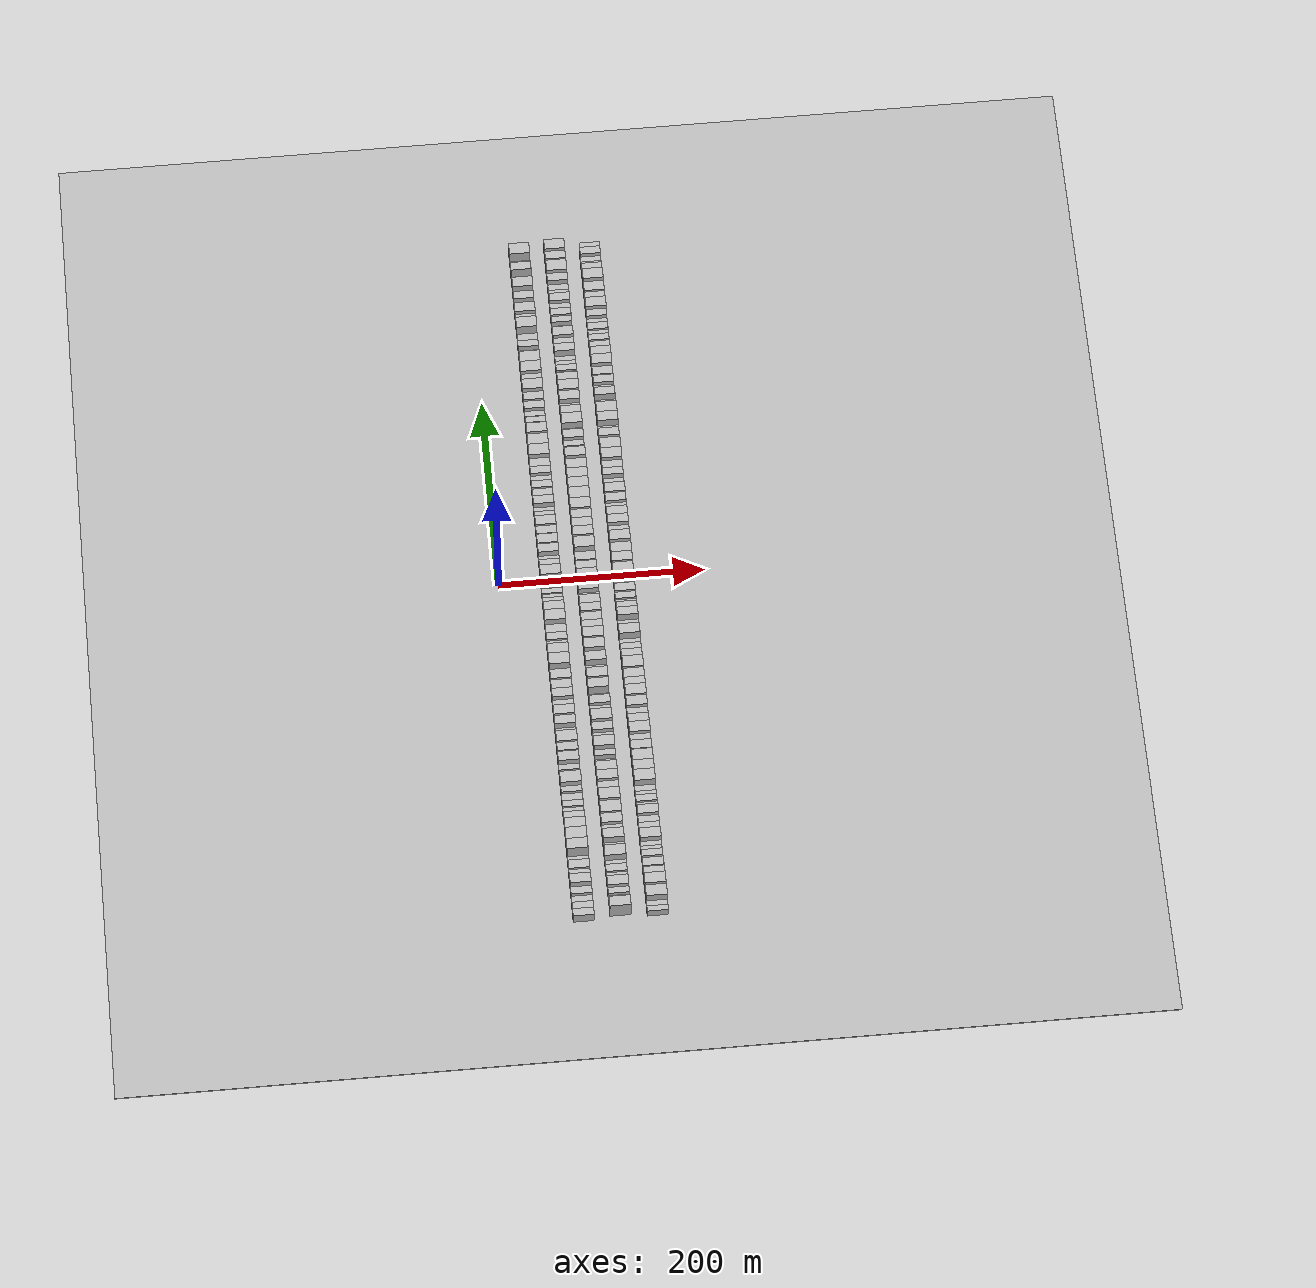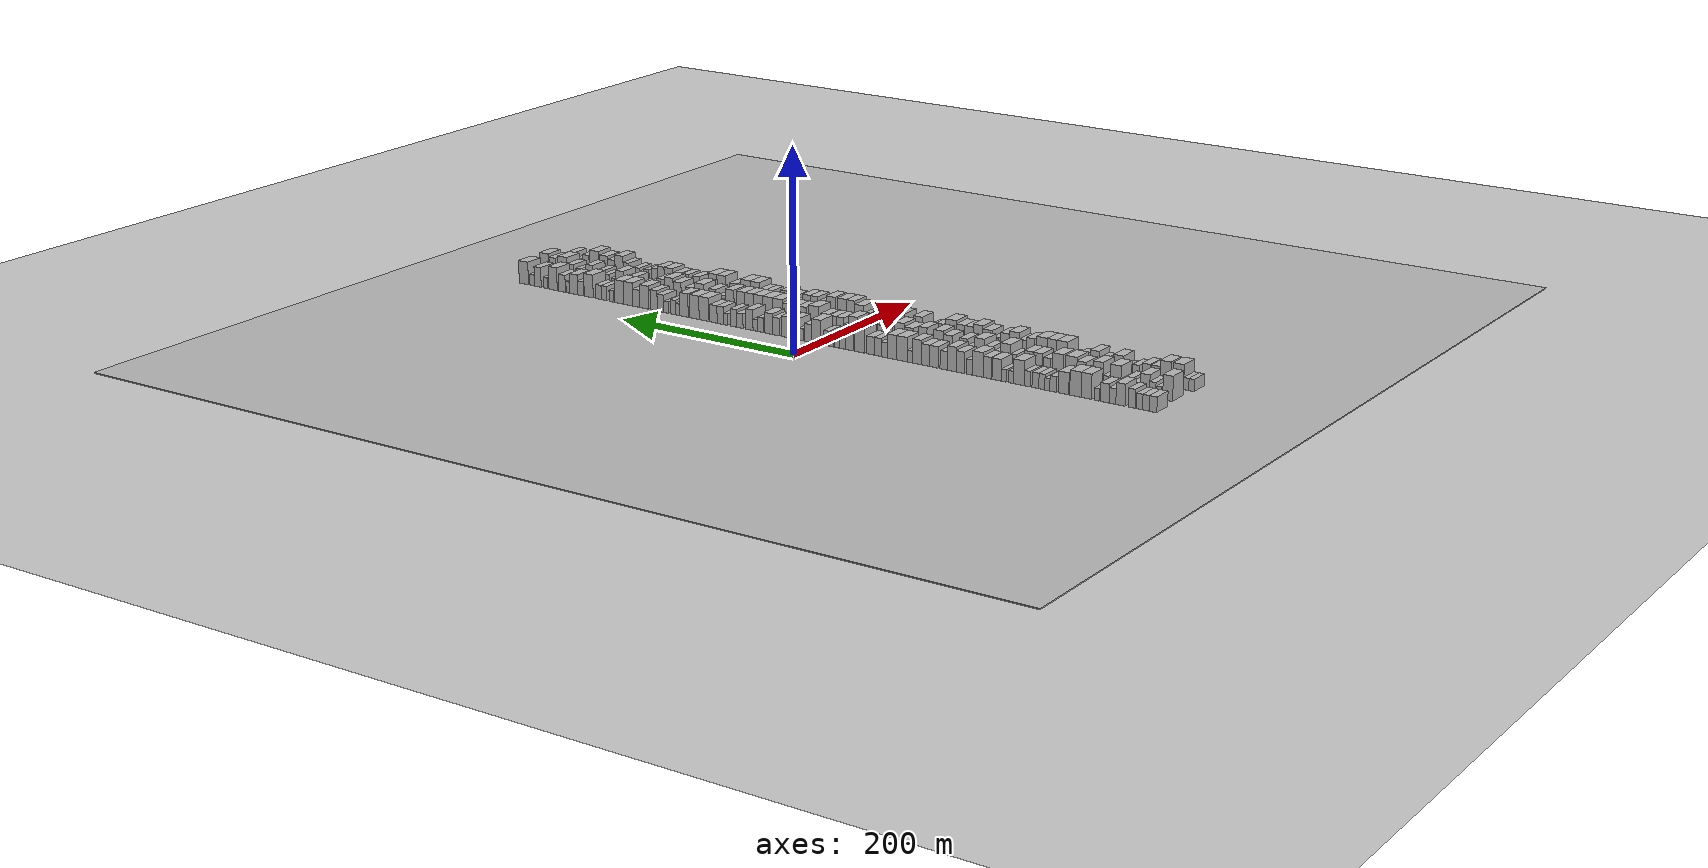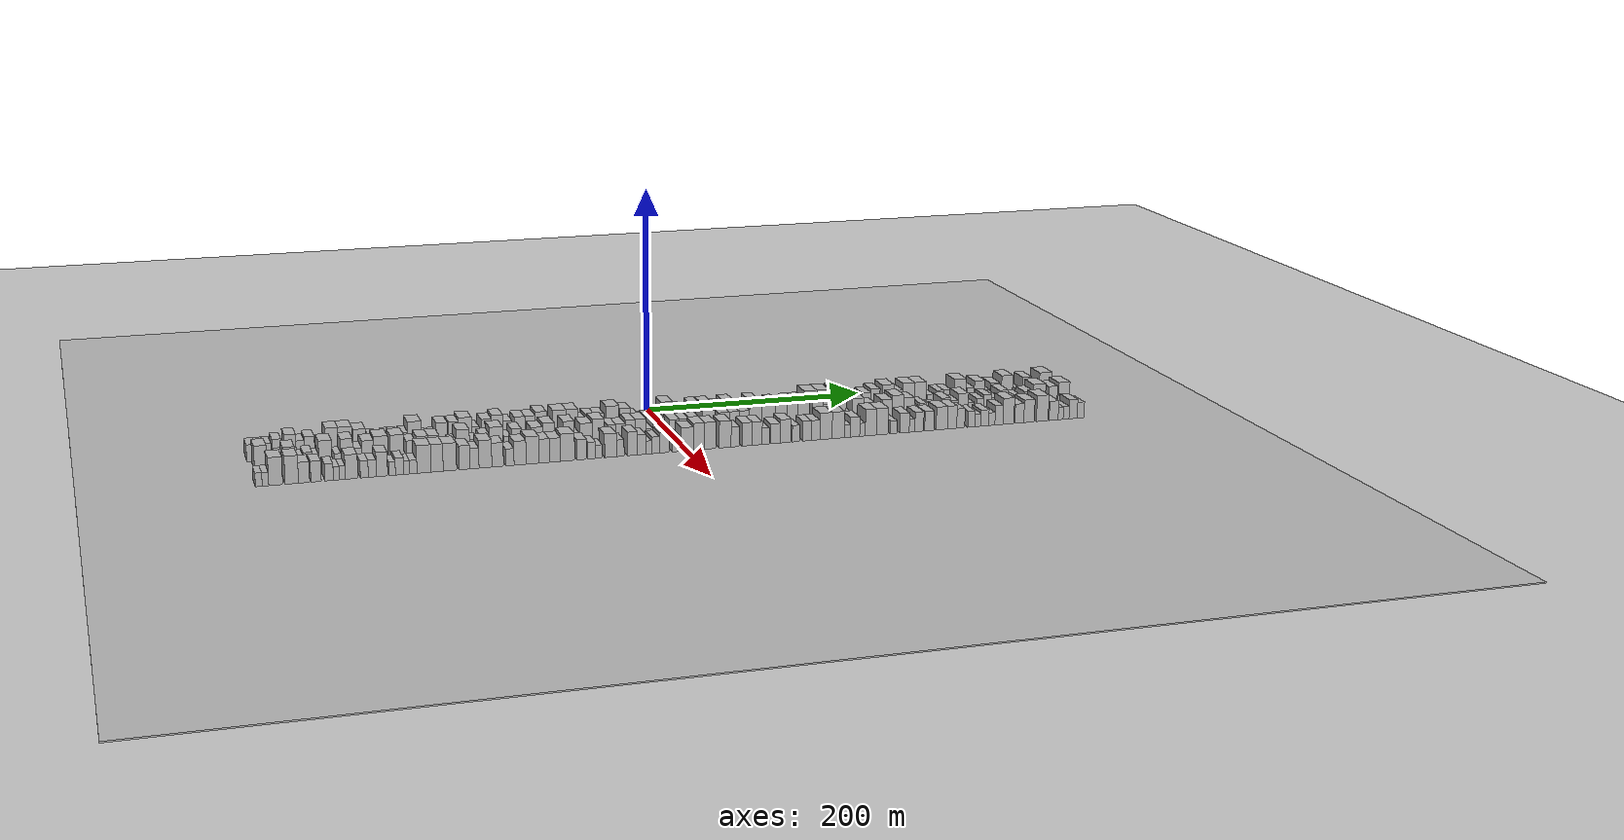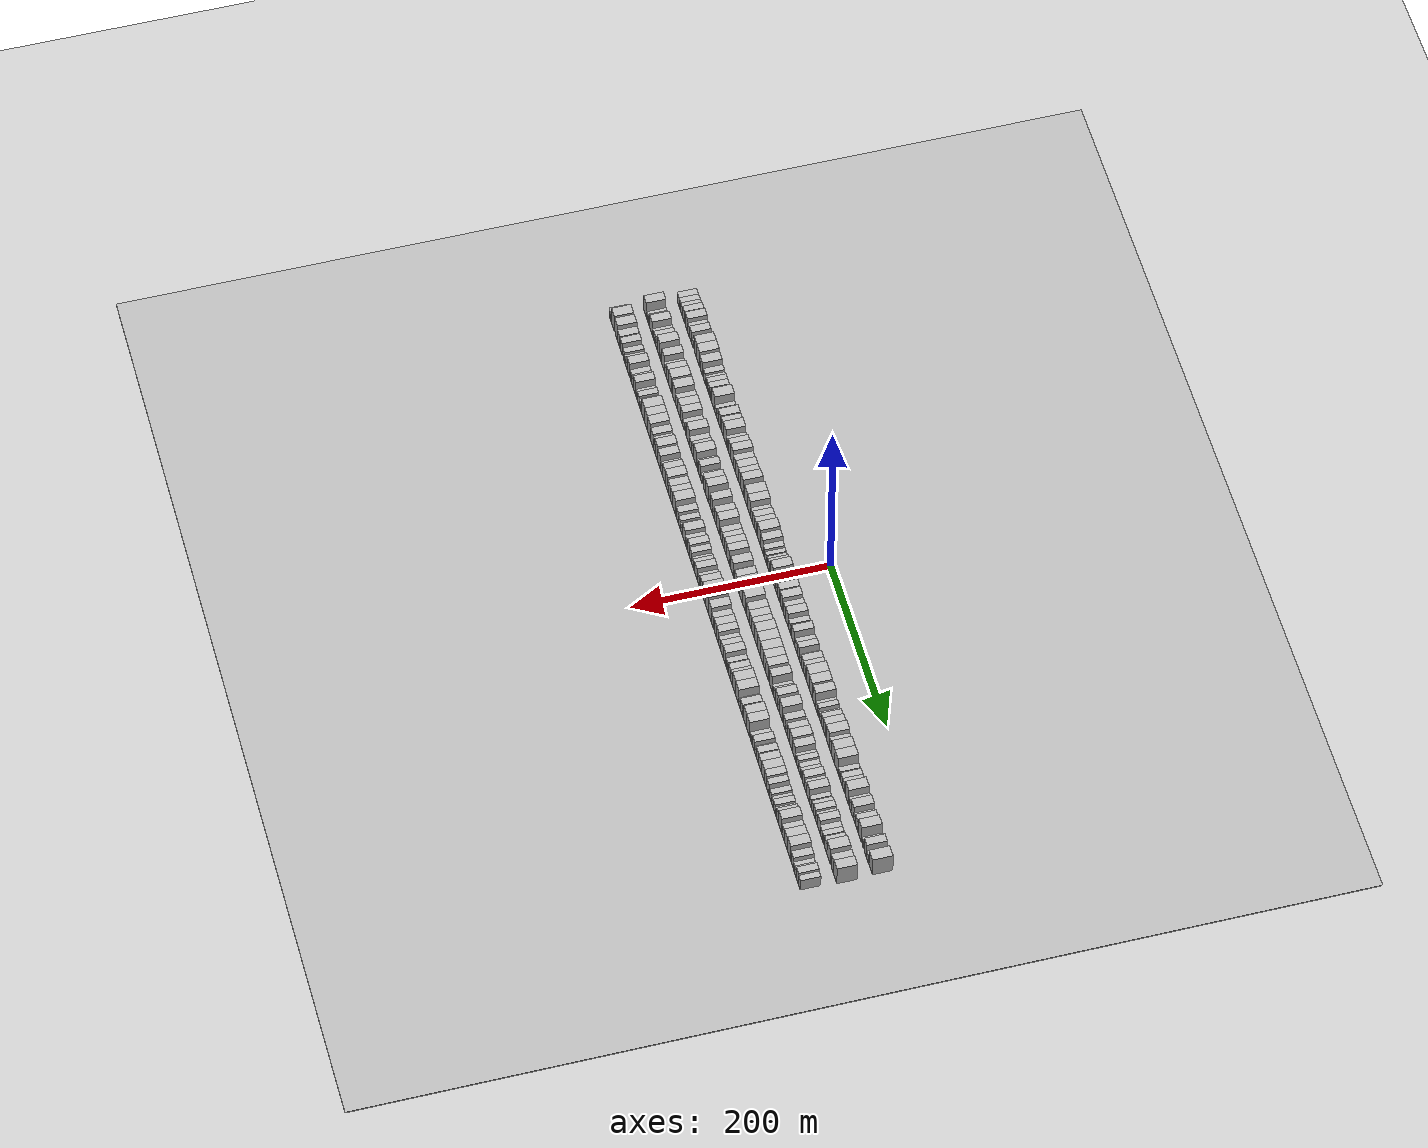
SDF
<?xml version="1.0" encoding="utf-8"?>

<sdf version="1.6">

   <world name="default">

      <gui fullscreen="0">

         <camera name="user_camera">

            <pose>-15 0 4.57585 0 0 0</pose>

            <view_controller>orbit</view_controller>

         </camera>

      </gui>

      <scene>

         <sky>

           <clouds>

             <speed>12</speed>

           </clouds>

         </sky>

         <ambient>0.4 0.4 0.4 1</ambient>

         <background>0.7 0.7 0.7 1</background>

         <shadows>1</shadows>

      </scene>

      <gravity>0 0 -9.8066</gravity>

      <magnetic_field>6e-06 2.3e-05 -4.2e-05</magnetic_field>

      <physics default="0" name="default_physics" type="ode">

         <ode>

            <solver>

               <type>quick</type>

               <iters>10</iters>

               <sor>1.0</sor>

               <use_dynamic_moi_rescaling>0</use_dynamic_moi_rescaling>

            </solver>

            <constraints>

               <cfm>0</cfm>

               <erp>0.2</erp>

               <contact_max_correcting_vel>100</contact_max_correcting_vel>

               <contact_surface_layer>0.001</contact_surface_layer>

            </constraints>

         </ode>

         <max_step_size>0.004</max_step_size>

         <real_time_factor>1</real_time_factor>

         <real_time_update_rate>250</real_time_update_rate>

      </physics>

      <light name="sun" type="directional">

         <cast_shadows>1</cast_shadows>

         <pose>0 0 10 0 0 0</pose>

         <diffuse>0.8 0.8 0.8 1</diffuse>

         <specular>0.2 0.2 0.2 1</specular>

         <attenuation>

            <range>1000</range>

            <constant>0.9</constant>

            <linear>0.01</linear>

            <quadratic>0.001</quadratic>

         </attenuation>

         <direction>-0.5 0.1 -0.9</direction>

      </light>

      <include>

         <name>ground_plane_1</name>

         <uri>model://HANNAS_ground_plane</uri>

         <pose>0 0 0  0 0 0</pose>

      </include>

      <include>

         <name>ground_plane_2</name>

         <uri>model://HANNAS_ground_plane</uri>

         <pose>100 0 0  0 0 0</pose>

      </include>

      <model name="building_1">

         <static>1</static>

         <pose frame="">50.0000 -356.2770 0 0.000000 0.000000 0.000000</pose>

         <link name="link">

            <pose frame="">0 0 7.50 0 0 0</pose>

            <collision name="collision">

               <geometry>

                  <box>

                     <size>20.0000 7.4460 15.0000</size>

                  </box>

               </geometry>

               <max_contacts>10</max_contacts>

               <surface>

                  <contact>

                     <ode/>

                  </contact>

                  <bounce/>

                  <friction>

                     <torsional>

                        <ode/>

                     </torsional>

                     <ode/>

                  </friction>

               </surface>

            </collision>

            <visual name="visual">

               <cast_shadows>0</cast_shadows>

               <geometry>

                  <box>

                     <size>20.0000 7.4460 15.0000</size>

                  </box>

               </geometry>

               <material>

                  <script>

                     <uri>model://HANNAS_wall/materials/scripts</uri>

                     <uri>model://HANNAS_wall/materials/textures</uri>

                     <name>vrc/HANNAS_wall</name>

                  </script>

               </material>

            </visual>

            <self_collide>0</self_collide>

            <enable_wind>0</enable_wind>

            <kinematic>0</kinematic>

         </link>

      </model>

      <model name="building_2">

         <static>1</static>

         <pose frame="">50.0000 -349.2100 0 0.000000 0.000000 0.000000</pose>

         <link name="link">

            <pose frame="">0 0 7.50 0 0 0</pose>

            <collision name="collision">

               <geometry>

                  <box>

                     <size>20.0000 6.6880 15.0000</size>

                  </box>

               </geometry>

               <max_contacts>10</max_contacts>

               <surface>

                  <contact>

                     <ode/>

                  </contact>

                  <bounce/>

                  <friction>

                     <torsional>

                        <ode/>

                     </torsional>

                     <ode/>

                  </friction>

               </surface>

            </collision>

            <visual name="visual">

               <cast_shadows>0</cast_shadows>

               <geometry>

                  <box>

                     <size>20.0000 6.6880 15.0000</size>

                  </box>

               </geometry>

               <material>

                  <script>

                     <uri>model://HANNAS_wall/materials/scripts</uri>

                     <uri>model://HANNAS_wall/materials/textures</uri>

                     <name>vrc/HANNAS_wall</name>

                  </script>

               </material>

            </visual>

            <self_collide>0</self_collide>

            <enable_wind>0</enable_wind>

            <kinematic>0</kinematic>

         </link>

      </model>

      <model name="building_3">

         <static>1</static>

         <pose frame="">50.0000 -342.8018 0 0.000000 0.000000 0.000000</pose>

         <link name="link">

            <pose frame="">0 0 7.50 0 0 0</pose>

            <collision name="collision">

               <geometry>

                  <box>

                     <size>20.0000 6.1283 15.0000</size>

                  </box>

               </geometry>

               <max_contacts>10</max_contacts>

               <surface>

                  <contact>

                     <ode/>

                  </contact>

                  <bounce/>

                  <friction>

                     <torsional>

                        <ode/>

                     </torsional>

                     <ode/>

                  </friction>

               </surface>

            </collision>

            <visual name="visual">

               <cast_shadows>0</cast_shadows>

               <geometry>

                  <box>

                     <size>20.0000 6.1283 15.0000</size>

                  </box>

               </geometry>

               <material>

                  <script>

                     <uri>model://HANNAS_wall/materials/scripts</uri>

                     <uri>model://HANNAS_wall/materials/textures</uri>

                     <name>vrc/HANNAS_wall</name>

                  </script>

               </material>

            </visual>

            <self_collide>0</self_collide>

            <enable_wind>0</enable_wind>

            <kinematic>0</kinematic>

         </link>

      </model>

      <model name="building_4">

         <static>1</static>

         <pose frame="">50.0000 -335.0817 0 0.000000 0.000000 0.000000</pose>

         <link name="link">

            <pose frame="">0 0 9.00 0 0 0</pose>

            <collision name="collision">

               <geometry>

                  <box>

                     <size>20.0000 7.3120 18.0000</size>

                  </box>

               </geometry>

               <max_contacts>10</max_contacts>

               <surface>

                  <contact>

                     <ode/>

                  </contact>

                  <bounce/>

                  <friction>

                     <torsional>

                        <ode/>

                     </torsional>

                     <ode/>

                  </friction>

               </surface>

            </collision>

            <visual name="visual">

               <cast_shadows>0</cast_shadows>

               <geometry>

                  <box>

                     <size>20.0000 7.3120 18.0000</size>

                  </box>

               </geometry>

               <material>

                  <script>

                     <uri>model://HANNAS_wall/materials/scripts</uri>

                     <uri>model://HANNAS_wall/materials/textures</uri>

                     <name>vrc/HANNAS_wall</name>

                  </script>

               </material>

            </visual>

            <self_collide>0</self_collide>

            <enable_wind>0</enable_wind>

            <kinematic>0</kinematic>

         </link>

      </model>

      <model name="building_5">

         <static>1</static>

         <pose frame="">50.0000 -323.7454 0 0.000000 0.000000 0.000000</pose>

         <link name="link">

            <pose frame="">0 0 10.50 0 0 0</pose>

            <collision name="collision">

               <geometry>

                  <box>

                     <size>20.0000 9.3605 21.0000</size>

                  </box>

               </geometry>

               <max_contacts>10</max_contacts>

               <surface>

                  <contact>

                     <ode/>

                  </contact>

                  <bounce/>

                  <friction>

                     <torsional>

                        <ode/>

                     </torsional>

                     <ode/>

                  </friction>

               </surface>

            </collision>

            <visual name="visual">

               <cast_shadows>0</cast_shadows>

               <geometry>

                  <box>

                     <size>20.0000 9.3605 21.0000</size>

                  </box>

               </geometry>

               <material>

                  <script>

                     <uri>model://HANNAS_wall/materials/scripts</uri>

                     <uri>model://HANNAS_wall/materials/textures</uri>

                     <name>vrc/HANNAS_wall</name>

                  </script>

               </material>

            </visual>

            <self_collide>0</self_collide>

            <enable_wind>0</enable_wind>

            <kinematic>0</kinematic>

         </link>

      </model>

      <model name="building_6">

         <static>1</static>

         <pose frame="">50.0000 -315.6376 0 0.000000 0.000000 0.000000</pose>

         <link name="link">

            <pose frame="">0 0 7.50 0 0 0</pose>

            <collision name="collision">

               <geometry>

                  <box>

                     <size>20.0000 6.8551 15.0000</size>

                  </box>

               </geometry>

               <max_contacts>10</max_contacts>

               <surface>

                  <contact>

                     <ode/>

                  </contact>

                  <bounce/>

                  <friction>

                     <torsional>

                        <ode/>

                     </torsional>

                     <ode/>

                  </friction>

               </surface>

            </collision>

            <visual name="visual">

               <cast_shadows>0</cast_shadows>

               <geometry>

                  <box>

                     <size>20.0000 6.8551 15.0000</size>

                  </box>

               </geometry>

               <material>

                  <script>

                     <uri>model://HANNAS_wall/materials/scripts</uri>

                     <uri>model://HANNAS_wall/materials/textures</uri>

                     <name>vrc/HANNAS_wall</name>

                  </script>

               </material>

            </visual>

            <self_collide>0</self_collide>

            <enable_wind>0</enable_wind>

            <kinematic>0</kinematic>

         </link>

      </model>

      <model name="building_7">

         <static>1</static>

         <pose frame="">50.0000 -307.8931 0 0.000000 0.000000 0.000000</pose>

         <link name="link">

            <pose frame="">0 0 9.00 0 0 0</pose>

            <collision name="collision">

               <geometry>

                  <box>

                     <size>20.0000 8.6339 18.0000</size>

                  </box>

               </geometry>

               <max_contacts>10</max_contacts>

               <surface>

                  <contact>

                     <ode/>

                  </contact>

                  <bounce/>

                  <friction>

                     <torsional>

                        <ode/>

                     </torsional>

                     <ode/>

                  </friction>

               </surface>

            </collision>

            <visual name="visual">

               <cast_shadows>0</cast_shadows>

               <geometry>

                  <box>

                     <size>20.0000 8.6339 18.0000</size>

                  </box>

               </geometry>

               <material>

                  <script>

                     <uri>model://HANNAS_wall/materials/scripts</uri>

                     <uri>model://HANNAS_wall/materials/textures</uri>

                     <name>vrc/HANNAS_wall</name>

                  </script>

               </material>

            </visual>

            <self_collide>0</self_collide>

            <enable_wind>0</enable_wind>

            <kinematic>0</kinematic>

         </link>

      </model>

      <model name="building_8">

         <static>1</static>

         <pose frame="">50.0000 -299.9925 0 0.000000 0.000000 0.000000</pose>

         <link name="link">

            <pose frame="">0 0 6.00 0 0 0</pose>

            <collision name="collision">

               <geometry>

                  <box>

                     <size>20.0000 5.1674 12.0000</size>

                  </box>

               </geometry>

               <max_contacts>10</max_contacts>

               <surface>

                  <contact>

                     <ode/>

                  </contact>

                  <bounce/>

                  <friction>

                     <torsional>

                        <ode/>

                     </torsional>

                     <ode/>

                  </friction>

               </surface>

            </collision>

            <visual name="visual">

               <cast_shadows>0</cast_shadows>

               <geometry>

                  <box>

                     <size>20.0000 5.1674 12.0000</size>

                  </box>

               </geometry>

               <material>

                  <script>

                     <uri>model://HANNAS_wall/materials/scripts</uri>

                     <uri>model://HANNAS_wall/materials/textures</uri>

                     <name>vrc/HANNAS_wall</name>

                  </script>

               </material>

            </visual>

            <self_collide>0</self_collide>

            <enable_wind>0</enable_wind>

            <kinematic>0</kinematic>

         </link>

      </model>

      <model name="building_9">

         <static>1</static>

         <pose frame="">50.0000 -289.0979 0 0.000000 0.000000 0.000000</pose>

         <link name="link">

            <pose frame="">0 0 12.00 0 0 0</pose>

            <collision name="collision">

               <geometry>

                  <box>

                     <size>20.0000 10.6217 24.0000</size>

                  </box>

               </geometry>

               <max_contacts>10</max_contacts>

               <surface>

                  <contact>

                     <ode/>

                  </contact>

                  <bounce/>

                  <friction>

                     <torsional>

                        <ode/>

                     </torsional>

                     <ode/>

                  </friction>

               </surface>

            </collision>

            <visual name="visual">

               <cast_shadows>0</cast_shadows>

               <geometry>

                  <box>

                     <size>20.0000 10.6217 24.0000</size>

                  </box>

               </geometry>

               <material>

                  <script>

                     <uri>model://HANNAS_wall/materials/scripts</uri>

                     <uri>model://HANNAS_wall/materials/textures</uri>

                     <name>vrc/HANNAS_wall</name>

                  </script>

               </material>

            </visual>

            <self_collide>0</self_collide>

            <enable_wind>0</enable_wind>

            <kinematic>0</kinematic>

         </link>

      </model>

      <model name="building_10">

         <static>1</static>

         <pose frame="">50.0000 -278.0000 0 0.000000 0.000000 0.000000</pose>

         <link name="link">

            <pose frame="">0 0 12.00 0 0 0</pose>

            <collision name="collision">

               <geometry>

                  <box>

                     <size>20.0000 11.5742 24.0000</size>

                  </box>

               </geometry>

               <max_contacts>10</max_contacts>

               <surface>

                  <contact>

                     <ode/>

                  </contact>

                  <bounce/>

                  <friction>

                     <torsional>

                        <ode/>

                     </torsional>

                     <ode/>

                  </friction>

               </surface>

            </collision>

            <visual name="visual">

               <cast_shadows>0</cast_shadows>

               <geometry>

                  <box>

                     <size>20.0000 11.5742 24.0000</size>

                  </box>

               </geometry>

               <material>

                  <script>

                     <uri>model://HANNAS_wall/materials/scripts</uri>

                     <uri>model://HANNAS_wall/materials/textures</uri>

                     <name>vrc/HANNAS_wall</name>

                  </script>

               </material>

            </visual>

            <self_collide>0</self_collide>

            <enable_wind>0</enable_wind>

            <kinematic>0</kinematic>

         </link>

      </model>

      <model name="building_11">

         <static>1</static>

         <pose frame="">50.0000 -265.9669 0 0.000000 0.000000 0.000000</pose>

         <link name="link">

            <pose frame="">0 0 10.50 0 0 0</pose>

            <collision name="collision">

               <geometry>

                  <box>

                     <size>20.0000 10.4920 21.0000</size>

                  </box>

               </geometry>

               <max_contacts>10</max_contacts>

               <surface>

                  <contact>

                     <ode/>

                  </contact>

                  <bounce/>

                  <friction>

                     <torsional>

                        <ode/>

                     </torsional>

                     <ode/>

                  </friction>

               </surface>

            </collision>

            <visual name="visual">

               <cast_shadows>0</cast_shadows>

               <geometry>

                  <box>

                     <size>20.0000 10.4920 21.0000</size>

                  </box>

               </geometry>

               <material>

                  <script>

                     <uri>model://HANNAS_wall/materials/scripts</uri>

                     <uri>model://HANNAS_wall/materials/textures</uri>

                     <name>vrc/HANNAS_wall</name>

                  </script>

               </material>

            </visual>

            <self_collide>0</self_collide>

            <enable_wind>0</enable_wind>

            <kinematic>0</kinematic>

         </link>

      </model>

      <model name="building_12">

         <static>1</static>

         <pose frame="">50.0000 -255.2145 0 0.000000 0.000000 0.000000</pose>

         <link name="link">

            <pose frame="">0 0 7.50 0 0 0</pose>

            <collision name="collision">

               <geometry>

                  <box>

                     <size>20.0000 7.0128 15.0000</size>

                  </box>

               </geometry>

               <max_contacts>10</max_contacts>

               <surface>

                  <contact>

                     <ode/>

                  </contact>

                  <bounce/>

                  <friction>

                     <torsional>

                        <ode/>

                     </torsional>

                     <ode/>

                  </friction>

               </surface>

            </collision>

            <visual name="visual">

               <cast_shadows>0</cast_shadows>

               <geometry>

                  <box>

                     <size>20.0000 7.0128 15.0000</size>

                  </box>

               </geometry>

               <material>

                  <script>

                     <uri>model://HANNAS_wall/materials/scripts</uri>

                     <uri>model://HANNAS_wall/materials/textures</uri>

                     <name>vrc/HANNAS_wall</name>

                  </script>

               </material>

            </visual>

            <self_collide>0</self_collide>

            <enable_wind>0</enable_wind>

            <kinematic>0</kinematic>

         </link>

      </model>

      <model name="building_13">

         <static>1</static>

         <pose frame="">50.0000 -249.1054 0 0.000000 0.000000 0.000000</pose>

         <link name="link">

            <pose frame="">0 0 6.00 0 0 0</pose>

            <collision name="collision">

               <geometry>

                  <box>

                     <size>20.0000 5.2054 12.0000</size>

                  </box>

               </geometry>

               <max_contacts>10</max_contacts>

               <surface>

                  <contact>

                     <ode/>

                  </contact>

                  <bounce/>

                  <friction>

                     <torsional>

                        <ode/>

                     </torsional>

                     <ode/>

                  </friction>

               </surface>

            </collision>

            <visual name="visual">

               <cast_shadows>0</cast_shadows>

               <geometry>

                  <box>

                     <size>20.0000 5.2054 12.0000</size>

                  </box>

               </geometry>

               <material>

                  <script>

                     <uri>model://HANNAS_wall/materials/scripts</uri>

                     <uri>model://HANNAS_wall/materials/textures</uri>

                     <name>vrc/HANNAS_wall</name>

                  </script>

               </material>

            </visual>

            <self_collide>0</self_collide>

            <enable_wind>0</enable_wind>

            <kinematic>0</kinematic>

         </link>

      </model>

      <model name="building_14">

         <static>1</static>

         <pose frame="">50.0000 -243.4042 0 0.000000 0.000000 0.000000</pose>

         <link name="link">

            <pose frame="">0 0 7.50 0 0 0</pose>

            <collision name="collision">

               <geometry>

                  <box>

                     <size>20.0000 6.1970 15.0000</size>

                  </box>

               </geometry>

               <max_contacts>10</max_contacts>

               <surface>

                  <contact>

                     <ode/>

                  </contact>

                  <bounce/>

                  <friction>

                     <torsional>

                        <ode/>

                     </torsional>

                     <ode/>

                  </friction>

               </surface>

            </collision>

            <visual name="visual">

               <cast_shadows>0</cast_shadows>

               <geometry>

                  <box>

                     <size>20.0000 6.1970 15.0000</size>

                  </box>

               </geometry>

               <material>

                  <script>

                     <uri>model://HANNAS_wall/materials/scripts</uri>

                     <uri>model://HANNAS_wall/materials/textures</uri>

                     <name>vrc/HANNAS_wall</name>

                  </script>

               </material>

            </visual>

            <self_collide>0</self_collide>

            <enable_wind>0</enable_wind>

            <kinematic>0</kinematic>

         </link>

      </model>

      <model name="building_15">

         <static>1</static>

         <pose frame="">50.0000 -236.7528 0 0.000000 0.000000 0.000000</pose>

         <link name="link">

            <pose frame="">0 0 7.50 0 0 0</pose>

            <collision name="collision">

               <geometry>

                  <box>

                     <size>20.0000 7.1060 15.0000</size>

                  </box>

               </geometry>

               <max_contacts>10</max_contacts>

               <surface>

                  <contact>

                     <ode/>

                  </contact>

                  <bounce/>

                  <friction>

                     <torsional>

                        <ode/>

                     </torsional>

                     <ode/>

                  </friction>

               </surface>

            </collision>

            <visual name="visual">

               <cast_shadows>0</cast_shadows>

               <geometry>

                  <box>

                     <size>20.0000 7.1060 15.0000</size>

                  </box>

               </geometry>

               <material>

                  <script>

                     <uri>model://HANNAS_wall/materials/scripts</uri>

                     <uri>model://HANNAS_wall/materials/textures</uri>

                     <name>vrc/HANNAS_wall</name>

                  </script>

               </material>

            </visual>

            <self_collide>0</self_collide>

            <enable_wind>0</enable_wind>

            <kinematic>0</kinematic>

         </link>

      </model>

      <model name="building_16">

         <static>1</static>

         <pose frame="">50.0000 -228.1821 0 0.000000 0.000000 0.000000</pose>

         <link name="link">

            <pose frame="">0 0 7.50 0 0 0</pose>

            <collision name="collision">

               <geometry>

                  <box>

                     <size>20.0000 6.0353 15.0000</size>

                  </box>

               </geometry>

               <max_contacts>10</max_contacts>

               <surface>

                  <contact>

                     <ode/>

                  </contact>

                  <bounce/>

                  <friction>

                     <torsional>

                        <ode/>

                     </torsional>

                     <ode/>

                  </friction>

               </surface>

            </collision>

            <visual name="visual">

               <cast_shadows>0</cast_shadows>

               <geometry>

                  <box>

                     <size>20.0000 6.0353 15.0000</size>

                  </box>

               </geometry>

               <material>

                  <script>

                     <uri>model://HANNAS_wall/materials/scripts</uri>

                     <uri>model://HANNAS_wall/materials/textures</uri>

                     <name>vrc/HANNAS_wall</name>

                  </script>

               </material>

            </visual>

            <self_collide>0</self_collide>

            <enable_wind>0</enable_wind>

            <kinematic>0</kinematic>

         </link>

      </model>

      <model name="building_17">

         <static>1</static>

         <pose frame="">50.0000 -219.3494 0 0.000000 0.000000 0.000000</pose>

         <link name="link">

            <pose frame="">0 0 12.00 0 0 0</pose>

            <collision name="collision">

               <geometry>

                  <box>

                     <size>20.0000 11.6301 24.0000</size>

                  </box>

               </geometry>

               <max_contacts>10</max_contacts>

               <surface>

                  <contact>

                     <ode/>

                  </contact>

                  <bounce/>

                  <friction>

                     <torsional>

                        <ode/>

                     </torsional>

                     <ode/>

                  </friction>

               </surface>

            </collision>

            <visual name="visual">

               <cast_shadows>0</cast_shadows>

               <geometry>

                  <box>

                     <size>20.0000 11.6301 24.0000</size>

                  </box>

               </geometry>

               <material>

                  <script>

                     <uri>model://HANNAS_wall/materials/scripts</uri>

                     <uri>model://HANNAS_wall/materials/textures</uri>

                     <name>vrc/HANNAS_wall</name>

                  </script>

               </material>

            </visual>

            <self_collide>0</self_collide>

            <enable_wind>0</enable_wind>

            <kinematic>0</kinematic>

         </link>

      </model>

      <model name="building_18">

         <static>1</static>

         <pose frame="">50.0000 -211.0575 0 0.000000 0.000000 0.000000</pose>

         <link name="link">

            <pose frame="">0 0 6.00 0 0 0</pose>

            <collision name="collision">

               <geometry>

                  <box>

                     <size>20.0000 4.9537 12.0000</size>

                  </box>

               </geometry>

               <max_contacts>10</max_contacts>

               <surface>

                  <contact>

                     <ode/>

                  </contact>

                  <bounce/>

                  <friction>

                     <torsional>

                        <ode/>

                     </torsional>

                     <ode/>

                  </friction>

               </surface>

            </collision>

            <visual name="visual">

               <cast_shadows>0</cast_shadows>

               <geometry>

                  <box>

                     <size>20.0000 4.9537 12.0000</size>

                  </box>

               </geometry>

               <material>

                  <script>

                     <uri>model://HANNAS_wall/materials/scripts</uri>

                     <uri>model://HANNAS_wall/materials/textures</uri>

                     <name>vrc/HANNAS_wall</name>

                  </script>

               </material>

            </visual>

            <self_collide>0</self_collide>

            <enable_wind>0</enable_wind>

            <kinematic>0</kinematic>

         </link>

      </model>

      <model name="building_19">

         <static>1</static>

         <pose frame="">50.0000 -203.7017 0 0.000000 0.000000 0.000000</pose>

         <link name="link">

            <pose frame="">0 0 6.00 0 0 0</pose>

            <collision name="collision">

               <geometry>

                  <box>

                     <size>20.0000 5.7579 12.0000</size>

                  </box>

               </geometry>

               <max_contacts>10</max_contacts>

               <surface>

                  <contact>

                     <ode/>

                  </contact>

                  <bounce/>

                  <friction>

                     <torsional>

                        <ode/>

                     </torsional>

                     <ode/>

                  </friction>

               </surface>

            </collision>

            <visual name="visual">

               <cast_shadows>0</cast_shadows>

               <geometry>

                  <box>

                     <size>20.0000 5.7579 12.0000</size>

                  </box>

               </geometry>

               <material>

                  <script>

                     <uri>model://HANNAS_wall/materials/scripts</uri>

                     <uri>model://HANNAS_wall/materials/textures</uri>

                     <name>vrc/HANNAS_wall</name>

                  </script>

               </material>

            </visual>

            <self_collide>0</self_collide>

            <enable_wind>0</enable_wind>

            <kinematic>0</kinematic>

         </link>

      </model>

      <model name="building_20">

         <static>1</static>

         <pose frame="">50.0000 -195.9950 0 0.000000 0.000000 0.000000</pose>

         <link name="link">

            <pose frame="">0 0 10.50 0 0 0</pose>

            <collision name="collision">

               <geometry>

                  <box>

                     <size>20.0000 9.6555 21.0000</size>

                  </box>

               </geometry>

               <max_contacts>10</max_contacts>

               <surface>

                  <contact>

                     <ode/>

                  </contact>

                  <bounce/>

                  <friction>

                     <torsional>

                        <ode/>

                     </torsional>

                     <ode/>

                  </friction>

               </surface>

            </collision>

            <visual name="visual">

               <cast_shadows>0</cast_shadows>

               <geometry>

                  <box>

                     <size>20.0000 9.6555 21.0000</size>

                  </box>

               </geometry>

               <material>

                  <script>

                     <uri>model://HANNAS_wall/materials/scripts</uri>

                     <uri>model://HANNAS_wall/materials/textures</uri>

                     <name>vrc/HANNAS_wall</name>

                  </script>

               </material>

            </visual>

            <self_collide>0</self_collide>

            <enable_wind>0</enable_wind>

            <kinematic>0</kinematic>

         </link>

      </model>

      <model name="building_21">

         <static>1</static>

         <pose frame="">50.0000 -185.9400 0 0.000000 0.000000 0.000000</pose>

         <link name="link">

            <pose frame="">0 0 10.50 0 0 0</pose>

            <collision name="collision">

               <geometry>

                  <box>

                     <size>20.0000 8.4545 21.0000</size>

                  </box>

               </geometry>

               <max_contacts>10</max_contacts>

               <surface>

                  <contact>

                     <ode/>

                  </contact>

                  <bounce/>

                  <friction>

                     <torsional>

                        <ode/>

                     </torsional>

                     <ode/>

                  </friction>

               </surface>

            </collision>

            <visual name="visual">

               <cast_shadows>0</cast_shadows>

               <geometry>

                  <box>

                     <size>20.0000 8.4545 21.0000</size>

                  </box>

               </geometry>

               <material>

                  <script>

                     <uri>model://HANNAS_wall/materials/scripts</uri>

                     <uri>model://HANNAS_wall/materials/textures</uri>

                     <name>vrc/HANNAS_wall</name>

                  </script>

               </material>

            </visual>

            <self_collide>0</self_collide>

            <enable_wind>0</enable_wind>

            <kinematic>0</kinematic>

         </link>

      </model>

      <model name="building_22">

         <static>1</static>

         <pose frame="">50.0000 -176.1149 0 0.000000 0.000000 0.000000</pose>

         <link name="link">

            <pose frame="">0 0 12.00 0 0 0</pose>

            <collision name="collision">

               <geometry>

                  <box>

                     <size>20.0000 11.1957 24.0000</size>

                  </box>

               </geometry>

               <max_contacts>10</max_contacts>

               <surface>

                  <contact>

                     <ode/>

                  </contact>

                  <bounce/>

                  <friction>

                     <torsional>

                        <ode/>

                     </torsional>

                     <ode/>

                  </friction>

               </surface>

            </collision>

            <visual name="visual">

               <cast_shadows>0</cast_shadows>

               <geometry>

                  <box>

                     <size>20.0000 11.1957 24.0000</size>

                  </box>

               </geometry>

               <material>

                  <script>

                     <uri>model://HANNAS_wall/materials/scripts</uri>

                     <uri>model://HANNAS_wall/materials/textures</uri>

                     <name>vrc/HANNAS_wall</name>

                  </script>

               </material>

            </visual>

            <self_collide>0</self_collide>

            <enable_wind>0</enable_wind>

            <kinematic>0</kinematic>

         </link>

      </model>

      <model name="building_23">

         <static>1</static>

         <pose frame="">50.0000 -167.2799 0 0.000000 0.000000 0.000000</pose>

         <link name="link">

            <pose frame="">0 0 7.50 0 0 0</pose>

            <collision name="collision">

               <geometry>

                  <box>

                     <size>20.0000 6.4744 15.0000</size>

                  </box>

               </geometry>

               <max_contacts>10</max_contacts>

               <surface>

                  <contact>

                     <ode/>

                  </contact>

                  <bounce/>

                  <friction>

                     <torsional>

                        <ode/>

                     </torsional>

                     <ode/>

                  </friction>

               </surface>

            </collision>

            <visual name="visual">

               <cast_shadows>0</cast_shadows>

               <geometry>

                  <box>

                     <size>20.0000 6.4744 15.0000</size>

                  </box>

               </geometry>

               <material>

                  <script>

                     <uri>model://HANNAS_wall/materials/scripts</uri>

                     <uri>model://HANNAS_wall/materials/textures</uri>

                     <name>vrc/HANNAS_wall</name>

                  </script>

               </material>

            </visual>

            <self_collide>0</self_collide>

            <enable_wind>0</enable_wind>

            <kinematic>0</kinematic>

         </link>

      </model>

      <model name="building_24">

         <static>1</static>

         <pose frame="">50.0000 -157.5226 0 0.000000 0.000000 0.000000</pose>

         <link name="link">

            <pose frame="">0 0 10.50 0 0 0</pose>

            <collision name="collision">

               <geometry>

                  <box>

                     <size>20.0000 9.0403 21.0000</size>

                  </box>

               </geometry>

               <max_contacts>10</max_contacts>

               <surface>

                  <contact>

                     <ode/>

                  </contact>

                  <bounce/>

                  <friction>

                     <torsional>

                        <ode/>

                     </torsional>

                     <ode/>

                  </friction>

               </surface>

            </collision>

            <visual name="visual">

               <cast_shadows>0</cast_shadows>

               <geometry>

                  <box>

                     <size>20.0000 9.0403 21.0000</size>

                  </box>

               </geometry>

               <material>

                  <script>

                     <uri>model://HANNAS_wall/materials/scripts</uri>

                     <uri>model://HANNAS_wall/materials/textures</uri>

                     <name>vrc/HANNAS_wall</name>

                  </script>

               </material>

            </visual>

            <self_collide>0</self_collide>

            <enable_wind>0</enable_wind>

            <kinematic>0</kinematic>

         </link>

      </model>

      <model name="building_25">

         <static>1</static>

         <pose frame="">50.0000 -148.1987 0 0.000000 0.000000 0.000000</pose>

         <link name="link">

            <pose frame="">0 0 12.00 0 0 0</pose>

            <collision name="collision">

               <geometry>

                  <box>

                     <size>20.0000 9.6075 24.0000</size>

                  </box>

               </geometry>

               <max_contacts>10</max_contacts>

               <surface>

                  <contact>

                     <ode/>

                  </contact>

                  <bounce/>

                  <friction>

                     <torsional>

                        <ode/>

                     </torsional>

                     <ode/>

                  </friction>

               </surface>

            </collision>

            <visual name="visual">

               <cast_shadows>0</cast_shadows>

               <geometry>

                  <box>

                     <size>20.0000 9.6075 24.0000</size>

                  </box>

               </geometry>

               <material>

                  <script>

                     <uri>model://HANNAS_wall/materials/scripts</uri>

                     <uri>model://HANNAS_wall/materials/textures</uri>

                     <name>vrc/HANNAS_wall</name>

                  </script>

               </material>

            </visual>

            <self_collide>0</self_collide>

            <enable_wind>0</enable_wind>

            <kinematic>0</kinematic>

         </link>

      </model>

      <model name="building_26">

         <static>1</static>

         <pose frame="">50.0000 -139.4160 0 0.000000 0.000000 0.000000</pose>

         <link name="link">

            <pose frame="">0 0 9.00 0 0 0</pose>

            <collision name="collision">

               <geometry>

                  <box>

                     <size>20.0000 7.9579 18.0000</size>

                  </box>

               </geometry>

               <max_contacts>10</max_contacts>

               <surface>

                  <contact>

                     <ode/>

                  </contact>

                  <bounce/>

                  <friction>

                     <torsional>

                        <ode/>

                     </torsional>

                     <ode/>

                  </friction>

               </surface>

            </collision>

            <visual name="visual">

               <cast_shadows>0</cast_shadows>

               <geometry>

                  <box>

                     <size>20.0000 7.9579 18.0000</size>

                  </box>

               </geometry>

               <material>

                  <script>

                     <uri>model://HANNAS_wall/materials/scripts</uri>

                     <uri>model://HANNAS_wall/materials/textures</uri>

                     <name>vrc/HANNAS_wall</name>

                  </script>

               </material>

            </visual>

            <self_collide>0</self_collide>

            <enable_wind>0</enable_wind>

            <kinematic>0</kinematic>

         </link>

      </model>

      <model name="building_27">

         <static>1</static>

         <pose frame="">50.0000 -128.8239 0 0.000000 0.000000 0.000000</pose>

         <link name="link">

            <pose frame="">0 0 10.50 0 0 0</pose>

            <collision name="collision">

               <geometry>

                  <box>

                     <size>20.0000 9.2261 21.0000</size>

                  </box>

               </geometry>

               <max_contacts>10</max_contacts>

               <surface>

                  <contact>

                     <ode/>

                  </contact>

                  <bounce/>

                  <friction>

                     <torsional>

                        <ode/>

                     </torsional>

                     <ode/>

                  </friction>

               </surface>

            </collision>

            <visual name="visual">

               <cast_shadows>0</cast_shadows>

               <geometry>

                  <box>

                     <size>20.0000 9.2261 21.0000</size>

                  </box>

               </geometry>

               <material>

                  <script>

                     <uri>model://HANNAS_wall/materials/scripts</uri>

                     <uri>model://HANNAS_wall/materials/textures</uri>

                     <name>vrc/HANNAS_wall</name>

                  </script>

               </material>

            </visual>

            <self_collide>0</self_collide>

            <enable_wind>0</enable_wind>

            <kinematic>0</kinematic>

         </link>

      </model>

      <model name="building_28">

         <static>1</static>

         <pose frame="">50.0000 -119.6874 0 0.000000 0.000000 0.000000</pose>

         <link name="link">

            <pose frame="">0 0 10.50 0 0 0</pose>

            <collision name="collision">

               <geometry>

                  <box>

                     <size>20.0000 9.0469 21.0000</size>

                  </box>

               </geometry>

               <max_contacts>10</max_contacts>

               <surface>

                  <contact>

                     <ode/>

                  </contact>

                  <bounce/>

                  <friction>

                     <torsional>

                        <ode/>

                     </torsional>

                     <ode/>

                  </friction>

               </surface>

            </collision>

            <visual name="visual">

               <cast_shadows>0</cast_shadows>

               <geometry>

                  <box>

                     <size>20.0000 9.0469 21.0000</size>

                  </box>

               </geometry>

               <material>

                  <script>

                     <uri>model://HANNAS_wall/materials/scripts</uri>

                     <uri>model://HANNAS_wall/materials/textures</uri>

                     <name>vrc/HANNAS_wall</name>

                  </script>

               </material>

            </visual>

            <self_collide>0</self_collide>

            <enable_wind>0</enable_wind>

            <kinematic>0</kinematic>

         </link>

      </model>

      <model name="building_29">

         <static>1</static>

         <pose frame="">50.0000 -110.2799 0 0.000000 0.000000 0.000000</pose>

         <link name="link">

            <pose frame="">0 0 12.00 0 0 0</pose>

            <collision name="collision">

               <geometry>

                  <box>

                     <size>20.0000 9.7681 24.0000</size>

                  </box>

               </geometry>

               <max_contacts>10</max_contacts>

               <surface>

                  <contact>

                     <ode/>

                  </contact>

                  <bounce/>

                  <friction>

                     <torsional>

                        <ode/>

                     </torsional>

                     <ode/>

                  </friction>

               </surface>

            </collision>

            <visual name="visual">

               <cast_shadows>0</cast_shadows>

               <geometry>

                  <box>

                     <size>20.0000 9.7681 24.0000</size>

                  </box>

               </geometry>

               <material>

                  <script>

                     <uri>model://HANNAS_wall/materials/scripts</uri>

                     <uri>model://HANNAS_wall/materials/textures</uri>

                     <name>vrc/HANNAS_wall</name>

                  </script>

               </material>

            </visual>

            <self_collide>0</self_collide>

            <enable_wind>0</enable_wind>

            <kinematic>0</kinematic>

         </link>

      </model>

      <model name="building_30">

         <static>1</static>

         <pose frame="">50.0000 -102.4965 0 0.000000 0.000000 0.000000</pose>

         <link name="link">

            <pose frame="">0 0 6.00 0 0 0</pose>

            <collision name="collision">

               <geometry>

                  <box>

                     <size>20.0000 5.7986 12.0000</size>

                  </box>

               </geometry>

               <max_contacts>10</max_contacts>

               <surface>

                  <contact>

                     <ode/>

                  </contact>

                  <bounce/>

                  <friction>

                     <torsional>

                        <ode/>

                     </torsional>

                     <ode/>

                  </friction>

               </surface>

            </collision>

            <visual name="visual">

               <cast_shadows>0</cast_shadows>

               <geometry>

                  <box>

                     <size>20.0000 5.7986 12.0000</size>

                  </box>

               </geometry>

               <material>

                  <script>

                     <uri>model://HANNAS_wall/materials/scripts</uri>

                     <uri>model://HANNAS_wall/materials/textures</uri>

                     <name>vrc/HANNAS_wall</name>

                  </script>

               </material>

            </visual>

            <self_collide>0</self_collide>

            <enable_wind>0</enable_wind>

            <kinematic>0</kinematic>

         </link>

      </model>

      <model name="building_31">

         <static>1</static>

         <pose frame="">50.0000 -93.7055 0 0.000000 0.000000 0.000000</pose>

         <link name="link">

            <pose frame="">0 0 12.00 0 0 0</pose>

            <collision name="collision">

               <geometry>

                  <box>

                     <size>20.0000 11.7835 24.0000</size>

                  </box>

               </geometry>

               <max_contacts>10</max_contacts>

               <surface>

                  <contact>

                     <ode/>

                  </contact>

                  <bounce/>

                  <friction>

                     <torsional>

                        <ode/>

                     </torsional>

                     <ode/>

                  </friction>

               </surface>

            </collision>

            <visual name="visual">

               <cast_shadows>0</cast_shadows>

               <geometry>

                  <box>

                     <size>20.0000 11.7835 24.0000</size>

                  </box>

               </geometry>

               <material>

                  <script>

                     <uri>model://HANNAS_wall/materials/scripts</uri>

                     <uri>model://HANNAS_wall/materials/textures</uri>

                     <name>vrc/HANNAS_wall</name>

                  </script>

               </material>

            </visual>

            <self_collide>0</self_collide>

            <enable_wind>0</enable_wind>

            <kinematic>0</kinematic>

         </link>

      </model>

      <model name="building_32">

         <static>1</static>

         <pose frame="">50.0000 -82.7374 0 0.000000 0.000000 0.000000</pose>

         <link name="link">

            <pose frame="">0 0 12.00 0 0 0</pose>

            <collision name="collision">

               <geometry>

                  <box>

                     <size>20.0000 10.1527 24.0000</size>

                  </box>

               </geometry>

               <max_contacts>10</max_contacts>

               <surface>

                  <contact>

                     <ode/>

                  </contact>

                  <bounce/>

                  <friction>

                     <torsional>

                        <ode/>

                     </torsional>

                     <ode/>

                  </friction>

               </surface>

            </collision>

            <visual name="visual">

               <cast_shadows>0</cast_shadows>

               <geometry>

                  <box>

                     <size>20.0000 10.1527 24.0000</size>

                  </box>

               </geometry>

               <material>

                  <script>

                     <uri>model://HANNAS_wall/materials/scripts</uri>

                     <uri>model://HANNAS_wall/materials/textures</uri>

                     <name>vrc/HANNAS_wall</name>

                  </script>

               </material>

            </visual>

            <self_collide>0</self_collide>

            <enable_wind>0</enable_wind>

            <kinematic>0</kinematic>

         </link>

      </model>

      <model name="building_33">

         <static>1</static>

         <pose frame="">50.0000 -74.2116 0 0.000000 0.000000 0.000000</pose>

         <link name="link">

            <pose frame="">0 0 7.50 0 0 0</pose>

            <collision name="collision">

               <geometry>

                  <box>

                     <size>20.0000 6.8991 15.0000</size>

                  </box>

               </geometry>

               <max_contacts>10</max_contacts>

               <surface>

                  <contact>

                     <ode/>

                  </contact>

                  <bounce/>

                  <friction>

                     <torsional>

                        <ode/>

                     </torsional>

                     <ode/>

                  </friction>

               </surface>

            </collision>

            <visual name="visual">

               <cast_shadows>0</cast_shadows>

               <geometry>

                  <box>

                     <size>20.0000 6.8991 15.0000</size>

                  </box>

               </geometry>

               <material>

                  <script>

                     <uri>model://HANNAS_wall/materials/scripts</uri>

                     <uri>model://HANNAS_wall/materials/textures</uri>

                     <name>vrc/HANNAS_wall</name>

                  </script>

               </material>

            </visual>

            <self_collide>0</self_collide>

            <enable_wind>0</enable_wind>

            <kinematic>0</kinematic>

         </link>

      </model>

      <model name="building_34">

         <static>1</static>

         <pose frame="">50.0000 -66.9841 0 0.000000 0.000000 0.000000</pose>

         <link name="link">

            <pose frame="">0 0 9.00 0 0 0</pose>

            <collision name="collision">

               <geometry>

                  <box>

                     <size>20.0000 7.5560 18.0000</size>

                  </box>

               </geometry>

               <max_contacts>10</max_contacts>

               <surface>

                  <contact>

                     <ode/>

                  </contact>

                  <bounce/>

                  <friction>

                     <torsional>

                        <ode/>

                     </torsional>

                     <ode/>

                  </friction>

               </surface>

            </collision>

            <visual name="visual">

               <cast_shadows>0</cast_shadows>

               <geometry>

                  <box>

                     <size>20.0000 7.5560 18.0000</size>

                  </box>

               </geometry>

               <material>

                  <script>

                     <uri>model://HANNAS_wall/materials/scripts</uri>

                     <uri>model://HANNAS_wall/materials/textures</uri>

                     <name>vrc/HANNAS_wall</name>

                  </script>

               </material>

            </visual>

            <self_collide>0</self_collide>

            <enable_wind>0</enable_wind>

            <kinematic>0</kinematic>

         </link>

      </model>

      <model name="building_35">

         <static>1</static>

         <pose frame="">50.0000 -58.8484 0 0.000000 0.000000 0.000000</pose>

         <link name="link">

            <pose frame="">0 0 9.00 0 0 0</pose>

            <collision name="collision">

               <geometry>

                  <box>

                     <size>20.0000 8.7153 18.0000</size>

                  </box>

               </geometry>

               <max_contacts>10</max_contacts>

               <surface>

                  <contact>

                     <ode/>

                  </contact>

                  <bounce/>

                  <friction>

                     <torsional>

                        <ode/>

                     </torsional>

                     <ode/>

                  </friction>

               </surface>

            </collision>

            <visual name="visual">

               <cast_shadows>0</cast_shadows>

               <geometry>

                  <box>

                     <size>20.0000 8.7153 18.0000</size>

                  </box>

               </geometry>

               <material>

                  <script>

                     <uri>model://HANNAS_wall/materials/scripts</uri>

                     <uri>model://HANNAS_wall/materials/textures</uri>

                     <name>vrc/HANNAS_wall</name>

                  </script>

               </material>

            </visual>

            <self_collide>0</self_collide>

            <enable_wind>0</enable_wind>

            <kinematic>0</kinematic>

         </link>

      </model>

      <model name="building_36">

         <static>1</static>

         <pose frame="">50.0000 -46.8286 0 0.000000 0.000000 0.000000</pose>

         <link name="link">

            <pose frame="">0 0 12.00 0 0 0</pose>

            <collision name="collision">

               <geometry>

                  <box>

                     <size>20.0000 11.3243 24.0000</size>

                  </box>

               </geometry>

               <max_contacts>10</max_contacts>

               <surface>

                  <contact>

                     <ode/>

                  </contact>

                  <bounce/>

                  <friction>

                     <torsional>

                        <ode/>

                     </torsional>

                     <ode/>

                  </friction>

               </surface>

            </collision>

            <visual name="visual">

               <cast_shadows>0</cast_shadows>

               <geometry>

                  <box>

                     <size>20.0000 11.3243 24.0000</size>

                  </box>

               </geometry>

               <material>

                  <script>

                     <uri>model://HANNAS_wall/materials/scripts</uri>

                     <uri>model://HANNAS_wall/materials/textures</uri>

                     <name>vrc/HANNAS_wall</name>

                  </script>

               </material>

            </visual>

            <self_collide>0</self_collide>

            <enable_wind>0</enable_wind>

            <kinematic>0</kinematic>

         </link>

      </model>

      <model name="building_37">

         <static>1</static>

         <pose frame="">50.0000 -35.5093 0 0.000000 0.000000 0.000000</pose>

         <link name="link">

            <pose frame="">0 0 10.50 0 0 0</pose>

            <collision name="collision">

               <geometry>

                  <box>

                     <size>20.0000 9.3142 21.0000</size>

                  </box>

               </geometry>

               <max_contacts>10</max_contacts>

               <surface>

                  <contact>

                     <ode/>

                  </contact>

                  <bounce/>

                  <friction>

                     <torsional>

                        <ode/>

                     </torsional>

                     <ode/>

                  </friction>

               </surface>

            </collision>

            <visual name="visual">

               <cast_shadows>0</cast_shadows>

               <geometry>

                  <box>

                     <size>20.0000 9.3142 21.0000</size>

                  </box>

               </geometry>

               <material>

                  <script>

                     <uri>model://HANNAS_wall/materials/scripts</uri>

                     <uri>model://HANNAS_wall/materials/textures</uri>

                     <name>vrc/HANNAS_wall</name>

                  </script>

               </material>

            </visual>

            <self_collide>0</self_collide>

            <enable_wind>0</enable_wind>

            <kinematic>0</kinematic>

         </link>

      </model>

      <model name="building_38">

         <static>1</static>

         <pose frame="">50.0000 -27.4228 0 0.000000 0.000000 0.000000</pose>

         <link name="link">

            <pose frame="">0 0 7.50 0 0 0</pose>

            <collision name="collision">

               <geometry>

                  <box>

                     <size>20.0000 6.8588 15.0000</size>

                  </box>

               </geometry>

               <max_contacts>10</max_contacts>

               <surface>

                  <contact>

                     <ode/>

                  </contact>

                  <bounce/>

                  <friction>

                     <torsional>

                        <ode/>

                     </torsional>

                     <ode/>

                  </friction>

               </surface>

            </collision>

            <visual name="visual">

               <cast_shadows>0</cast_shadows>

               <geometry>

                  <box>

                     <size>20.0000 6.8588 15.0000</size>

                  </box>

               </geometry>

               <material>

                  <script>

                     <uri>model://HANNAS_wall/materials/scripts</uri>

                     <uri>model://HANNAS_wall/materials/textures</uri>

                     <name>vrc/HANNAS_wall</name>

                  </script>

               </material>

            </visual>

            <self_collide>0</self_collide>

            <enable_wind>0</enable_wind>

            <kinematic>0</kinematic>

         </link>

      </model>

      <model name="building_39">

         <static>1</static>

         <pose frame="">50.0000 -21.4592 0 0.000000 0.000000 0.000000</pose>

         <link name="link">

            <pose frame="">0 0 6.00 0 0 0</pose>

            <collision name="collision">

               <geometry>

                  <box>

                     <size>20.0000 5.0684 12.0000</size>

                  </box>

               </geometry>

               <max_contacts>10</max_contacts>

               <surface>

                  <contact>

                     <ode/>

                  </contact>

                  <bounce/>

                  <friction>

                     <torsional>

                        <ode/>

                     </torsional>

                     <ode/>

                  </friction>

               </surface>

            </collision>

            <visual name="visual">

               <cast_shadows>0</cast_shadows>

               <geometry>

                  <box>

                     <size>20.0000 5.0684 12.0000</size>

                  </box>

               </geometry>

               <material>

                  <script>

                     <uri>model://HANNAS_wall/materials/scripts</uri>

                     <uri>model://HANNAS_wall/materials/textures</uri>

                     <name>vrc/HANNAS_wall</name>

                  </script>

               </material>

            </visual>

            <self_collide>0</self_collide>

            <enable_wind>0</enable_wind>

            <kinematic>0</kinematic>

         </link>

      </model>

      <model name="building_40">

         <static>1</static>

         <pose frame="">50.0000 -15.3044 0 0.000000 0.000000 0.000000</pose>

         <link name="link">

            <pose frame="">0 0 6.00 0 0 0</pose>

            <collision name="collision">

               <geometry>

                  <box>

                     <size>20.0000 5.2412 12.0000</size>

                  </box>

               </geometry>

               <max_contacts>10</max_contacts>

               <surface>

                  <contact>

                     <ode/>

                  </contact>

                  <bounce/>

                  <friction>

                     <torsional>

                        <ode/>

                     </torsional>

                     <ode/>

                  </friction>

               </surface>

            </collision>

            <visual name="visual">

               <cast_shadows>0</cast_shadows>

               <geometry>

                  <box>

                     <size>20.0000 5.2412 12.0000</size>

                  </box>

               </geometry>

               <material>

                  <script>

                     <uri>model://HANNAS_wall/materials/scripts</uri>

                     <uri>model://HANNAS_wall/materials/textures</uri>

                     <name>vrc/HANNAS_wall</name>

                  </script>

               </material>

            </visual>

            <self_collide>0</self_collide>

            <enable_wind>0</enable_wind>

            <kinematic>0</kinematic>

         </link>

      </model>

      <model name="building_41">

         <static>1</static>

         <pose frame="">50.0000 -9.3986 0 0.000000 0.000000 0.000000</pose>

         <link name="link">

            <pose frame="">0 0 7.50 0 0 0</pose>

            <collision name="collision">

               <geometry>

                  <box>

                     <size>20.0000 6.5705 15.0000</size>

                  </box>

               </geometry>

               <max_contacts>10</max_contacts>

               <surface>

                  <contact>

                     <ode/>

                  </contact>

                  <bounce/>

                  <friction>

                     <torsional>

                        <ode/>

                     </torsional>

                     <ode/>

                  </friction>

               </surface>

            </collision>

            <visual name="visual">

               <cast_shadows>0</cast_shadows>

               <geometry>

                  <box>

                     <size>20.0000 6.5705 15.0000</size>

                  </box>

               </geometry>

               <material>

                  <script>

                     <uri>model://HANNAS_wall/materials/scripts</uri>

                     <uri>model://HANNAS_wall/materials/textures</uri>

                     <name>vrc/HANNAS_wall</name>

                  </script>

               </material>

            </visual>

            <self_collide>0</self_collide>

            <enable_wind>0</enable_wind>

            <kinematic>0</kinematic>

         </link>

      </model>

      <model name="building_42">

         <static>1</static>

         <pose frame="">50.0000 2.0145 0 0.000000 0.000000 0.000000</pose>

         <link name="link">

            <pose frame="">0 0 12.00 0 0 0</pose>

            <collision name="collision">

               <geometry>

                  <box>

                     <size>20.0000 10.2558 24.0000</size>

                  </box>

               </geometry>

               <max_contacts>10</max_contacts>

               <surface>

                  <contact>

                     <ode/>

                  </contact>

                  <bounce/>

                  <friction>

                     <torsional>

                        <ode/>

                     </torsional>

                     <ode/>

                  </friction>

               </surface>

            </collision>

            <visual name="visual">

               <cast_shadows>0</cast_shadows>

               <geometry>

                  <box>

                     <size>20.0000 10.2558 24.0000</size>

                  </box>

               </geometry>

               <material>

                  <script>

                     <uri>model://HANNAS_wall/materials/scripts</uri>

                     <uri>model://HANNAS_wall/materials/textures</uri>

                     <name>vrc/HANNAS_wall</name>

                  </script>

               </material>

            </visual>

            <self_collide>0</self_collide>

            <enable_wind>0</enable_wind>

            <kinematic>0</kinematic>

         </link>

      </model>

      <model name="building_43">

         <static>1</static>

         <pose frame="">50.0000 11.5758 0 0.000000 0.000000 0.000000</pose>

         <link name="link">

            <pose frame="">0 0 9.00 0 0 0</pose>

            <collision name="collision">

               <geometry>

                  <box>

                     <size>20.0000 8.8667 18.0000</size>

                  </box>

               </geometry>

               <max_contacts>10</max_contacts>

               <surface>

                  <contact>

                     <ode/>

                  </contact>

                  <bounce/>

                  <friction>

                     <torsional>

                        <ode/>

                     </torsional>

                     <ode/>

                  </friction>

               </surface>

            </collision>

            <visual name="visual">

               <cast_shadows>0</cast_shadows>

               <geometry>

                  <box>

                     <size>20.0000 8.8667 18.0000</size>

                  </box>

               </geometry>

               <material>

                  <script>

                     <uri>model://HANNAS_wall/materials/scripts</uri>

                     <uri>model://HANNAS_wall/materials/textures</uri>

                     <name>vrc/HANNAS_wall</name>

                  </script>

               </material>

            </visual>

            <self_collide>0</self_collide>

            <enable_wind>0</enable_wind>

            <kinematic>0</kinematic>

         </link>

      </model>

      <model name="building_44">

         <static>1</static>

         <pose frame="">50.0000 19.8012 0 0.000000 0.000000 0.000000</pose>

         <link name="link">

            <pose frame="">0 0 6.00 0 0 0</pose>

            <collision name="collision">

               <geometry>

                  <box>

                     <size>20.0000 5.5843 12.0000</size>

                  </box>

               </geometry>

               <max_contacts>10</max_contacts>

               <surface>

                  <contact>

                     <ode/>

                  </contact>

                  <bounce/>

                  <friction>

                     <torsional>

                        <ode/>

                     </torsional>

                     <ode/>

                  </friction>

               </surface>

            </collision>

            <visual name="visual">

               <cast_shadows>0</cast_shadows>

               <geometry>

                  <box>

                     <size>20.0000 5.5843 12.0000</size>

                  </box>

               </geometry>

               <material>

                  <script>

                     <uri>model://HANNAS_wall/materials/scripts</uri>

                     <uri>model://HANNAS_wall/materials/textures</uri>

                     <name>vrc/HANNAS_wall</name>

                  </script>

               </material>

            </visual>

            <self_collide>0</self_collide>

            <enable_wind>0</enable_wind>

            <kinematic>0</kinematic>

         </link>

      </model>

      <model name="building_45">

         <static>1</static>

         <pose frame="">50.0000 27.0636 0 0.000000 0.000000 0.000000</pose>

         <link name="link">

            <pose frame="">0 0 10.50 0 0 0</pose>

            <collision name="collision">

               <geometry>

                  <box>

                     <size>20.0000 8.9404 21.0000</size>

                  </box>

               </geometry>

               <max_contacts>10</max_contacts>

               <surface>

                  <contact>

                     <ode/>

                  </contact>

                  <bounce/>

                  <friction>

                     <torsional>

                        <ode/>

                     </torsional>

                     <ode/>

                  </friction>

               </surface>

            </collision>

            <visual name="visual">

               <cast_shadows>0</cast_shadows>

               <geometry>

                  <box>

                     <size>20.0000 8.9404 21.0000</size>

                  </box>

               </geometry>

               <material>

                  <script>

                     <uri>model://HANNAS_wall/materials/scripts</uri>

                     <uri>model://HANNAS_wall/materials/textures</uri>

                     <name>vrc/HANNAS_wall</name>

                  </script>

               </material>

            </visual>

            <self_collide>0</self_collide>

            <enable_wind>0</enable_wind>

            <kinematic>0</kinematic>

         </link>

      </model>

      <model name="building_46">

         <static>1</static>

         <pose frame="">50.0000 37.3804 0 0.000000 0.000000 0.000000</pose>

         <link name="link">

            <pose frame="">0 0 10.50 0 0 0</pose>

            <collision name="collision">

               <geometry>

                  <box>

                     <size>20.0000 9.6932 21.0000</size>

                  </box>

               </geometry>

               <max_contacts>10</max_contacts>

               <surface>

                  <contact>

                     <ode/>

                  </contact>

                  <bounce/>

                  <friction>

                     <torsional>

                        <ode/>

                     </torsional>

                     <ode/>

                  </friction>

               </surface>

            </collision>

            <visual name="visual">

               <cast_shadows>0</cast_shadows>

               <geometry>

                  <box>

                     <size>20.0000 9.6932 21.0000</size>

                  </box>

               </geometry>

               <material>

                  <script>

                     <uri>model://HANNAS_wall/materials/scripts</uri>

                     <uri>model://HANNAS_wall/materials/textures</uri>

                     <name>vrc/HANNAS_wall</name>

                  </script>

               </material>

            </visual>

            <self_collide>0</self_collide>

            <enable_wind>0</enable_wind>

            <kinematic>0</kinematic>

         </link>

      </model>

      <model name="building_47">

         <static>1</static>

         <pose frame="">50.0000 48.4204 0 0.000000 0.000000 0.000000</pose>

         <link name="link">

            <pose frame="">0 0 9.00 0 0 0</pose>

            <collision name="collision">

               <geometry>

                  <box>

                     <size>20.0000 8.3869 18.0000</size>

                  </box>

               </geometry>

               <max_contacts>10</max_contacts>

               <surface>

                  <contact>

                     <ode/>

                  </contact>

                  <bounce/>

                  <friction>

                     <torsional>

                        <ode/>

                     </torsional>

                     <ode/>

                  </friction>

               </surface>

            </collision>

            <visual name="visual">

               <cast_shadows>0</cast_shadows>

               <geometry>

                  <box>

                     <size>20.0000 8.3869 18.0000</size>

                  </box>

               </geometry>

               <material>

                  <script>

                     <uri>model://HANNAS_wall/materials/scripts</uri>

                     <uri>model://HANNAS_wall/materials/textures</uri>

                     <name>vrc/HANNAS_wall</name>

                  </script>

               </material>

            </visual>

            <self_collide>0</self_collide>

            <enable_wind>0</enable_wind>

            <kinematic>0</kinematic>

         </link>

      </model>

      <model name="building_48">

         <static>1</static>

         <pose frame="">50.0000 57.5546 0 0.000000 0.000000 0.000000</pose>

         <link name="link">

            <pose frame="">0 0 10.50 0 0 0</pose>

            <collision name="collision">

               <geometry>

                  <box>

                     <size>20.0000 9.8814 21.0000</size>

                  </box>

               </geometry>

               <max_contacts>10</max_contacts>

               <surface>

                  <contact>

                     <ode/>

                  </contact>

                  <bounce/>

                  <friction>

                     <torsional>

                        <ode/>

                     </torsional>

                     <ode/>

                  </friction>

               </surface>

            </collision>

            <visual name="visual">

               <cast_shadows>0</cast_shadows>

               <geometry>

                  <box>

                     <size>20.0000 9.8814 21.0000</size>

                  </box>

               </geometry>

               <material>

                  <script>

                     <uri>model://HANNAS_wall/materials/scripts</uri>

                     <uri>model://HANNAS_wall/materials/textures</uri>

                     <name>vrc/HANNAS_wall</name>

                  </script>

               </material>

            </visual>

            <self_collide>0</self_collide>

            <enable_wind>0</enable_wind>

            <kinematic>0</kinematic>

         </link>

      </model>

      <model name="building_49">

         <static>1</static>

         <pose frame="">50.0000 66.7380 0 0.000000 0.000000 0.000000</pose>

         <link name="link">

            <pose frame="">0 0 7.50 0 0 0</pose>

            <collision name="collision">

               <geometry>

                  <box>

                     <size>20.0000 6.4854 15.0000</size>

                  </box>

               </geometry>

               <max_contacts>10</max_contacts>

               <surface>

                  <contact>

                     <ode/>

                  </contact>

                  <bounce/>

                  <friction>

                     <torsional>

                        <ode/>

                     </torsional>

                     <ode/>

                  </friction>

               </surface>

            </collision>

            <visual name="visual">

               <cast_shadows>0</cast_shadows>

               <geometry>

                  <box>

                     <size>20.0000 6.4854 15.0000</size>

                  </box>

               </geometry>

               <material>

                  <script>

                     <uri>model://HANNAS_wall/materials/scripts</uri>

                     <uri>model://HANNAS_wall/materials/textures</uri>

                     <name>vrc/HANNAS_wall</name>

                  </script>

               </material>

            </visual>

            <self_collide>0</self_collide>

            <enable_wind>0</enable_wind>

            <kinematic>0</kinematic>

         </link>

      </model>

      <model name="building_50">

         <static>1</static>

         <pose frame="">50.0000 72.7875 0 0.000000 0.000000 0.000000</pose>

         <link name="link">

            <pose frame="">0 0 6.00 0 0 0</pose>

            <collision name="collision">

               <geometry>

                  <box>

                     <size>20.0000 5.6137 12.0000</size>

                  </box>

               </geometry>

               <max_contacts>10</max_contacts>

               <surface>

                  <contact>

                     <ode/>

                  </contact>

                  <bounce/>

                  <friction>

                     <torsional>

                        <ode/>

                     </torsional>

                     <ode/>

                  </friction>

               </surface>

            </collision>

            <visual name="visual">

               <cast_shadows>0</cast_shadows>

               <geometry>

                  <box>

                     <size>20.0000 5.6137 12.0000</size>

                  </box>

               </geometry>

               <material>

                  <script>

                     <uri>model://HANNAS_wall/materials/scripts</uri>

                     <uri>model://HANNAS_wall/materials/textures</uri>

                     <name>vrc/HANNAS_wall</name>

                  </script>

               </material>

            </visual>

            <self_collide>0</self_collide>

            <enable_wind>0</enable_wind>

            <kinematic>0</kinematic>

         </link>

      </model>

      <model name="building_51">

         <static>1</static>

         <pose frame="">50.0000 79.9788 0 0.000000 0.000000 0.000000</pose>

         <link name="link">

            <pose frame="">0 0 10.50 0 0 0</pose>

            <collision name="collision">

               <geometry>

                  <box>

                     <size>20.0000 8.7689 21.0000</size>

                  </box>

               </geometry>

               <max_contacts>10</max_contacts>

               <surface>

                  <contact>

                     <ode/>

                  </contact>

                  <bounce/>

                  <friction>

                     <torsional>

                        <ode/>

                     </torsional>

                     <ode/>

                  </friction>

               </surface>

            </collision>

            <visual name="visual">

               <cast_shadows>0</cast_shadows>

               <geometry>

                  <box>

                     <size>20.0000 8.7689 21.0000</size>

                  </box>

               </geometry>

               <material>

                  <script>

                     <uri>model://HANNAS_wall/materials/scripts</uri>

                     <uri>model://HANNAS_wall/materials/textures</uri>

                     <name>vrc/HANNAS_wall</name>

                  </script>

               </material>

            </visual>

            <self_collide>0</self_collide>

            <enable_wind>0</enable_wind>

            <kinematic>0</kinematic>

         </link>

      </model>

      <model name="building_52">

         <static>1</static>

         <pose frame="">50.0000 91.1030 0 0.000000 0.000000 0.000000</pose>

         <link name="link">

            <pose frame="">0 0 7.50 0 0 0</pose>

            <collision name="collision">

               <geometry>

                  <box>

                     <size>20.0000 7.4795 15.0000</size>

                  </box>

               </geometry>

               <max_contacts>10</max_contacts>

               <surface>

                  <contact>

                     <ode/>

                  </contact>

                  <bounce/>

                  <friction>

                     <torsional>

                        <ode/>

                     </torsional>

                     <ode/>

                  </friction>

               </surface>

            </collision>

            <visual name="visual">

               <cast_shadows>0</cast_shadows>

               <geometry>

                  <box>

                     <size>20.0000 7.4795 15.0000</size>

                  </box>

               </geometry>

               <material>

                  <script>

                     <uri>model://HANNAS_wall/materials/scripts</uri>

                     <uri>model://HANNAS_wall/materials/textures</uri>

                     <name>vrc/HANNAS_wall</name>

                  </script>

               </material>

            </visual>

            <self_collide>0</self_collide>

            <enable_wind>0</enable_wind>

            <kinematic>0</kinematic>

         </link>

      </model>

      <model name="building_53">

         <static>1</static>

         <pose frame="">50.0000 98.5511 0 0.000000 0.000000 0.000000</pose>

         <link name="link">

            <pose frame="">0 0 9.00 0 0 0</pose>

            <collision name="collision">

               <geometry>

                  <box>

                     <size>20.0000 7.4168 18.0000</size>

                  </box>

               </geometry>

               <max_contacts>10</max_contacts>

               <surface>

                  <contact>

                     <ode/>

                  </contact>

                  <bounce/>

                  <friction>

                     <torsional>

                        <ode/>

                     </torsional>

                     <ode/>

                  </friction>

               </surface>

            </collision>

            <visual name="visual">

               <cast_shadows>0</cast_shadows>

               <geometry>

                  <box>

                     <size>20.0000 7.4168 18.0000</size>

                  </box>

               </geometry>

               <material>

                  <script>

                     <uri>model://HANNAS_wall/materials/scripts</uri>

                     <uri>model://HANNAS_wall/materials/textures</uri>

                     <name>vrc/HANNAS_wall</name>

                  </script>

               </material>

            </visual>

            <self_collide>0</self_collide>

            <enable_wind>0</enable_wind>

            <kinematic>0</kinematic>

         </link>

      </model>

      <model name="building_54">

         <static>1</static>

         <pose frame="">50.0000 107.8396 0 0.000000 0.000000 0.000000</pose>

         <link name="link">

            <pose frame="">0 0 6.00 0 0 0</pose>

            <collision name="collision">

               <geometry>

                  <box>

                     <size>20.0000 5.1601 12.0000</size>

                  </box>

               </geometry>

               <max_contacts>10</max_contacts>

               <surface>

                  <contact>

                     <ode/>

                  </contact>

                  <bounce/>

                  <friction>

                     <torsional>

                        <ode/>

                     </torsional>

                     <ode/>

                  </friction>

               </surface>

            </collision>

            <visual name="visual">

               <cast_shadows>0</cast_shadows>

               <geometry>

                  <box>

                     <size>20.0000 5.1601 12.0000</size>

                  </box>

               </geometry>

               <material>

                  <script>

                     <uri>model://HANNAS_wall/materials/scripts</uri>

                     <uri>model://HANNAS_wall/materials/textures</uri>

                     <name>vrc/HANNAS_wall</name>

                  </script>

               </material>

            </visual>

            <self_collide>0</self_collide>

            <enable_wind>0</enable_wind>

            <kinematic>0</kinematic>

         </link>

      </model>

      <model name="building_55">

         <static>1</static>

         <pose frame="">50.0000 114.2799 0 0.000000 0.000000 0.000000</pose>

         <link name="link">

            <pose frame="">0 0 9.00 0 0 0</pose>

            <collision name="collision">

               <geometry>

                  <box>

                     <size>20.0000 7.7204 18.0000</size>

                  </box>

               </geometry>

               <max_contacts>10</max_contacts>

               <surface>

                  <contact>

                     <ode/>

                  </contact>

                  <bounce/>

                  <friction>

                     <torsional>

                        <ode/>

                     </torsional>

                     <ode/>

                  </friction>

               </surface>

            </collision>

            <visual name="visual">

               <cast_shadows>0</cast_shadows>

               <geometry>

                  <box>

                     <size>20.0000 7.7204 18.0000</size>

                  </box>

               </geometry>

               <material>

                  <script>

                     <uri>model://HANNAS_wall/materials/scripts</uri>

                     <uri>model://HANNAS_wall/materials/textures</uri>

                     <name>vrc/HANNAS_wall</name>

                  </script>

               </material>

            </visual>

            <self_collide>0</self_collide>

            <enable_wind>0</enable_wind>

            <kinematic>0</kinematic>

         </link>

      </model>

      <model name="building_56">

         <static>1</static>

         <pose frame="">50.0000 122.4917 0 0.000000 0.000000 0.000000</pose>

         <link name="link">

            <pose frame="">0 0 9.00 0 0 0</pose>

            <collision name="collision">

               <geometry>

                  <box>

                     <size>20.0000 8.7033 18.0000</size>

                  </box>

               </geometry>

               <max_contacts>10</max_contacts>

               <surface>

                  <contact>

                     <ode/>

                  </contact>

                  <bounce/>

                  <friction>

                     <torsional>

                        <ode/>

                     </torsional>

                     <ode/>

                  </friction>

               </surface>

            </collision>

            <visual name="visual">

               <cast_shadows>0</cast_shadows>

               <geometry>

                  <box>

                     <size>20.0000 8.7033 18.0000</size>

                  </box>

               </geometry>

               <material>

                  <script>

                     <uri>model://HANNAS_wall/materials/scripts</uri>

                     <uri>model://HANNAS_wall/materials/textures</uri>

                     <name>vrc/HANNAS_wall</name>

                  </script>

               </material>

            </visual>

            <self_collide>0</self_collide>

            <enable_wind>0</enable_wind>

            <kinematic>0</kinematic>

         </link>

      </model>

      <model name="building_57">

         <static>1</static>

         <pose frame="">50.0000 133.7876 0 0.000000 0.000000 0.000000</pose>

         <link name="link">

            <pose frame="">0 0 12.00 0 0 0</pose>

            <collision name="collision">

               <geometry>

                  <box>

                     <size>20.0000 11.8883 24.0000</size>

                  </box>

               </geometry>

               <max_contacts>10</max_contacts>

               <surface>

                  <contact>

                     <ode/>

                  </contact>

                  <bounce/>

                  <friction>

                     <torsional>

                        <ode/>

                     </torsional>

                     <ode/>

                  </friction>

               </surface>

            </collision>

            <visual name="visual">

               <cast_shadows>0</cast_shadows>

               <geometry>

                  <box>

                     <size>20.0000 11.8883 24.0000</size>

                  </box>

               </geometry>

               <material>

                  <script>

                     <uri>model://HANNAS_wall/materials/scripts</uri>

                     <uri>model://HANNAS_wall/materials/textures</uri>

                     <name>vrc/HANNAS_wall</name>

                  </script>

               </material>

            </visual>

            <self_collide>0</self_collide>

            <enable_wind>0</enable_wind>

            <kinematic>0</kinematic>

         </link>

      </model>

      <model name="building_58">

         <static>1</static>

         <pose frame="">50.0000 145.3474 0 0.000000 0.000000 0.000000</pose>

         <link name="link">

            <pose frame="">0 0 12.00 0 0 0</pose>

            <collision name="collision">

               <geometry>

                  <box>

                     <size>20.0000 11.2313 24.0000</size>

                  </box>

               </geometry>

               <max_contacts>10</max_contacts>

               <surface>

                  <contact>

                     <ode/>

                  </contact>

                  <bounce/>

                  <friction>

                     <torsional>

                        <ode/>

                     </torsional>

                     <ode/>

                  </friction>

               </surface>

            </collision>

            <visual name="visual">

               <cast_shadows>0</cast_shadows>

               <geometry>

                  <box>

                     <size>20.0000 11.2313 24.0000</size>

                  </box>

               </geometry>

               <material>

                  <script>

                     <uri>model://HANNAS_wall/materials/scripts</uri>

                     <uri>model://HANNAS_wall/materials/textures</uri>

                     <name>vrc/HANNAS_wall</name>

                  </script>

               </material>

            </visual>

            <self_collide>0</self_collide>

            <enable_wind>0</enable_wind>

            <kinematic>0</kinematic>

         </link>

      </model>

      <model name="building_59">

         <static>1</static>

         <pose frame="">50.0000 158.0487 0 0.000000 0.000000 0.000000</pose>

         <link name="link">

            <pose frame="">0 0 12.00 0 0 0</pose>

            <collision name="collision">

               <geometry>

                  <box>

                     <size>20.0000 10.1713 24.0000</size>

                  </box>

               </geometry>

               <max_contacts>10</max_contacts>

               <surface>

                  <contact>

                     <ode/>

                  </contact>

                  <bounce/>

                  <friction>

                     <torsional>

                        <ode/>

                     </torsional>

                     <ode/>

                  </friction>

               </surface>

            </collision>

            <visual name="visual">

               <cast_shadows>0</cast_shadows>

               <geometry>

                  <box>

                     <size>20.0000 10.1713 24.0000</size>

                  </box>

               </geometry>

               <material>

                  <script>

                     <uri>model://HANNAS_wall/materials/scripts</uri>

                     <uri>model://HANNAS_wall/materials/textures</uri>

                     <name>vrc/HANNAS_wall</name>

                  </script>

               </material>

            </visual>

            <self_collide>0</self_collide>

            <enable_wind>0</enable_wind>

            <kinematic>0</kinematic>

         </link>

      </model>

      <model name="building_60">

         <static>1</static>

         <pose frame="">50.0000 165.8524 0 0.000000 0.000000 0.000000</pose>

         <link name="link">

            <pose frame="">0 0 6.00 0 0 0</pose>

            <collision name="collision">

               <geometry>

                  <box>

                     <size>20.0000 5.4362 12.0000</size>

                  </box>

               </geometry>

               <max_contacts>10</max_contacts>

               <surface>

                  <contact>

                     <ode/>

                  </contact>

                  <bounce/>

                  <friction>

                     <torsional>

                        <ode/>

                     </torsional>

                     <ode/>

                  </friction>

               </surface>

            </collision>

            <visual name="visual">

               <cast_shadows>0</cast_shadows>

               <geometry>

                  <box>

                     <size>20.0000 5.4362 12.0000</size>

                  </box>

               </geometry>

               <material>

                  <script>

                     <uri>model://HANNAS_wall/materials/scripts</uri>

                     <uri>model://HANNAS_wall/materials/textures</uri>

                     <name>vrc/HANNAS_wall</name>

                  </script>

               </material>

            </visual>

            <self_collide>0</self_collide>

            <enable_wind>0</enable_wind>

            <kinematic>0</kinematic>

         </link>

      </model>

      <model name="building_61">

         <static>1</static>

         <pose frame="">50.0000 171.6089 0 0.000000 0.000000 0.000000</pose>

         <link name="link">

            <pose frame="">0 0 7.50 0 0 0</pose>

            <collision name="collision">

               <geometry>

                  <box>

                     <size>20.0000 6.0768 15.0000</size>

                  </box>

               </geometry>

               <max_contacts>10</max_contacts>

               <surface>

                  <contact>

                     <ode/>

                  </contact>

                  <bounce/>

                  <friction>

                     <torsional>

                        <ode/>

                     </torsional>

                     <ode/>

                  </friction>

               </surface>

            </collision>

            <visual name="visual">

               <cast_shadows>0</cast_shadows>

               <geometry>

                  <box>

                     <size>20.0000 6.0768 15.0000</size>

                  </box>

               </geometry>

               <material>

                  <script>

                     <uri>model://HANNAS_wall/materials/scripts</uri>

                     <uri>model://HANNAS_wall/materials/textures</uri>

                     <name>vrc/HANNAS_wall</name>

                  </script>

               </material>

            </visual>

            <self_collide>0</self_collide>

            <enable_wind>0</enable_wind>

            <kinematic>0</kinematic>

         </link>

      </model>

      <model name="building_62">

         <static>1</static>

         <pose frame="">50.0000 179.5589 0 0.000000 0.000000 0.000000</pose>

         <link name="link">

            <pose frame="">0 0 6.00 0 0 0</pose>

            <collision name="collision">

               <geometry>

                  <box>

                     <size>20.0000 5.8232 12.0000</size>

                  </box>

               </geometry>

               <max_contacts>10</max_contacts>

               <surface>

                  <contact>

                     <ode/>

                  </contact>

                  <bounce/>

                  <friction>

                     <torsional>

                        <ode/>

                     </torsional>

                     <ode/>

                  </friction>

               </surface>

            </collision>

            <visual name="visual">

               <cast_shadows>0</cast_shadows>

               <geometry>

                  <box>

                     <size>20.0000 5.8232 12.0000</size>

                  </box>

               </geometry>

               <material>

                  <script>

                     <uri>model://HANNAS_wall/materials/scripts</uri>

                     <uri>model://HANNAS_wall/materials/textures</uri>

                     <name>vrc/HANNAS_wall</name>

                  </script>

               </material>

            </visual>

            <self_collide>0</self_collide>

            <enable_wind>0</enable_wind>

            <kinematic>0</kinematic>

         </link>

      </model>

      <model name="building_63">

         <static>1</static>

         <pose frame="">50.0000 186.5423 0 0.000000 0.000000 0.000000</pose>

         <link name="link">

            <pose frame="">0 0 9.00 0 0 0</pose>

            <collision name="collision">

               <geometry>

                  <box>

                     <size>20.0000 8.1435 18.0000</size>

                  </box>

               </geometry>

               <max_contacts>10</max_contacts>

               <surface>

                  <contact>

                     <ode/>

                  </contact>

                  <bounce/>

                  <friction>

                     <torsional>

                        <ode/>

                     </torsional>

                     <ode/>

                  </friction>

               </surface>

            </collision>

            <visual name="visual">

               <cast_shadows>0</cast_shadows>

               <geometry>

                  <box>

                     <size>20.0000 8.1435 18.0000</size>

                  </box>

               </geometry>

               <material>

                  <script>

                     <uri>model://HANNAS_wall/materials/scripts</uri>

                     <uri>model://HANNAS_wall/materials/textures</uri>

                     <name>vrc/HANNAS_wall</name>

                  </script>

               </material>

            </visual>

            <self_collide>0</self_collide>

            <enable_wind>0</enable_wind>

            <kinematic>0</kinematic>

         </link>

      </model>

      <model name="building_64">

         <static>1</static>

         <pose frame="">50.0000 194.8537 0 0.000000 0.000000 0.000000</pose>

         <link name="link">

            <pose frame="">0 0 10.50 0 0 0</pose>

            <collision name="collision">

               <geometry>

                  <box>

                     <size>20.0000 8.4793 21.0000</size>

                  </box>

               </geometry>

               <max_contacts>10</max_contacts>

               <surface>

                  <contact>

                     <ode/>

                  </contact>

                  <bounce/>

                  <friction>

                     <torsional>

                        <ode/>

                     </torsional>

                     <ode/>

                  </friction>

               </surface>

            </collision>

            <visual name="visual">

               <cast_shadows>0</cast_shadows>

               <geometry>

                  <box>

                     <size>20.0000 8.4793 21.0000</size>

                  </box>

               </geometry>

               <material>

                  <script>

                     <uri>model://HANNAS_wall/materials/scripts</uri>

                     <uri>model://HANNAS_wall/materials/textures</uri>

                     <name>vrc/HANNAS_wall</name>

                  </script>

               </material>

            </visual>

            <self_collide>0</self_collide>

            <enable_wind>0</enable_wind>

            <kinematic>0</kinematic>

         </link>

      </model>

      <model name="building_65">

         <static>1</static>

         <pose frame="">50.0000 206.6092 0 0.000000 0.000000 0.000000</pose>

         <link name="link">

            <pose frame="">0 0 12.00 0 0 0</pose>

            <collision name="collision">

               <geometry>

                  <box>

                     <size>20.0000 11.0317 24.0000</size>

                  </box>

               </geometry>

               <max_contacts>10</max_contacts>

               <surface>

                  <contact>

                     <ode/>

                  </contact>

                  <bounce/>

                  <friction>

                     <torsional>

                        <ode/>

                     </torsional>

                     <ode/>

                  </friction>

               </surface>

            </collision>

            <visual name="visual">

               <cast_shadows>0</cast_shadows>

               <geometry>

                  <box>

                     <size>20.0000 11.0317 24.0000</size>

                  </box>

               </geometry>

               <material>

                  <script>

                     <uri>model://HANNAS_wall/materials/scripts</uri>

                     <uri>model://HANNAS_wall/materials/textures</uri>

                     <name>vrc/HANNAS_wall</name>

                  </script>

               </material>

            </visual>

            <self_collide>0</self_collide>

            <enable_wind>0</enable_wind>

            <kinematic>0</kinematic>

         </link>

      </model>

      <model name="building_66">

         <static>1</static>

         <pose frame="">50.0000 216.4985 0 0.000000 0.000000 0.000000</pose>

         <link name="link">

            <pose frame="">0 0 9.00 0 0 0</pose>

            <collision name="collision">

               <geometry>

                  <box>

                     <size>20.0000 8.7469 18.0000</size>

                  </box>

               </geometry>

               <max_contacts>10</max_contacts>

               <surface>

                  <contact>

                     <ode/>

                  </contact>

                  <bounce/>

                  <friction>

                     <torsional>

                        <ode/>

                     </torsional>

                     <ode/>

                  </friction>

               </surface>

            </collision>

            <visual name="visual">

               <cast_shadows>0</cast_shadows>

               <geometry>

                  <box>

                     <size>20.0000 8.7469 18.0000</size>

                  </box>

               </geometry>

               <material>

                  <script>

                     <uri>model://HANNAS_wall/materials/scripts</uri>

                     <uri>model://HANNAS_wall/materials/textures</uri>

                     <name>vrc/HANNAS_wall</name>

                  </script>

               </material>

            </visual>

            <self_collide>0</self_collide>

            <enable_wind>0</enable_wind>

            <kinematic>0</kinematic>

         </link>

      </model>

      <model name="building_67">

         <static>1</static>

         <pose frame="">50.0000 226.4782 0 0.000000 0.000000 0.000000</pose>

         <link name="link">

            <pose frame="">0 0 12.00 0 0 0</pose>

            <collision name="collision">

               <geometry>

                  <box>

                     <size>20.0000 11.2125 24.0000</size>

                  </box>

               </geometry>

               <max_contacts>10</max_contacts>

               <surface>

                  <contact>

                     <ode/>

                  </contact>

                  <bounce/>

                  <friction>

                     <torsional>

                        <ode/>

                     </torsional>

                     <ode/>

                  </friction>

               </surface>

            </collision>

            <visual name="visual">

               <cast_shadows>0</cast_shadows>

               <geometry>

                  <box>

                     <size>20.0000 11.2125 24.0000</size>

                  </box>

               </geometry>

               <material>

                  <script>

                     <uri>model://HANNAS_wall/materials/scripts</uri>

                     <uri>model://HANNAS_wall/materials/textures</uri>

                     <name>vrc/HANNAS_wall</name>

                  </script>

               </material>

            </visual>

            <self_collide>0</self_collide>

            <enable_wind>0</enable_wind>

            <kinematic>0</kinematic>

         </link>

      </model>

      <model name="building_68">

         <static>1</static>

         <pose frame="">50.0000 237.6742 0 0.000000 0.000000 0.000000</pose>

         <link name="link">

            <pose frame="">0 0 12.00 0 0 0</pose>

            <collision name="collision">

               <geometry>

                  <box>

                     <size>20.0000 11.1796 24.0000</size>

                  </box>

               </geometry>

               <max_contacts>10</max_contacts>

               <surface>

                  <contact>

                     <ode/>

                  </contact>

                  <bounce/>

                  <friction>

                     <torsional>

                        <ode/>

                     </torsional>

                     <ode/>

                  </friction>

               </surface>

            </collision>

            <visual name="visual">

               <cast_shadows>0</cast_shadows>

               <geometry>

                  <box>

                     <size>20.0000 11.1796 24.0000</size>

                  </box>

               </geometry>

               <material>

                  <script>

                     <uri>model://HANNAS_wall/materials/scripts</uri>

                     <uri>model://HANNAS_wall/materials/textures</uri>

                     <name>vrc/HANNAS_wall</name>

                  </script>

               </material>

            </visual>

            <self_collide>0</self_collide>

            <enable_wind>0</enable_wind>

            <kinematic>0</kinematic>

         </link>

      </model>

      <model name="building_69">

         <static>1</static>

         <pose frame="">50.0000 247.2629 0 0.000000 0.000000 0.000000</pose>

         <link name="link">

            <pose frame="">0 0 6.00 0 0 0</pose>

            <collision name="collision">

               <geometry>

                  <box>

                     <size>20.0000 5.9978 12.0000</size>

                  </box>

               </geometry>

               <max_contacts>10</max_contacts>

               <surface>

                  <contact>

                     <ode/>

                  </contact>

                  <bounce/>

                  <friction>

                     <torsional>

                        <ode/>

                     </torsional>

                     <ode/>

                  </friction>

               </surface>

            </collision>

            <visual name="visual">

               <cast_shadows>0</cast_shadows>

               <geometry>

                  <box>

                     <size>20.0000 5.9978 12.0000</size>

                  </box>

               </geometry>

               <material>

                  <script>

                     <uri>model://HANNAS_wall/materials/scripts</uri>

                     <uri>model://HANNAS_wall/materials/textures</uri>

                     <name>vrc/HANNAS_wall</name>

                  </script>

               </material>

            </visual>

            <self_collide>0</self_collide>

            <enable_wind>0</enable_wind>

            <kinematic>0</kinematic>

         </link>

      </model>

      <model name="building_70">

         <static>1</static>

         <pose frame="">50.0000 256.7285 0 0.000000 0.000000 0.000000</pose>

         <link name="link">

            <pose frame="">0 0 7.50 0 0 0</pose>

            <collision name="collision">

               <geometry>

                  <box>

                     <size>20.0000 6.9334 15.0000</size>

                  </box>

               </geometry>

               <max_contacts>10</max_contacts>

               <surface>

                  <contact>

                     <ode/>

                  </contact>

                  <bounce/>

                  <friction>

                     <torsional>

                        <ode/>

                     </torsional>

                     <ode/>

                  </friction>

               </surface>

            </collision>

            <visual name="visual">

               <cast_shadows>0</cast_shadows>

               <geometry>

                  <box>

                     <size>20.0000 6.9334 15.0000</size>

                  </box>

               </geometry>

               <material>

                  <script>

                     <uri>model://HANNAS_wall/materials/scripts</uri>

                     <uri>model://HANNAS_wall/materials/textures</uri>

                     <name>vrc/HANNAS_wall</name>

                  </script>

               </material>

            </visual>

            <self_collide>0</self_collide>

            <enable_wind>0</enable_wind>

            <kinematic>0</kinematic>

         </link>

      </model>

      <model name="building_71">

         <static>1</static>

         <pose frame="">50.0000 263.8117 0 0.000000 0.000000 0.000000</pose>

         <link name="link">

            <pose frame="">0 0 7.50 0 0 0</pose>

            <collision name="collision">

               <geometry>

                  <box>

                     <size>20.0000 7.2331 15.0000</size>

                  </box>

               </geometry>

               <max_contacts>10</max_contacts>

               <surface>

                  <contact>

                     <ode/>

                  </contact>

                  <bounce/>

                  <friction>

                     <torsional>

                        <ode/>

                     </torsional>

                     <ode/>

                  </friction>

               </surface>

            </collision>

            <visual name="visual">

               <cast_shadows>0</cast_shadows>

               <geometry>

                  <box>

                     <size>20.0000 7.2331 15.0000</size>

                  </box>

               </geometry>

               <material>

                  <script>

                     <uri>model://HANNAS_wall/materials/scripts</uri>

                     <uri>model://HANNAS_wall/materials/textures</uri>

                     <name>vrc/HANNAS_wall</name>

                  </script>

               </material>

            </visual>

            <self_collide>0</self_collide>

            <enable_wind>0</enable_wind>

            <kinematic>0</kinematic>

         </link>

      </model>

      <model name="building_72">

         <static>1</static>

         <pose frame="">50.0000 276.1215 0 0.000000 0.000000 0.000000</pose>

         <link name="link">

            <pose frame="">0 0 12.00 0 0 0</pose>

            <collision name="collision">

               <geometry>

                  <box>

                     <size>20.0000 11.3864 24.0000</size>

                  </box>

               </geometry>

               <max_contacts>10</max_contacts>

               <surface>

                  <contact>

                     <ode/>

                  </contact>

                  <bounce/>

                  <friction>

                     <torsional>

                        <ode/>

                     </torsional>

                     <ode/>

                  </friction>

               </surface>

            </collision>

            <visual name="visual">

               <cast_shadows>0</cast_shadows>

               <geometry>

                  <box>

                     <size>20.0000 11.3864 24.0000</size>

                  </box>

               </geometry>

               <material>

                  <script>

                     <uri>model://HANNAS_wall/materials/scripts</uri>

                     <uri>model://HANNAS_wall/materials/textures</uri>

                     <name>vrc/HANNAS_wall</name>

                  </script>

               </material>

            </visual>

            <self_collide>0</self_collide>

            <enable_wind>0</enable_wind>

            <kinematic>0</kinematic>

         </link>

      </model>

      <model name="building_73">

         <static>1</static>

         <pose frame="">50.0000 286.3479 0 0.000000 0.000000 0.000000</pose>

         <link name="link">

            <pose frame="">0 0 7.50 0 0 0</pose>

            <collision name="collision">

               <geometry>

                  <box>

                     <size>20.0000 7.0665 15.0000</size>

                  </box>

               </geometry>

               <max_contacts>10</max_contacts>

               <surface>

                  <contact>

                     <ode/>

                  </contact>

                  <bounce/>

                  <friction>

                     <torsional>

                        <ode/>

                     </torsional>

                     <ode/>

                  </friction>

               </surface>

            </collision>

            <visual name="visual">

               <cast_shadows>0</cast_shadows>

               <geometry>

                  <box>

                     <size>20.0000 7.0665 15.0000</size>

                  </box>

               </geometry>

               <material>

                  <script>

                     <uri>model://HANNAS_wall/materials/scripts</uri>

                     <uri>model://HANNAS_wall/materials/textures</uri>

                     <name>vrc/HANNAS_wall</name>

                  </script>

               </material>

            </visual>

            <self_collide>0</self_collide>

            <enable_wind>0</enable_wind>

            <kinematic>0</kinematic>

         </link>

      </model>

      <model name="building_74">

         <static>1</static>

         <pose frame="">50.0000 294.9351 0 0.000000 0.000000 0.000000</pose>

         <link name="link">

            <pose frame="">0 0 10.50 0 0 0</pose>

            <collision name="collision">

               <geometry>

                  <box>

                     <size>20.0000 10.1079 21.0000</size>

                  </box>

               </geometry>

               <max_contacts>10</max_contacts>

               <surface>

                  <contact>

                     <ode/>

                  </contact>

                  <bounce/>

                  <friction>

                     <torsional>

                        <ode/>

                     </torsional>

                     <ode/>

                  </friction>

               </surface>

            </collision>

            <visual name="visual">

               <cast_shadows>0</cast_shadows>

               <geometry>

                  <box>

                     <size>20.0000 10.1079 21.0000</size>

                  </box>

               </geometry>

               <material>

                  <script>

                     <uri>model://HANNAS_wall/materials/scripts</uri>

                     <uri>model://HANNAS_wall/materials/textures</uri>

                     <name>vrc/HANNAS_wall</name>

                  </script>

               </material>

            </visual>

            <self_collide>0</self_collide>

            <enable_wind>0</enable_wind>

            <kinematic>0</kinematic>

         </link>

      </model>

      <model name="building_75">

         <static>1</static>

         <pose frame="">50.0000 302.4384 0 0.000000 0.000000 0.000000</pose>

         <link name="link">

            <pose frame="">0 0 6.00 0 0 0</pose>

            <collision name="collision">

               <geometry>

                  <box>

                     <size>20.0000 4.8986 12.0000</size>

                  </box>

               </geometry>

               <max_contacts>10</max_contacts>

               <surface>

                  <contact>

                     <ode/>

                  </contact>

                  <bounce/>

                  <friction>

                     <torsional>

                        <ode/>

                     </torsional>

                     <ode/>

                  </friction>

               </surface>

            </collision>

            <visual name="visual">

               <cast_shadows>0</cast_shadows>

               <geometry>

                  <box>

                     <size>20.0000 4.8986 12.0000</size>

                  </box>

               </geometry>

               <material>

                  <script>

                     <uri>model://HANNAS_wall/materials/scripts</uri>

                     <uri>model://HANNAS_wall/materials/textures</uri>

                     <name>vrc/HANNAS_wall</name>

                  </script>

               </material>

            </visual>

            <self_collide>0</self_collide>

            <enable_wind>0</enable_wind>

            <kinematic>0</kinematic>

         </link>

      </model>

      <model name="building_76">

         <static>1</static>

         <pose frame="">50.0000 310.1106 0 0.000000 0.000000 0.000000</pose>

         <link name="link">

            <pose frame="">0 0 9.00 0 0 0</pose>

            <collision name="collision">

               <geometry>

                  <box>

                     <size>20.0000 8.4459 18.0000</size>

                  </box>

               </geometry>

               <max_contacts>10</max_contacts>

               <surface>

                  <contact>

                     <ode/>

                  </contact>

                  <bounce/>

                  <friction>

                     <torsional>

                        <ode/>

                     </torsional>

                     <ode/>

                  </friction>

               </surface>

            </collision>

            <visual name="visual">

               <cast_shadows>0</cast_shadows>

               <geometry>

                  <box>

                     <size>20.0000 8.4459 18.0000</size>

                  </box>

               </geometry>

               <material>

                  <script>

                     <uri>model://HANNAS_wall/materials/scripts</uri>

                     <uri>model://HANNAS_wall/materials/textures</uri>

                     <name>vrc/HANNAS_wall</name>

                  </script>

               </material>

            </visual>

            <self_collide>0</self_collide>

            <enable_wind>0</enable_wind>

            <kinematic>0</kinematic>

         </link>

      </model>

      <model name="building_77">

         <static>1</static>

         <pose frame="">50.0000 321.7299 0 0.000000 0.000000 0.000000</pose>

         <link name="link">

            <pose frame="">0 0 12.00 0 0 0</pose>

            <collision name="collision">

               <geometry>

                  <box>

                     <size>20.0000 10.7926 24.0000</size>

                  </box>

               </geometry>

               <max_contacts>10</max_contacts>

               <surface>

                  <contact>

                     <ode/>

                  </contact>

                  <bounce/>

                  <friction>

                     <torsional>

                        <ode/>

                     </torsional>

                     <ode/>

                  </friction>

               </surface>

            </collision>

            <visual name="visual">

               <cast_shadows>0</cast_shadows>

               <geometry>

                  <box>

                     <size>20.0000 10.7926 24.0000</size>

                  </box>

               </geometry>

               <material>

                  <script>

                     <uri>model://HANNAS_wall/materials/scripts</uri>

                     <uri>model://HANNAS_wall/materials/textures</uri>

                     <name>vrc/HANNAS_wall</name>

                  </script>

               </material>

            </visual>

            <self_collide>0</self_collide>

            <enable_wind>0</enable_wind>

            <kinematic>0</kinematic>

         </link>

      </model>

      <model name="building_78">

         <static>1</static>

         <pose frame="">50.0000 331.5597 0 0.000000 0.000000 0.000000</pose>

         <link name="link">

            <pose frame="">0 0 6.00 0 0 0</pose>

            <collision name="collision">

               <geometry>

                  <box>

                     <size>20.0000 4.8669 12.0000</size>

                  </box>

               </geometry>

               <max_contacts>10</max_contacts>

               <surface>

                  <contact>

                     <ode/>

                  </contact>

                  <bounce/>

                  <friction>

                     <torsional>

                        <ode/>

                     </torsional>

                     <ode/>

                  </friction>

               </surface>

            </collision>

            <visual name="visual">

               <cast_shadows>0</cast_shadows>

               <geometry>

                  <box>

                     <size>20.0000 4.8669 12.0000</size>

                  </box>

               </geometry>

               <material>

                  <script>

                     <uri>model://HANNAS_wall/materials/scripts</uri>

                     <uri>model://HANNAS_wall/materials/textures</uri>

                     <name>vrc/HANNAS_wall</name>

                  </script>

               </material>

            </visual>

            <self_collide>0</self_collide>

            <enable_wind>0</enable_wind>

            <kinematic>0</kinematic>

         </link>

      </model>

      <model name="building_79">

         <static>1</static>

         <pose frame="">50.0000 341.2933 0 0.000000 0.000000 0.000000</pose>

         <link name="link">

            <pose frame="">0 0 10.50 0 0 0</pose>

            <collision name="collision">

               <geometry>

                  <box>

                     <size>20.0000 8.6002 21.0000</size>

                  </box>

               </geometry>

               <max_contacts>10</max_contacts>

               <surface>

                  <contact>

                     <ode/>

                  </contact>

                  <bounce/>

                  <friction>

                     <torsional>

                        <ode/>

                     </torsional>

                     <ode/>

                  </friction>

               </surface>

            </collision>

            <visual name="visual">

               <cast_shadows>0</cast_shadows>

               <geometry>

                  <box>

                     <size>20.0000 8.6002 21.0000</size>

                  </box>

               </geometry>

               <material>

                  <script>

                     <uri>model://HANNAS_wall/materials/scripts</uri>

                     <uri>model://HANNAS_wall/materials/textures</uri>

                     <name>vrc/HANNAS_wall</name>

                  </script>

               </material>

            </visual>

            <self_collide>0</self_collide>

            <enable_wind>0</enable_wind>

            <kinematic>0</kinematic>

         </link>

      </model>

      <model name="building_80">

         <static>1</static>

         <pose frame="">50.0000 348.5678 0 0.000000 0.000000 0.000000</pose>

         <link name="link">

            <pose frame="">0 0 6.00 0 0 0</pose>

            <collision name="collision">

               <geometry>

                  <box>

                     <size>20.0000 5.9487 12.0000</size>

                  </box>

               </geometry>

               <max_contacts>10</max_contacts>

               <surface>

                  <contact>

                     <ode/>

                  </contact>

                  <bounce/>

                  <friction>

                     <torsional>

                        <ode/>

                     </torsional>

                     <ode/>

                  </friction>

               </surface>

            </collision>

            <visual name="visual">

               <cast_shadows>0</cast_shadows>

               <geometry>

                  <box>

                     <size>20.0000 5.9487 12.0000</size>

                  </box>

               </geometry>

               <material>

                  <script>

                     <uri>model://HANNAS_wall/materials/scripts</uri>

                     <uri>model://HANNAS_wall/materials/textures</uri>

                     <name>vrc/HANNAS_wall</name>

                  </script>

               </material>

            </visual>

            <self_collide>0</self_collide>

            <enable_wind>0</enable_wind>

            <kinematic>0</kinematic>

         </link>

      </model>

      <model name="building_81">

         <static>1</static>

         <pose frame="">50.0000 359.5371 0 0.000000 0.000000 0.000000</pose>

         <link name="link">

            <pose frame="">0 0 12.00 0 0 0</pose>

            <collision name="collision">

               <geometry>

                  <box>

                     <size>20.0000 11.9899 24.0000</size>

                  </box>

               </geometry>

               <max_contacts>10</max_contacts>

               <surface>

                  <contact>

                     <ode/>

                  </contact>

                  <bounce/>

                  <friction>

                     <torsional>

                        <ode/>

                     </torsional>

                     <ode/>

                  </friction>

               </surface>

            </collision>

            <visual name="visual">

               <cast_shadows>0</cast_shadows>

               <geometry>

                  <box>

                     <size>20.0000 11.9899 24.0000</size>

                  </box>

               </geometry>

               <material>

                  <script>

                     <uri>model://HANNAS_wall/materials/scripts</uri>

                     <uri>model://HANNAS_wall/materials/textures</uri>

                     <name>vrc/HANNAS_wall</name>

                  </script>

               </material>

            </visual>

            <self_collide>0</self_collide>

            <enable_wind>0</enable_wind>

            <kinematic>0</kinematic>

         </link>

      </model>

      <model name="building_82">

         <static>1</static>

         <pose frame="">85.0000 -351.9914 0 0.000000 0.000000 0.000000</pose>

         <link name="link">

            <pose frame="">0 0 12.00 0 0 0</pose>

            <collision name="collision">

               <geometry>

                  <box>

                     <size>20.0000 10.0171 24.0000</size>

                  </box>

               </geometry>

               <max_contacts>10</max_contacts>

               <surface>

                  <contact>

                     <ode/>

                  </contact>

                  <bounce/>

                  <friction>

                     <torsional>

                        <ode/>

                     </torsional>

                     <ode/>

                  </friction>

               </surface>

            </collision>

            <visual name="visual">

               <cast_shadows>0</cast_shadows>

               <geometry>

                  <box>

                     <size>20.0000 10.0171 24.0000</size>

                  </box>

               </geometry>

               <material>

                  <script>

                     <uri>model://HANNAS_wall/materials/scripts</uri>

                     <uri>model://HANNAS_wall/materials/textures</uri>

                     <name>vrc/HANNAS_wall</name>

                  </script>

               </material>

            </visual>

            <self_collide>0</self_collide>

            <enable_wind>0</enable_wind>

            <kinematic>0</kinematic>

         </link>

      </model>

      <model name="building_83">

         <static>1</static>

         <pose frame="">85.0000 -343.4618 0 0.000000 0.000000 0.000000</pose>

         <link name="link">

            <pose frame="">0 0 6.00 0 0 0</pose>

            <collision name="collision">

               <geometry>

                  <box>

                     <size>20.0000 5.0421 12.0000</size>

                  </box>

               </geometry>

               <max_contacts>10</max_contacts>

               <surface>

                  <contact>

                     <ode/>

                  </contact>

                  <bounce/>

                  <friction>

                     <torsional>

                        <ode/>

                     </torsional>

                     <ode/>

                  </friction>

               </surface>

            </collision>

            <visual name="visual">

               <cast_shadows>0</cast_shadows>

               <geometry>

                  <box>

                     <size>20.0000 5.0421 12.0000</size>

                  </box>

               </geometry>

               <material>

                  <script>

                     <uri>model://HANNAS_wall/materials/scripts</uri>

                     <uri>model://HANNAS_wall/materials/textures</uri>

                     <name>vrc/HANNAS_wall</name>

                  </script>

               </material>

            </visual>

            <self_collide>0</self_collide>

            <enable_wind>0</enable_wind>

            <kinematic>0</kinematic>

         </link>

      </model>

      <model name="building_84">

         <static>1</static>

         <pose frame="">85.0000 -336.8630 0 0.000000 0.000000 0.000000</pose>

         <link name="link">

            <pose frame="">0 0 7.50 0 0 0</pose>

            <collision name="collision">

               <geometry>

                  <box>

                     <size>20.0000 6.1555 15.0000</size>

                  </box>

               </geometry>

               <max_contacts>10</max_contacts>

               <surface>

                  <contact>

                     <ode/>

                  </contact>

                  <bounce/>

                  <friction>

                     <torsional>

                        <ode/>

                     </torsional>

                     <ode/>

                  </friction>

               </surface>

            </collision>

            <visual name="visual">

               <cast_shadows>0</cast_shadows>

               <geometry>

                  <box>

                     <size>20.0000 6.1555 15.0000</size>

                  </box>

               </geometry>

               <material>

                  <script>

                     <uri>model://HANNAS_wall/materials/scripts</uri>

                     <uri>model://HANNAS_wall/materials/textures</uri>

                     <name>vrc/HANNAS_wall</name>

                  </script>

               </material>

            </visual>

            <self_collide>0</self_collide>

            <enable_wind>0</enable_wind>

            <kinematic>0</kinematic>

         </link>

      </model>

      <model name="building_85">

         <static>1</static>

         <pose frame="">85.0000 -328.9729 0 0.000000 0.000000 0.000000</pose>

         <link name="link">

            <pose frame="">0 0 10.50 0 0 0</pose>

            <collision name="collision">

               <geometry>

                  <box>

                     <size>20.0000 9.6248 21.0000</size>

                  </box>

               </geometry>

               <max_contacts>10</max_contacts>

               <surface>

                  <contact>

                     <ode/>

                  </contact>

                  <bounce/>

                  <friction>

                     <torsional>

                        <ode/>

                     </torsional>

                     <ode/>

                  </friction>

               </surface>

            </collision>

            <visual name="visual">

               <cast_shadows>0</cast_shadows>

               <geometry>

                  <box>

                     <size>20.0000 9.6248 21.0000</size>

                  </box>

               </geometry>

               <material>

                  <script>

                     <uri>model://HANNAS_wall/materials/scripts</uri>

                     <uri>model://HANNAS_wall/materials/textures</uri>

                     <name>vrc/HANNAS_wall</name>

                  </script>

               </material>

            </visual>

            <self_collide>0</self_collide>

            <enable_wind>0</enable_wind>

            <kinematic>0</kinematic>

         </link>

      </model>

      <model name="building_86">

         <static>1</static>

         <pose frame="">85.0000 -320.2186 0 0.000000 0.000000 0.000000</pose>

         <link name="link">

            <pose frame="">0 0 6.00 0 0 0</pose>

            <collision name="collision">

               <geometry>

                  <box>

                     <size>20.0000 5.8838 12.0000</size>

                  </box>

               </geometry>

               <max_contacts>10</max_contacts>

               <surface>

                  <contact>

                     <ode/>

                  </contact>

                  <bounce/>

                  <friction>

                     <torsional>

                        <ode/>

                     </torsional>

                     <ode/>

                  </friction>

               </surface>

            </collision>

            <visual name="visual">

               <cast_shadows>0</cast_shadows>

               <geometry>

                  <box>

                     <size>20.0000 5.8838 12.0000</size>

                  </box>

               </geometry>

               <material>

                  <script>

                     <uri>model://HANNAS_wall/materials/scripts</uri>

                     <uri>model://HANNAS_wall/materials/textures</uri>

                     <name>vrc/HANNAS_wall</name>

                  </script>

               </material>

            </visual>

            <self_collide>0</self_collide>

            <enable_wind>0</enable_wind>

            <kinematic>0</kinematic>

         </link>

      </model>

      <model name="building_87">

         <static>1</static>

         <pose frame="">85.0000 -313.5499 0 0.000000 0.000000 0.000000</pose>

         <link name="link">

            <pose frame="">0 0 7.50 0 0 0</pose>

            <collision name="collision">

               <geometry>

                  <box>

                     <size>20.0000 7.4537 15.0000</size>

                  </box>

               </geometry>

               <max_contacts>10</max_contacts>

               <surface>

                  <contact>

                     <ode/>

                  </contact>

                  <bounce/>

                  <friction>

                     <torsional>

                        <ode/>

                     </torsional>

                     <ode/>

                  </friction>

               </surface>

            </collision>

            <visual name="visual">

               <cast_shadows>0</cast_shadows>

               <geometry>

                  <box>

                     <size>20.0000 7.4537 15.0000</size>

                  </box>

               </geometry>

               <material>

                  <script>

                     <uri>model://HANNAS_wall/materials/scripts</uri>

                     <uri>model://HANNAS_wall/materials/textures</uri>

                     <name>vrc/HANNAS_wall</name>

                  </script>

               </material>

            </visual>

            <self_collide>0</self_collide>

            <enable_wind>0</enable_wind>

            <kinematic>0</kinematic>

         </link>

      </model>

      <model name="building_88">

         <static>1</static>

         <pose frame="">85.0000 -307.1971 0 0.000000 0.000000 0.000000</pose>

         <link name="link">

            <pose frame="">0 0 6.00 0 0 0</pose>

            <collision name="collision">

               <geometry>

                  <box>

                     <size>20.0000 5.2519 12.0000</size>

                  </box>

               </geometry>

               <max_contacts>10</max_contacts>

               <surface>

                  <contact>

                     <ode/>

                  </contact>

                  <bounce/>

                  <friction>

                     <torsional>

                        <ode/>

                     </torsional>

                     <ode/>

                  </friction>

               </surface>

            </collision>

            <visual name="visual">

               <cast_shadows>0</cast_shadows>

               <geometry>

                  <box>

                     <size>20.0000 5.2519 12.0000</size>

                  </box>

               </geometry>

               <material>

                  <script>

                     <uri>model://HANNAS_wall/materials/scripts</uri>

                     <uri>model://HANNAS_wall/materials/textures</uri>

                     <name>vrc/HANNAS_wall</name>

                  </script>

               </material>

            </visual>

            <self_collide>0</self_collide>

            <enable_wind>0</enable_wind>

            <kinematic>0</kinematic>

         </link>

      </model>

      <model name="building_89">

         <static>1</static>

         <pose frame="">85.0000 -299.1506 0 0.000000 0.000000 0.000000</pose>

         <link name="link">

            <pose frame="">0 0 12.00 0 0 0</pose>

            <collision name="collision">

               <geometry>

                  <box>

                     <size>20.0000 10.8411 24.0000</size>

                  </box>

               </geometry>

               <max_contacts>10</max_contacts>

               <surface>

                  <contact>

                     <ode/>

                  </contact>

                  <bounce/>

                  <friction>

                     <torsional>

                        <ode/>

                     </torsional>

                     <ode/>

                  </friction>

               </surface>

            </collision>

            <visual name="visual">

               <cast_shadows>0</cast_shadows>

               <geometry>

                  <box>

                     <size>20.0000 10.8411 24.0000</size>

                  </box>

               </geometry>

               <material>

                  <script>

                     <uri>model://HANNAS_wall/materials/scripts</uri>

                     <uri>model://HANNAS_wall/materials/textures</uri>

                     <name>vrc/HANNAS_wall</name>

                  </script>

               </material>

            </visual>

            <self_collide>0</self_collide>

            <enable_wind>0</enable_wind>

            <kinematic>0</kinematic>

         </link>

      </model>

      <model name="building_90">

         <static>1</static>

         <pose frame="">85.0000 -289.0468 0 0.000000 0.000000 0.000000</pose>

         <link name="link">

            <pose frame="">0 0 6.00 0 0 0</pose>

            <collision name="collision">

               <geometry>

                  <box>

                     <size>20.0000 5.3664 12.0000</size>

                  </box>

               </geometry>

               <max_contacts>10</max_contacts>

               <surface>

                  <contact>

                     <ode/>

                  </contact>

                  <bounce/>

                  <friction>

                     <torsional>

                        <ode/>

                     </torsional>

                     <ode/>

                  </friction>

               </surface>

            </collision>

            <visual name="visual">

               <cast_shadows>0</cast_shadows>

               <geometry>

                  <box>

                     <size>20.0000 5.3664 12.0000</size>

                  </box>

               </geometry>

               <material>

                  <script>

                     <uri>model://HANNAS_wall/materials/scripts</uri>

                     <uri>model://HANNAS_wall/materials/textures</uri>

                     <name>vrc/HANNAS_wall</name>

                  </script>

               </material>

            </visual>

            <self_collide>0</self_collide>

            <enable_wind>0</enable_wind>

            <kinematic>0</kinematic>

         </link>

      </model>

      <model name="building_91">

         <static>1</static>

         <pose frame="">85.0000 -281.4269 0 0.000000 0.000000 0.000000</pose>

         <link name="link">

            <pose frame="">0 0 12.00 0 0 0</pose>

            <collision name="collision">

               <geometry>

                  <box>

                     <size>20.0000 9.8734 24.0000</size>

                  </box>

               </geometry>

               <max_contacts>10</max_contacts>

               <surface>

                  <contact>

                     <ode/>

                  </contact>

                  <bounce/>

                  <friction>

                     <torsional>

                        <ode/>

                     </torsional>

                     <ode/>

                  </friction>

               </surface>

            </collision>

            <visual name="visual">

               <cast_shadows>0</cast_shadows>

               <geometry>

                  <box>

                     <size>20.0000 9.8734 24.0000</size>

                  </box>

               </geometry>

               <material>

                  <script>

                     <uri>model://HANNAS_wall/materials/scripts</uri>

                     <uri>model://HANNAS_wall/materials/textures</uri>

                     <name>vrc/HANNAS_wall</name>

                  </script>

               </material>

            </visual>

            <self_collide>0</self_collide>

            <enable_wind>0</enable_wind>

            <kinematic>0</kinematic>

         </link>

      </model>

      <model name="building_92">

         <static>1</static>

         <pose frame="">85.0000 -272.7439 0 0.000000 0.000000 0.000000</pose>

         <link name="link">

            <pose frame="">0 0 7.50 0 0 0</pose>

            <collision name="collision">

               <geometry>

                  <box>

                     <size>20.0000 7.4925 15.0000</size>

                  </box>

               </geometry>

               <max_contacts>10</max_contacts>

               <surface>

                  <contact>

                     <ode/>

                  </contact>

                  <bounce/>

                  <friction>

                     <torsional>

                        <ode/>

                     </torsional>

                     <ode/>

                  </friction>

               </surface>

            </collision>

            <visual name="visual">

               <cast_shadows>0</cast_shadows>

               <geometry>

                  <box>

                     <size>20.0000 7.4925 15.0000</size>

                  </box>

               </geometry>

               <material>

                  <script>

                     <uri>model://HANNAS_wall/materials/scripts</uri>

                     <uri>model://HANNAS_wall/materials/textures</uri>

                     <name>vrc/HANNAS_wall</name>

                  </script>

               </material>

            </visual>

            <self_collide>0</self_collide>

            <enable_wind>0</enable_wind>

            <kinematic>0</kinematic>

         </link>

      </model>

      <model name="building_93">

         <static>1</static>

         <pose frame="">85.0000 -264.1344 0 0.000000 0.000000 0.000000</pose>

         <link name="link">

            <pose frame="">0 0 10.50 0 0 0</pose>

            <collision name="collision">

               <geometry>

                  <box>

                     <size>20.0000 9.7265 21.0000</size>

                  </box>

               </geometry>

               <max_contacts>10</max_contacts>

               <surface>

                  <contact>

                     <ode/>

                  </contact>

                  <bounce/>

                  <friction>

                     <torsional>

                        <ode/>

                     </torsional>

                     <ode/>

                  </friction>

               </surface>

            </collision>

            <visual name="visual">

               <cast_shadows>0</cast_shadows>

               <geometry>

                  <box>

                     <size>20.0000 9.7265 21.0000</size>

                  </box>

               </geometry>

               <material>

                  <script>

                     <uri>model://HANNAS_wall/materials/scripts</uri>

                     <uri>model://HANNAS_wall/materials/textures</uri>

                     <name>vrc/HANNAS_wall</name>

                  </script>

               </material>

            </visual>

            <self_collide>0</self_collide>

            <enable_wind>0</enable_wind>

            <kinematic>0</kinematic>

         </link>

      </model>

      <model name="building_94">

         <static>1</static>

         <pose frame="">85.0000 -253.3458 0 0.000000 0.000000 0.000000</pose>

         <link name="link">

            <pose frame="">0 0 12.00 0 0 0</pose>

            <collision name="collision">

               <geometry>

                  <box>

                     <size>20.0000 11.8507 24.0000</size>

                  </box>

               </geometry>

               <max_contacts>10</max_contacts>

               <surface>

                  <contact>

                     <ode/>

                  </contact>

                  <bounce/>

                  <friction>

                     <torsional>

                        <ode/>

                     </torsional>

                     <ode/>

                  </friction>

               </surface>

            </collision>

            <visual name="visual">

               <cast_shadows>0</cast_shadows>

               <geometry>

                  <box>

                     <size>20.0000 11.8507 24.0000</size>

                  </box>

               </geometry>

               <material>

                  <script>

                     <uri>model://HANNAS_wall/materials/scripts</uri>

                     <uri>model://HANNAS_wall/materials/textures</uri>

                     <name>vrc/HANNAS_wall</name>

                  </script>

               </material>

            </visual>

            <self_collide>0</self_collide>

            <enable_wind>0</enable_wind>

            <kinematic>0</kinematic>

         </link>

      </model>

      <model name="building_95">

         <static>1</static>

         <pose frame="">85.0000 -239.7643 0 0.000000 0.000000 0.000000</pose>

         <link name="link">

            <pose frame="">0 0 12.00 0 0 0</pose>

            <collision name="collision">

               <geometry>

                  <box>

                     <size>20.0000 11.3125 24.0000</size>

                  </box>

               </geometry>

               <max_contacts>10</max_contacts>

               <surface>

                  <contact>

                     <ode/>

                  </contact>

                  <bounce/>

                  <friction>

                     <torsional>

                        <ode/>

                     </torsional>

                     <ode/>

                  </friction>

               </surface>

            </collision>

            <visual name="visual">

               <cast_shadows>0</cast_shadows>

               <geometry>

                  <box>

                     <size>20.0000 11.3125 24.0000</size>

                  </box>

               </geometry>

               <material>

                  <script>

                     <uri>model://HANNAS_wall/materials/scripts</uri>

                     <uri>model://HANNAS_wall/materials/textures</uri>

                     <name>vrc/HANNAS_wall</name>

                  </script>

               </material>

            </visual>

            <self_collide>0</self_collide>

            <enable_wind>0</enable_wind>

            <kinematic>0</kinematic>

         </link>

      </model>

      <model name="building_96">

         <static>1</static>

         <pose frame="">85.0000 -228.3122 0 0.000000 0.000000 0.000000</pose>

         <link name="link">

            <pose frame="">0 0 9.00 0 0 0</pose>

            <collision name="collision">

               <geometry>

                  <box>

                     <size>20.0000 7.5917 18.0000</size>

                  </box>

               </geometry>

               <max_contacts>10</max_contacts>

               <surface>

                  <contact>

                     <ode/>

                  </contact>

                  <bounce/>

                  <friction>

                     <torsional>

                        <ode/>

                     </torsional>

                     <ode/>

                  </friction>

               </surface>

            </collision>

            <visual name="visual">

               <cast_shadows>0</cast_shadows>

               <geometry>

                  <box>

                     <size>20.0000 7.5917 18.0000</size>

                  </box>

               </geometry>

               <material>

                  <script>

                     <uri>model://HANNAS_wall/materials/scripts</uri>

                     <uri>model://HANNAS_wall/materials/textures</uri>

                     <name>vrc/HANNAS_wall</name>

                  </script>

               </material>

            </visual>

            <self_collide>0</self_collide>

            <enable_wind>0</enable_wind>

            <kinematic>0</kinematic>

         </link>

      </model>

      <model name="building_97">

         <static>1</static>

         <pose frame="">85.0000 -218.6162 0 0.000000 0.000000 0.000000</pose>

         <link name="link">

            <pose frame="">0 0 10.50 0 0 0</pose>

            <collision name="collision">

               <geometry>

                  <box>

                     <size>20.0000 9.8005 21.0000</size>

                  </box>

               </geometry>

               <max_contacts>10</max_contacts>

               <surface>

                  <contact>

                     <ode/>

                  </contact>

                  <bounce/>

                  <friction>

                     <torsional>

                        <ode/>

                     </torsional>

                     <ode/>

                  </friction>

               </surface>

            </collision>

            <visual name="visual">

               <cast_shadows>0</cast_shadows>

               <geometry>

                  <box>

                     <size>20.0000 9.8005 21.0000</size>

                  </box>

               </geometry>

               <material>

                  <script>

                     <uri>model://HANNAS_wall/materials/scripts</uri>

                     <uri>model://HANNAS_wall/materials/textures</uri>

                     <name>vrc/HANNAS_wall</name>

                  </script>

               </material>

            </visual>

            <self_collide>0</self_collide>

            <enable_wind>0</enable_wind>

            <kinematic>0</kinematic>

         </link>

      </model>

      <model name="building_98">

         <static>1</static>

         <pose frame="">85.0000 -209.1326 0 0.000000 0.000000 0.000000</pose>

         <link name="link">

            <pose frame="">0 0 10.50 0 0 0</pose>

            <collision name="collision">

               <geometry>

                  <box>

                     <size>20.0000 9.1667 21.0000</size>

                  </box>

               </geometry>

               <max_contacts>10</max_contacts>

               <surface>

                  <contact>

                     <ode/>

                  </contact>

                  <bounce/>

                  <friction>

                     <torsional>

                        <ode/>

                     </torsional>

                     <ode/>

                  </friction>

               </surface>

            </collision>

            <visual name="visual">

               <cast_shadows>0</cast_shadows>

               <geometry>

                  <box>

                     <size>20.0000 9.1667 21.0000</size>

                  </box>

               </geometry>

               <material>

                  <script>

                     <uri>model://HANNAS_wall/materials/scripts</uri>

                     <uri>model://HANNAS_wall/materials/textures</uri>

                     <name>vrc/HANNAS_wall</name>

                  </script>

               </material>

            </visual>

            <self_collide>0</self_collide>

            <enable_wind>0</enable_wind>

            <kinematic>0</kinematic>

         </link>

      </model>

      <model name="building_99">

         <static>1</static>

         <pose frame="">85.0000 -201.7392 0 0.000000 0.000000 0.000000</pose>

         <link name="link">

            <pose frame="">0 0 6.00 0 0 0</pose>

            <collision name="collision">

               <geometry>

                  <box>

                     <size>20.0000 5.6201 12.0000</size>

                  </box>

               </geometry>

               <max_contacts>10</max_contacts>

               <surface>

                  <contact>

                     <ode/>

                  </contact>

                  <bounce/>

                  <friction>

                     <torsional>

                        <ode/>

                     </torsional>

                     <ode/>

                  </friction>

               </surface>

            </collision>

            <visual name="visual">

               <cast_shadows>0</cast_shadows>

               <geometry>

                  <box>

                     <size>20.0000 5.6201 12.0000</size>

                  </box>

               </geometry>

               <material>

                  <script>

                     <uri>model://HANNAS_wall/materials/scripts</uri>

                     <uri>model://HANNAS_wall/materials/textures</uri>

                     <name>vrc/HANNAS_wall</name>

                  </script>

               </material>

            </visual>

            <self_collide>0</self_collide>

            <enable_wind>0</enable_wind>

            <kinematic>0</kinematic>

         </link>

      </model>

      <model name="building_100">

         <static>1</static>

         <pose frame="">85.0000 -192.8710 0 0.000000 0.000000 0.000000</pose>

         <link name="link">

            <pose frame="">0 0 7.50 0 0 0</pose>

            <collision name="collision">

               <geometry>

                  <box>

                     <size>20.0000 6.1164 15.0000</size>

                  </box>

               </geometry>

               <max_contacts>10</max_contacts>

               <surface>

                  <contact>

                     <ode/>

                  </contact>

                  <bounce/>

                  <friction>

                     <torsional>

                        <ode/>

                     </torsional>

                     <ode/>

                  </friction>

               </surface>

            </collision>

            <visual name="visual">

               <cast_shadows>0</cast_shadows>

               <geometry>

                  <box>

                     <size>20.0000 6.1164 15.0000</size>

                  </box>

               </geometry>

               <material>

                  <script>

                     <uri>model://HANNAS_wall/materials/scripts</uri>

                     <uri>model://HANNAS_wall/materials/textures</uri>

                     <name>vrc/HANNAS_wall</name>

                  </script>

               </material>

            </visual>

            <self_collide>0</self_collide>

            <enable_wind>0</enable_wind>

            <kinematic>0</kinematic>

         </link>

      </model>

      <model name="building_101">

         <static>1</static>

         <pose frame="">85.0000 -184.4258 0 0.000000 0.000000 0.000000</pose>

         <link name="link">

            <pose frame="">0 0 12.00 0 0 0</pose>

            <collision name="collision">

               <geometry>

                  <box>

                     <size>20.0000 10.7740 24.0000</size>

                  </box>

               </geometry>

               <max_contacts>10</max_contacts>

               <surface>

                  <contact>

                     <ode/>

                  </contact>

                  <bounce/>

                  <friction>

                     <torsional>

                        <ode/>

                     </torsional>

                     <ode/>

                  </friction>

               </surface>

            </collision>

            <visual name="visual">

               <cast_shadows>0</cast_shadows>

               <geometry>

                  <box>

                     <size>20.0000 10.7740 24.0000</size>

                  </box>

               </geometry>

               <material>

                  <script>

                     <uri>model://HANNAS_wall/materials/scripts</uri>

                     <uri>model://HANNAS_wall/materials/textures</uri>

                     <name>vrc/HANNAS_wall</name>

                  </script>

               </material>

            </visual>

            <self_collide>0</self_collide>

            <enable_wind>0</enable_wind>

            <kinematic>0</kinematic>

         </link>

      </model>

      <model name="building_102">

         <static>1</static>

         <pose frame="">85.0000 -175.5268 0 0.000000 0.000000 0.000000</pose>

         <link name="link">

            <pose frame="">0 0 7.50 0 0 0</pose>

            <collision name="collision">

               <geometry>

                  <box>

                     <size>20.0000 7.0239 15.0000</size>

                  </box>

               </geometry>

               <max_contacts>10</max_contacts>

               <surface>

                  <contact>

                     <ode/>

                  </contact>

                  <bounce/>

                  <friction>

                     <torsional>

                        <ode/>

                     </torsional>

                     <ode/>

                  </friction>

               </surface>

            </collision>

            <visual name="visual">

               <cast_shadows>0</cast_shadows>

               <geometry>

                  <box>

                     <size>20.0000 7.0239 15.0000</size>

                  </box>

               </geometry>

               <material>

                  <script>

                     <uri>model://HANNAS_wall/materials/scripts</uri>

                     <uri>model://HANNAS_wall/materials/textures</uri>

                     <name>vrc/HANNAS_wall</name>

                  </script>

               </material>

            </visual>

            <self_collide>0</self_collide>

            <enable_wind>0</enable_wind>

            <kinematic>0</kinematic>

         </link>

      </model>

      <model name="building_103">

         <static>1</static>

         <pose frame="">85.0000 -165.9142 0 0.000000 0.000000 0.000000</pose>

         <link name="link">

            <pose frame="">0 0 9.00 0 0 0</pose>

            <collision name="collision">

               <geometry>

                  <box>

                     <size>20.0000 8.2014 18.0000</size>

                  </box>

               </geometry>

               <max_contacts>10</max_contacts>

               <surface>

                  <contact>

                     <ode/>

                  </contact>

                  <bounce/>

                  <friction>

                     <torsional>

                        <ode/>

                     </torsional>

                     <ode/>

                  </friction>

               </surface>

            </collision>

            <visual name="visual">

               <cast_shadows>0</cast_shadows>

               <geometry>

                  <box>

                     <size>20.0000 8.2014 18.0000</size>

                  </box>

               </geometry>

               <material>

                  <script>

                     <uri>model://HANNAS_wall/materials/scripts</uri>

                     <uri>model://HANNAS_wall/materials/textures</uri>

                     <name>vrc/HANNAS_wall</name>

                  </script>

               </material>

            </visual>

            <self_collide>0</self_collide>

            <enable_wind>0</enable_wind>

            <kinematic>0</kinematic>

         </link>

      </model>

      <model name="building_104">

         <static>1</static>

         <pose frame="">85.0000 -156.1710 0 0.000000 0.000000 0.000000</pose>

         <link name="link">

            <pose frame="">0 0 12.00 0 0 0</pose>

            <collision name="collision">

               <geometry>

                  <box>

                     <size>20.0000 11.2849 24.0000</size>

                  </box>

               </geometry>

               <max_contacts>10</max_contacts>

               <surface>

                  <contact>

                     <ode/>

                  </contact>

                  <bounce/>

                  <friction>

                     <torsional>

                        <ode/>

                     </torsional>

                     <ode/>

                  </friction>

               </surface>

            </collision>

            <visual name="visual">

               <cast_shadows>0</cast_shadows>

               <geometry>

                  <box>

                     <size>20.0000 11.2849 24.0000</size>

                  </box>

               </geometry>

               <material>

                  <script>

                     <uri>model://HANNAS_wall/materials/scripts</uri>

                     <uri>model://HANNAS_wall/materials/textures</uri>

                     <name>vrc/HANNAS_wall</name>

                  </script>

               </material>

            </visual>

            <self_collide>0</self_collide>

            <enable_wind>0</enable_wind>

            <kinematic>0</kinematic>

         </link>

      </model>

      <model name="building_105">

         <static>1</static>

         <pose frame="">85.0000 -146.4086 0 0.000000 0.000000 0.000000</pose>

         <link name="link">

            <pose frame="">0 0 7.50 0 0 0</pose>

            <collision name="collision">

               <geometry>

                  <box>

                     <size>20.0000 6.2400 15.0000</size>

                  </box>

               </geometry>

               <max_contacts>10</max_contacts>

               <surface>

                  <contact>

                     <ode/>

                  </contact>

                  <bounce/>

                  <friction>

                     <torsional>

                        <ode/>

                     </torsional>

                     <ode/>

                  </friction>

               </surface>

            </collision>

            <visual name="visual">

               <cast_shadows>0</cast_shadows>

               <geometry>

                  <box>

                     <size>20.0000 6.2400 15.0000</size>

                  </box>

               </geometry>

               <material>

                  <script>

                     <uri>model://HANNAS_wall/materials/scripts</uri>

                     <uri>model://HANNAS_wall/materials/textures</uri>

                     <name>vrc/HANNAS_wall</name>

                  </script>

               </material>

            </visual>

            <self_collide>0</self_collide>

            <enable_wind>0</enable_wind>

            <kinematic>0</kinematic>

         </link>

      </model>

      <model name="building_106">

         <static>1</static>

         <pose frame="">85.0000 -139.0010 0 0.000000 0.000000 0.000000</pose>

         <link name="link">

            <pose frame="">0 0 10.50 0 0 0</pose>

            <collision name="collision">

               <geometry>

                  <box>

                     <size>20.0000 8.5751 21.0000</size>

                  </box>

               </geometry>

               <max_contacts>10</max_contacts>

               <surface>

                  <contact>

                     <ode/>

                  </contact>

                  <bounce/>

                  <friction>

                     <torsional>

                        <ode/>

                     </torsional>

                     <ode/>

                  </friction>

               </surface>

            </collision>

            <visual name="visual">

               <cast_shadows>0</cast_shadows>

               <geometry>

                  <box>

                     <size>20.0000 8.5751 21.0000</size>

                  </box>

               </geometry>

               <material>

                  <script>

                     <uri>model://HANNAS_wall/materials/scripts</uri>

                     <uri>model://HANNAS_wall/materials/textures</uri>

                     <name>vrc/HANNAS_wall</name>

                  </script>

               </material>

            </visual>

            <self_collide>0</self_collide>

            <enable_wind>0</enable_wind>

            <kinematic>0</kinematic>

         </link>

      </model>

      <model name="building_107">

         <static>1</static>

         <pose frame="">85.0000 -132.0676 0 0.000000 0.000000 0.000000</pose>

         <link name="link">

            <pose frame="">0 0 6.00 0 0 0</pose>

            <collision name="collision">

               <geometry>

                  <box>

                     <size>20.0000 5.2917 12.0000</size>

                  </box>

               </geometry>

               <max_contacts>10</max_contacts>

               <surface>

                  <contact>

                     <ode/>

                  </contact>

                  <bounce/>

                  <friction>

                     <torsional>

                        <ode/>

                     </torsional>

                     <ode/>

                  </friction>

               </surface>

            </collision>

            <visual name="visual">

               <cast_shadows>0</cast_shadows>

               <geometry>

                  <box>

                     <size>20.0000 5.2917 12.0000</size>

                  </box>

               </geometry>

               <material>

                  <script>

                     <uri>model://HANNAS_wall/materials/scripts</uri>

                     <uri>model://HANNAS_wall/materials/textures</uri>

                     <name>vrc/HANNAS_wall</name>

                  </script>

               </material>

            </visual>

            <self_collide>0</self_collide>

            <enable_wind>0</enable_wind>

            <kinematic>0</kinematic>

         </link>

      </model>

      <model name="building_108">

         <static>1</static>

         <pose frame="">85.0000 -121.5155 0 0.000000 0.000000 0.000000</pose>

         <link name="link">

            <pose frame="">0 0 10.50 0 0 0</pose>

            <collision name="collision">

               <geometry>

                  <box>

                     <size>20.0000 9.8126 21.0000</size>

                  </box>

               </geometry>

               <max_contacts>10</max_contacts>

               <surface>

                  <contact>

                     <ode/>

                  </contact>

                  <bounce/>

                  <friction>

                     <torsional>

                        <ode/>

                     </torsional>

                     <ode/>

                  </friction>

               </surface>

            </collision>

            <visual name="visual">

               <cast_shadows>0</cast_shadows>

               <geometry>

                  <box>

                     <size>20.0000 9.8126 21.0000</size>

                  </box>

               </geometry>

               <material>

                  <script>

                     <uri>model://HANNAS_wall/materials/scripts</uri>

                     <uri>model://HANNAS_wall/materials/textures</uri>

                     <name>vrc/HANNAS_wall</name>

                  </script>

               </material>

            </visual>

            <self_collide>0</self_collide>

            <enable_wind>0</enable_wind>

            <kinematic>0</kinematic>

         </link>

      </model>

      <model name="building_109">

         <static>1</static>

         <pose frame="">85.0000 -111.5346 0 0.000000 0.000000 0.000000</pose>

         <link name="link">

            <pose frame="">0 0 12.00 0 0 0</pose>

            <collision name="collision">

               <geometry>

                  <box>

                     <size>20.0000 10.1492 24.0000</size>

                  </box>

               </geometry>

               <max_contacts>10</max_contacts>

               <surface>

                  <contact>

                     <ode/>

                  </contact>

                  <bounce/>

                  <friction>

                     <torsional>

                        <ode/>

                     </torsional>

                     <ode/>

                  </friction>

               </surface>

            </collision>

            <visual name="visual">

               <cast_shadows>0</cast_shadows>

               <geometry>

                  <box>

                     <size>20.0000 10.1492 24.0000</size>

                  </box>

               </geometry>

               <material>

                  <script>

                     <uri>model://HANNAS_wall/materials/scripts</uri>

                     <uri>model://HANNAS_wall/materials/textures</uri>

                     <name>vrc/HANNAS_wall</name>

                  </script>

               </material>

            </visual>

            <self_collide>0</self_collide>

            <enable_wind>0</enable_wind>

            <kinematic>0</kinematic>

         </link>

      </model>

      <model name="building_110">

         <static>1</static>

         <pose frame="">85.0000 -101.6592 0 0.000000 0.000000 0.000000</pose>

         <link name="link">

            <pose frame="">0 0 6.00 0 0 0</pose>

            <collision name="collision">

               <geometry>

                  <box>

                     <size>20.0000 5.6017 12.0000</size>

                  </box>

               </geometry>

               <max_contacts>10</max_contacts>

               <surface>

                  <contact>

                     <ode/>

                  </contact>

                  <bounce/>

                  <friction>

                     <torsional>

                        <ode/>

                     </torsional>

                     <ode/>

                  </friction>

               </surface>

            </collision>

            <visual name="visual">

               <cast_shadows>0</cast_shadows>

               <geometry>

                  <box>

                     <size>20.0000 5.6017 12.0000</size>

                  </box>

               </geometry>

               <material>

                  <script>

                     <uri>model://HANNAS_wall/materials/scripts</uri>

                     <uri>model://HANNAS_wall/materials/textures</uri>

                     <name>vrc/HANNAS_wall</name>

                  </script>

               </material>

            </visual>

            <self_collide>0</self_collide>

            <enable_wind>0</enable_wind>

            <kinematic>0</kinematic>

         </link>

      </model>

      <model name="building_111">

         <static>1</static>

         <pose frame="">85.0000 -94.0361 0 0.000000 0.000000 0.000000</pose>

         <link name="link">

            <pose frame="">0 0 12.00 0 0 0</pose>

            <collision name="collision">

               <geometry>

                  <box>

                     <size>20.0000 9.6445 24.0000</size>

                  </box>

               </geometry>

               <max_contacts>10</max_contacts>

               <surface>

                  <contact>

                     <ode/>

                  </contact>

                  <bounce/>

                  <friction>

                     <torsional>

                        <ode/>

                     </torsional>

                     <ode/>

                  </friction>

               </surface>

            </collision>

            <visual name="visual">

               <cast_shadows>0</cast_shadows>

               <geometry>

                  <box>

                     <size>20.0000 9.6445 24.0000</size>

                  </box>

               </geometry>

               <material>

                  <script>

                     <uri>model://HANNAS_wall/materials/scripts</uri>

                     <uri>model://HANNAS_wall/materials/textures</uri>

                     <name>vrc/HANNAS_wall</name>

                  </script>

               </material>

            </visual>

            <self_collide>0</self_collide>

            <enable_wind>0</enable_wind>

            <kinematic>0</kinematic>

         </link>

      </model>

      <model name="building_112">

         <static>1</static>

         <pose frame="">85.0000 -86.5888 0 0.000000 0.000000 0.000000</pose>

         <link name="link">

            <pose frame="">0 0 6.00 0 0 0</pose>

            <collision name="collision">

               <geometry>

                  <box>

                     <size>20.0000 5.2501 12.0000</size>

                  </box>

               </geometry>

               <max_contacts>10</max_contacts>

               <surface>

                  <contact>

                     <ode/>

                  </contact>

                  <bounce/>

                  <friction>

                     <torsional>

                        <ode/>

                     </torsional>

                     <ode/>

                  </friction>

               </surface>

            </collision>

            <visual name="visual">

               <cast_shadows>0</cast_shadows>

               <geometry>

                  <box>

                     <size>20.0000 5.2501 12.0000</size>

                  </box>

               </geometry>

               <material>

                  <script>

                     <uri>model://HANNAS_wall/materials/scripts</uri>

                     <uri>model://HANNAS_wall/materials/textures</uri>

                     <name>vrc/HANNAS_wall</name>

                  </script>

               </material>

            </visual>

            <self_collide>0</self_collide>

            <enable_wind>0</enable_wind>

            <kinematic>0</kinematic>

         </link>

      </model>

      <model name="building_113">

         <static>1</static>

         <pose frame="">85.0000 -78.7275 0 0.000000 0.000000 0.000000</pose>

         <link name="link">

            <pose frame="">0 0 10.50 0 0 0</pose>

            <collision name="collision">

               <geometry>

                  <box>

                     <size>20.0000 10.4726 21.0000</size>

                  </box>

               </geometry>

               <max_contacts>10</max_contacts>

               <surface>

                  <contact>

                     <ode/>

                  </contact>

                  <bounce/>

                  <friction>

                     <torsional>

                        <ode/>

                     </torsional>

                     <ode/>

                  </friction>

               </surface>

            </collision>

            <visual name="visual">

               <cast_shadows>0</cast_shadows>

               <geometry>

                  <box>

                     <size>20.0000 10.4726 21.0000</size>

                  </box>

               </geometry>

               <material>

                  <script>

                     <uri>model://HANNAS_wall/materials/scripts</uri>

                     <uri>model://HANNAS_wall/materials/textures</uri>

                     <name>vrc/HANNAS_wall</name>

                  </script>

               </material>

            </visual>

            <self_collide>0</self_collide>

            <enable_wind>0</enable_wind>

            <kinematic>0</kinematic>

         </link>

      </model>

      <model name="building_114">

         <static>1</static>

         <pose frame="">85.0000 -68.2779 0 0.000000 0.000000 0.000000</pose>

         <link name="link">

            <pose frame="">0 0 12.00 0 0 0</pose>

            <collision name="collision">

               <geometry>

                  <box>

                     <size>20.0000 10.4266 24.0000</size>

                  </box>

               </geometry>

               <max_contacts>10</max_contacts>

               <surface>

                  <contact>

                     <ode/>

                  </contact>

                  <bounce/>

                  <friction>

                     <torsional>

                        <ode/>

                     </torsional>

                     <ode/>

                  </friction>

               </surface>

            </collision>

            <visual name="visual">

               <cast_shadows>0</cast_shadows>

               <geometry>

                  <box>

                     <size>20.0000 10.4266 24.0000</size>

                  </box>

               </geometry>

               <material>

                  <script>

                     <uri>model://HANNAS_wall/materials/scripts</uri>

                     <uri>model://HANNAS_wall/materials/textures</uri>

                     <name>vrc/HANNAS_wall</name>

                  </script>

               </material>

            </visual>

            <self_collide>0</self_collide>

            <enable_wind>0</enable_wind>

            <kinematic>0</kinematic>

         </link>

      </model>

      <model name="building_115">

         <static>1</static>

         <pose frame="">85.0000 -56.4358 0 0.000000 0.000000 0.000000</pose>

         <link name="link">

            <pose frame="">0 0 9.00 0 0 0</pose>

            <collision name="collision">

               <geometry>

                  <box>

                     <size>20.0000 7.2576 18.0000</size>

                  </box>

               </geometry>

               <max_contacts>10</max_contacts>

               <surface>

                  <contact>

                     <ode/>

                  </contact>

                  <bounce/>

                  <friction>

                     <torsional>

                        <ode/>

                     </torsional>

                     <ode/>

                  </friction>

               </surface>

            </collision>

            <visual name="visual">

               <cast_shadows>0</cast_shadows>

               <geometry>

                  <box>

                     <size>20.0000 7.2576 18.0000</size>

                  </box>

               </geometry>

               <material>

                  <script>

                     <uri>model://HANNAS_wall/materials/scripts</uri>

                     <uri>model://HANNAS_wall/materials/textures</uri>

                     <name>vrc/HANNAS_wall</name>

                  </script>

               </material>

            </visual>

            <self_collide>0</self_collide>

            <enable_wind>0</enable_wind>

            <kinematic>0</kinematic>

         </link>

      </model>

      <model name="building_116">

         <static>1</static>

         <pose frame="">85.0000 -48.5118 0 0.000000 0.000000 0.000000</pose>

         <link name="link">

            <pose frame="">0 0 9.00 0 0 0</pose>

            <collision name="collision">

               <geometry>

                  <box>

                     <size>20.0000 8.5904 18.0000</size>

                  </box>

               </geometry>

               <max_contacts>10</max_contacts>

               <surface>

                  <contact>

                     <ode/>

                  </contact>

                  <bounce/>

                  <friction>

                     <torsional>

                        <ode/>

                     </torsional>

                     <ode/>

                  </friction>

               </surface>

            </collision>

            <visual name="visual">

               <cast_shadows>0</cast_shadows>

               <geometry>

                  <box>

                     <size>20.0000 8.5904 18.0000</size>

                  </box>

               </geometry>

               <material>

                  <script>

                     <uri>model://HANNAS_wall/materials/scripts</uri>

                     <uri>model://HANNAS_wall/materials/textures</uri>

                     <name>vrc/HANNAS_wall</name>

                  </script>

               </material>

            </visual>

            <self_collide>0</self_collide>

            <enable_wind>0</enable_wind>

            <kinematic>0</kinematic>

         </link>

      </model>

      <model name="building_117">

         <static>1</static>

         <pose frame="">85.0000 -40.0064 0 0.000000 0.000000 0.000000</pose>

         <link name="link">

            <pose frame="">0 0 10.50 0 0 0</pose>

            <collision name="collision">

               <geometry>

                  <box>

                     <size>20.0000 8.4204 21.0000</size>

                  </box>

               </geometry>

               <max_contacts>10</max_contacts>

               <surface>

                  <contact>

                     <ode/>

                  </contact>

                  <bounce/>

                  <friction>

                     <torsional>

                        <ode/>

                     </torsional>

                     <ode/>

                  </friction>

               </surface>

            </collision>

            <visual name="visual">

               <cast_shadows>0</cast_shadows>

               <geometry>

                  <box>

                     <size>20.0000 8.4204 21.0000</size>

                  </box>

               </geometry>

               <material>

                  <script>

                     <uri>model://HANNAS_wall/materials/scripts</uri>

                     <uri>model://HANNAS_wall/materials/textures</uri>

                     <name>vrc/HANNAS_wall</name>

                  </script>

               </material>

            </visual>

            <self_collide>0</self_collide>

            <enable_wind>0</enable_wind>

            <kinematic>0</kinematic>

         </link>

      </model>

      <model name="building_118">

         <static>1</static>

         <pose frame="">85.0000 -31.2434 0 0.000000 0.000000 0.000000</pose>

         <link name="link">

            <pose frame="">0 0 10.50 0 0 0</pose>

            <collision name="collision">

               <geometry>

                  <box>

                     <size>20.0000 9.1055 21.0000</size>

                  </box>

               </geometry>

               <max_contacts>10</max_contacts>

               <surface>

                  <contact>

                     <ode/>

                  </contact>

                  <bounce/>

                  <friction>

                     <torsional>

                        <ode/>

                     </torsional>

                     <ode/>

                  </friction>

               </surface>

            </collision>

            <visual name="visual">

               <cast_shadows>0</cast_shadows>

               <geometry>

                  <box>

                     <size>20.0000 9.1055 21.0000</size>

                  </box>

               </geometry>

               <material>

                  <script>

                     <uri>model://HANNAS_wall/materials/scripts</uri>

                     <uri>model://HANNAS_wall/materials/textures</uri>

                     <name>vrc/HANNAS_wall</name>

                  </script>

               </material>

            </visual>

            <self_collide>0</self_collide>

            <enable_wind>0</enable_wind>

            <kinematic>0</kinematic>

         </link>

      </model>

      <model name="building_119">

         <static>1</static>

         <pose frame="">85.0000 -23.7132 0 0.000000 0.000000 0.000000</pose>

         <link name="link">

            <pose frame="">0 0 6.00 0 0 0</pose>

            <collision name="collision">

               <geometry>

                  <box>

                     <size>20.0000 5.9549 12.0000</size>

                  </box>

               </geometry>

               <max_contacts>10</max_contacts>

               <surface>

                  <contact>

                     <ode/>

                  </contact>

                  <bounce/>

                  <friction>

                     <torsional>

                        <ode/>

                     </torsional>

                     <ode/>

                  </friction>

               </surface>

            </collision>

            <visual name="visual">

               <cast_shadows>0</cast_shadows>

               <geometry>

                  <box>

                     <size>20.0000 5.9549 12.0000</size>

                  </box>

               </geometry>

               <material>

                  <script>

                     <uri>model://HANNAS_wall/materials/scripts</uri>

                     <uri>model://HANNAS_wall/materials/textures</uri>

                     <name>vrc/HANNAS_wall</name>

                  </script>

               </material>

            </visual>

            <self_collide>0</self_collide>

            <enable_wind>0</enable_wind>

            <kinematic>0</kinematic>

         </link>

      </model>

      <model name="building_120">

         <static>1</static>

         <pose frame="">85.0000 -15.5753 0 0.000000 0.000000 0.000000</pose>

         <link name="link">

            <pose frame="">0 0 10.50 0 0 0</pose>

            <collision name="collision">

               <geometry>

                  <box>

                     <size>20.0000 10.3208 21.0000</size>

                  </box>

               </geometry>

               <max_contacts>10</max_contacts>

               <surface>

                  <contact>

                     <ode/>

                  </contact>

                  <bounce/>

                  <friction>

                     <torsional>

                        <ode/>

                     </torsional>

                     <ode/>

                  </friction>

               </surface>

            </collision>

            <visual name="visual">

               <cast_shadows>0</cast_shadows>

               <geometry>

                  <box>

                     <size>20.0000 10.3208 21.0000</size>

                  </box>

               </geometry>

               <material>

                  <script>

                     <uri>model://HANNAS_wall/materials/scripts</uri>

                     <uri>model://HANNAS_wall/materials/textures</uri>

                     <name>vrc/HANNAS_wall</name>

                  </script>

               </material>

            </visual>

            <self_collide>0</self_collide>

            <enable_wind>0</enable_wind>

            <kinematic>0</kinematic>

         </link>

      </model>

      <model name="building_121">

         <static>1</static>

         <pose frame="">85.0000 -7.9220 0 0.000000 0.000000 0.000000</pose>

         <link name="link">

            <pose frame="">0 0 6.00 0 0 0</pose>

            <collision name="collision">

               <geometry>

                  <box>

                     <size>20.0000 4.9858 12.0000</size>

                  </box>

               </geometry>

               <max_contacts>10</max_contacts>

               <surface>

                  <contact>

                     <ode/>

                  </contact>

                  <bounce/>

                  <friction>

                     <torsional>

                        <ode/>

                     </torsional>

                     <ode/>

                  </friction>

               </surface>

            </collision>

            <visual name="visual">

               <cast_shadows>0</cast_shadows>

               <geometry>

                  <box>

                     <size>20.0000 4.9858 12.0000</size>

                  </box>

               </geometry>

               <material>

                  <script>

                     <uri>model://HANNAS_wall/materials/scripts</uri>

                     <uri>model://HANNAS_wall/materials/textures</uri>

                     <name>vrc/HANNAS_wall</name>

                  </script>

               </material>

            </visual>

            <self_collide>0</self_collide>

            <enable_wind>0</enable_wind>

            <kinematic>0</kinematic>

         </link>

      </model>

      <model name="building_122">

         <static>1</static>

         <pose frame="">85.0000 -1.0642 0 0.000000 0.000000 0.000000</pose>

         <link name="link">

            <pose frame="">0 0 9.00 0 0 0</pose>

            <collision name="collision">

               <geometry>

                  <box>

                     <size>20.0000 8.7297 18.0000</size>

                  </box>

               </geometry>

               <max_contacts>10</max_contacts>

               <surface>

                  <contact>

                     <ode/>

                  </contact>

                  <bounce/>

                  <friction>

                     <torsional>

                        <ode/>

                     </torsional>

                     <ode/>

                  </friction>

               </surface>

            </collision>

            <visual name="visual">

               <cast_shadows>0</cast_shadows>

               <geometry>

                  <box>

                     <size>20.0000 8.7297 18.0000</size>

                  </box>

               </geometry>

               <material>

                  <script>

                     <uri>model://HANNAS_wall/materials/scripts</uri>

                     <uri>model://HANNAS_wall/materials/textures</uri>

                     <name>vrc/HANNAS_wall</name>

                  </script>

               </material>

            </visual>

            <self_collide>0</self_collide>

            <enable_wind>0</enable_wind>

            <kinematic>0</kinematic>

         </link>

      </model>

      <model name="building_123">

         <static>1</static>

         <pose frame="">85.0000 7.3143 0 0.000000 0.000000 0.000000</pose>

         <link name="link">

            <pose frame="">0 0 9.00 0 0 0</pose>

            <collision name="collision">

               <geometry>

                  <box>

                     <size>20.0000 8.0273 18.0000</size>

                  </box>

               </geometry>

               <max_contacts>10</max_contacts>

               <surface>

                  <contact>

                     <ode/>

                  </contact>

                  <bounce/>

                  <friction>

                     <torsional>

                        <ode/>

                     </torsional>

                     <ode/>

                  </friction>

               </surface>

            </collision>

            <visual name="visual">

               <cast_shadows>0</cast_shadows>

               <geometry>

                  <box>

                     <size>20.0000 8.0273 18.0000</size>

                  </box>

               </geometry>

               <material>

                  <script>

                     <uri>model://HANNAS_wall/materials/scripts</uri>

                     <uri>model://HANNAS_wall/materials/textures</uri>

                     <name>vrc/HANNAS_wall</name>

                  </script>

               </material>

            </visual>

            <self_collide>0</self_collide>

            <enable_wind>0</enable_wind>

            <kinematic>0</kinematic>

         </link>

      </model>

      <model name="building_124">

         <static>1</static>

         <pose frame="">85.0000 16.8257 0 0.000000 0.000000 0.000000</pose>

         <link name="link">

            <pose frame="">0 0 9.00 0 0 0</pose>

            <collision name="collision">

               <geometry>

                  <box>

                     <size>20.0000 8.9954 18.0000</size>

                  </box>

               </geometry>

               <max_contacts>10</max_contacts>

               <surface>

                  <contact>

                     <ode/>

                  </contact>

                  <bounce/>

                  <friction>

                     <torsional>

                        <ode/>

                     </torsional>

                     <ode/>

                  </friction>

               </surface>

            </collision>

            <visual name="visual">

               <cast_shadows>0</cast_shadows>

               <geometry>

                  <box>

                     <size>20.0000 8.9954 18.0000</size>

                  </box>

               </geometry>

               <material>

                  <script>

                     <uri>model://HANNAS_wall/materials/scripts</uri>

                     <uri>model://HANNAS_wall/materials/textures</uri>

                     <name>vrc/HANNAS_wall</name>

                  </script>

               </material>

            </visual>

            <self_collide>0</self_collide>

            <enable_wind>0</enable_wind>

            <kinematic>0</kinematic>

         </link>

      </model>

      <model name="building_125">

         <static>1</static>

         <pose frame="">85.0000 29.2613 0 0.000000 0.000000 0.000000</pose>

         <link name="link">

            <pose frame="">0 0 12.00 0 0 0</pose>

            <collision name="collision">

               <geometry>

                  <box>

                     <size>20.0000 11.8758 24.0000</size>

                  </box>

               </geometry>

               <max_contacts>10</max_contacts>

               <surface>

                  <contact>

                     <ode/>

                  </contact>

                  <bounce/>

                  <friction>

                     <torsional>

                        <ode/>

                     </torsional>

                     <ode/>

                  </friction>

               </surface>

            </collision>

            <visual name="visual">

               <cast_shadows>0</cast_shadows>

               <geometry>

                  <box>

                     <size>20.0000 11.8758 24.0000</size>

                  </box>

               </geometry>

               <material>

                  <script>

                     <uri>model://HANNAS_wall/materials/scripts</uri>

                     <uri>model://HANNAS_wall/materials/textures</uri>

                     <name>vrc/HANNAS_wall</name>

                  </script>

               </material>

            </visual>

            <self_collide>0</self_collide>

            <enable_wind>0</enable_wind>

            <kinematic>0</kinematic>

         </link>

      </model>

      <model name="building_126">

         <static>1</static>

         <pose frame="">85.0000 43.0329 0 0.000000 0.000000 0.000000</pose>

         <link name="link">

            <pose frame="">0 0 10.50 0 0 0</pose>

            <collision name="collision">

               <geometry>

                  <box>

                     <size>20.0000 9.6675 21.0000</size>

                  </box>

               </geometry>

               <max_contacts>10</max_contacts>

               <surface>

                  <contact>

                     <ode/>

                  </contact>

                  <bounce/>

                  <friction>

                     <torsional>

                        <ode/>

                     </torsional>

                     <ode/>

                  </friction>

               </surface>

            </collision>

            <visual name="visual">

               <cast_shadows>0</cast_shadows>

               <geometry>

                  <box>

                     <size>20.0000 9.6675 21.0000</size>

                  </box>

               </geometry>

               <material>

                  <script>

                     <uri>model://HANNAS_wall/materials/scripts</uri>

                     <uri>model://HANNAS_wall/materials/textures</uri>

                     <name>vrc/HANNAS_wall</name>

                  </script>

               </material>

            </visual>

            <self_collide>0</self_collide>

            <enable_wind>0</enable_wind>

            <kinematic>0</kinematic>

         </link>

      </model>

      <model name="building_127">

         <static>1</static>

         <pose frame="">85.0000 52.4043 0 0.000000 0.000000 0.000000</pose>

         <link name="link">

            <pose frame="">0 0 10.50 0 0 0</pose>

            <collision name="collision">

               <geometry>

                  <box>

                     <size>20.0000 9.0753 21.0000</size>

                  </box>

               </geometry>

               <max_contacts>10</max_contacts>

               <surface>

                  <contact>

                     <ode/>

                  </contact>

                  <bounce/>

                  <friction>

                     <torsional>

                        <ode/>

                     </torsional>

                     <ode/>

                  </friction>

               </surface>

            </collision>

            <visual name="visual">

               <cast_shadows>0</cast_shadows>

               <geometry>

                  <box>

                     <size>20.0000 9.0753 21.0000</size>

                  </box>

               </geometry>

               <material>

                  <script>

                     <uri>model://HANNAS_wall/materials/scripts</uri>

                     <uri>model://HANNAS_wall/materials/textures</uri>

                     <name>vrc/HANNAS_wall</name>

                  </script>

               </material>

            </visual>

            <self_collide>0</self_collide>

            <enable_wind>0</enable_wind>

            <kinematic>0</kinematic>

         </link>

      </model>

      <model name="building_128">

         <static>1</static>

         <pose frame="">85.0000 61.5361 0 0.000000 0.000000 0.000000</pose>

         <link name="link">

            <pose frame="">0 0 10.50 0 0 0</pose>

            <collision name="collision">

               <geometry>

                  <box>

                     <size>20.0000 9.1882 21.0000</size>

                  </box>

               </geometry>

               <max_contacts>10</max_contacts>

               <surface>

                  <contact>

                     <ode/>

                  </contact>

                  <bounce/>

                  <friction>

                     <torsional>

                        <ode/>

                     </torsional>

                     <ode/>

                  </friction>

               </surface>

            </collision>

            <visual name="visual">

               <cast_shadows>0</cast_shadows>

               <geometry>

                  <box>

                     <size>20.0000 9.1882 21.0000</size>

                  </box>

               </geometry>

               <material>

                  <script>

                     <uri>model://HANNAS_wall/materials/scripts</uri>

                     <uri>model://HANNAS_wall/materials/textures</uri>

                     <name>vrc/HANNAS_wall</name>

                  </script>

               </material>

            </visual>

            <self_collide>0</self_collide>

            <enable_wind>0</enable_wind>

            <kinematic>0</kinematic>

         </link>

      </model>

      <model name="building_129">

         <static>1</static>

         <pose frame="">85.0000 71.7439 0 0.000000 0.000000 0.000000</pose>

         <link name="link">

            <pose frame="">0 0 12.00 0 0 0</pose>

            <collision name="collision">

               <geometry>

                  <box>

                     <size>20.0000 11.2275 24.0000</size>

                  </box>

               </geometry>

               <max_contacts>10</max_contacts>

               <surface>

                  <contact>

                     <ode/>

                  </contact>

                  <bounce/>

                  <friction>

                     <torsional>

                        <ode/>

                     </torsional>

                     <ode/>

                  </friction>

               </surface>

            </collision>

            <visual name="visual">

               <cast_shadows>0</cast_shadows>

               <geometry>

                  <box>

                     <size>20.0000 11.2275 24.0000</size>

                  </box>

               </geometry>

               <material>

                  <script>

                     <uri>model://HANNAS_wall/materials/scripts</uri>

                     <uri>model://HANNAS_wall/materials/textures</uri>

                     <name>vrc/HANNAS_wall</name>

                  </script>

               </material>

            </visual>

            <self_collide>0</self_collide>

            <enable_wind>0</enable_wind>

            <kinematic>0</kinematic>

         </link>

      </model>

      <model name="building_130">

         <static>1</static>

         <pose frame="">85.0000 83.2517 0 0.000000 0.000000 0.000000</pose>

         <link name="link">

            <pose frame="">0 0 12.00 0 0 0</pose>

            <collision name="collision">

               <geometry>

                  <box>

                     <size>20.0000 11.7880 24.0000</size>

                  </box>

               </geometry>

               <max_contacts>10</max_contacts>

               <surface>

                  <contact>

                     <ode/>

                  </contact>

                  <bounce/>

                  <friction>

                     <torsional>

                        <ode/>

                     </torsional>

                     <ode/>

                  </friction>

               </surface>

            </collision>

            <visual name="visual">

               <cast_shadows>0</cast_shadows>

               <geometry>

                  <box>

                     <size>20.0000 11.7880 24.0000</size>

                  </box>

               </geometry>

               <material>

                  <script>

                     <uri>model://HANNAS_wall/materials/scripts</uri>

                     <uri>model://HANNAS_wall/materials/textures</uri>

                     <name>vrc/HANNAS_wall</name>

                  </script>

               </material>

            </visual>

            <self_collide>0</self_collide>

            <enable_wind>0</enable_wind>

            <kinematic>0</kinematic>

         </link>

      </model>

      <model name="building_131">

         <static>1</static>

         <pose frame="">85.0000 94.6155 0 0.000000 0.000000 0.000000</pose>

         <link name="link">

            <pose frame="">0 0 12.00 0 0 0</pose>

            <collision name="collision">

               <geometry>

                  <box>

                     <size>20.0000 10.9397 24.0000</size>

                  </box>

               </geometry>

               <max_contacts>10</max_contacts>

               <surface>

                  <contact>

                     <ode/>

                  </contact>

                  <bounce/>

                  <friction>

                     <torsional>

                        <ode/>

                     </torsional>

                     <ode/>

                  </friction>

               </surface>

            </collision>

            <visual name="visual">

               <cast_shadows>0</cast_shadows>

               <geometry>

                  <box>

                     <size>20.0000 10.9397 24.0000</size>

                  </box>

               </geometry>

               <material>

                  <script>

                     <uri>model://HANNAS_wall/materials/scripts</uri>

                     <uri>model://HANNAS_wall/materials/textures</uri>

                     <name>vrc/HANNAS_wall</name>

                  </script>

               </material>

            </visual>

            <self_collide>0</self_collide>

            <enable_wind>0</enable_wind>

            <kinematic>0</kinematic>

         </link>

      </model>

      <model name="building_132">

         <static>1</static>

         <pose frame="">85.0000 105.1542 0 0.000000 0.000000 0.000000</pose>

         <link name="link">

            <pose frame="">0 0 12.00 0 0 0</pose>

            <collision name="collision">

               <geometry>

                  <box>

                     <size>20.0000 10.1377 24.0000</size>

                  </box>

               </geometry>

               <max_contacts>10</max_contacts>

               <surface>

                  <contact>

                     <ode/>

                  </contact>

                  <bounce/>

                  <friction>

                     <torsional>

                        <ode/>

                     </torsional>

                     <ode/>

                  </friction>

               </surface>

            </collision>

            <visual name="visual">

               <cast_shadows>0</cast_shadows>

               <geometry>

                  <box>

                     <size>20.0000 10.1377 24.0000</size>

                  </box>

               </geometry>

               <material>

                  <script>

                     <uri>model://HANNAS_wall/materials/scripts</uri>

                     <uri>model://HANNAS_wall/materials/textures</uri>

                     <name>vrc/HANNAS_wall</name>

                  </script>

               </material>

            </visual>

            <self_collide>0</self_collide>

            <enable_wind>0</enable_wind>

            <kinematic>0</kinematic>

         </link>

      </model>

      <model name="building_133">

         <static>1</static>

         <pose frame="">85.0000 115.2920 0 0.000000 0.000000 0.000000</pose>

         <link name="link">

            <pose frame="">0 0 12.00 0 0 0</pose>

            <collision name="collision">

               <geometry>

                  <box>

                     <size>20.0000 10.1378 24.0000</size>

                  </box>

               </geometry>

               <max_contacts>10</max_contacts>

               <surface>

                  <contact>

                     <ode/>

                  </contact>

                  <bounce/>

                  <friction>

                     <torsional>

                        <ode/>

                     </torsional>

                     <ode/>

                  </friction>

               </surface>

            </collision>

            <visual name="visual">

               <cast_shadows>0</cast_shadows>

               <geometry>

                  <box>

                     <size>20.0000 10.1378 24.0000</size>

                  </box>

               </geometry>

               <material>

                  <script>

                     <uri>model://HANNAS_wall/materials/scripts</uri>

                     <uri>model://HANNAS_wall/materials/textures</uri>

                     <name>vrc/HANNAS_wall</name>

                  </script>

               </material>

            </visual>

            <self_collide>0</self_collide>

            <enable_wind>0</enable_wind>

            <kinematic>0</kinematic>

         </link>

      </model>

      <model name="building_134">

         <static>1</static>

         <pose frame="">85.0000 128.2858 0 0.000000 0.000000 0.000000</pose>

         <link name="link">

            <pose frame="">0 0 12.00 0 0 0</pose>

            <collision name="collision">

               <geometry>

                  <box>

                     <size>20.0000 9.8499 24.0000</size>

                  </box>

               </geometry>

               <max_contacts>10</max_contacts>

               <surface>

                  <contact>

                     <ode/>

                  </contact>

                  <bounce/>

                  <friction>

                     <torsional>

                        <ode/>

                     </torsional>

                     <ode/>

                  </friction>

               </surface>

            </collision>

            <visual name="visual">

               <cast_shadows>0</cast_shadows>

               <geometry>

                  <box>

                     <size>20.0000 9.8499 24.0000</size>

                  </box>

               </geometry>

               <material>

                  <script>

                     <uri>model://HANNAS_wall/materials/scripts</uri>

                     <uri>model://HANNAS_wall/materials/textures</uri>

                     <name>vrc/HANNAS_wall</name>

                  </script>

               </material>

            </visual>

            <self_collide>0</self_collide>

            <enable_wind>0</enable_wind>

            <kinematic>0</kinematic>

         </link>

      </model>

      <model name="building_135">

         <static>1</static>

         <pose frame="">85.0000 136.1340 0 0.000000 0.000000 0.000000</pose>

         <link name="link">

            <pose frame="">0 0 6.00 0 0 0</pose>

            <collision name="collision">

               <geometry>

                  <box>

                     <size>20.0000 5.8466 12.0000</size>

                  </box>

               </geometry>

               <max_contacts>10</max_contacts>

               <surface>

                  <contact>

                     <ode/>

                  </contact>

                  <bounce/>

                  <friction>

                     <torsional>

                        <ode/>

                     </torsional>

                     <ode/>

                  </friction>

               </surface>

            </collision>

            <visual name="visual">

               <cast_shadows>0</cast_shadows>

               <geometry>

                  <box>

                     <size>20.0000 5.8466 12.0000</size>

                  </box>

               </geometry>

               <material>

                  <script>

                     <uri>model://HANNAS_wall/materials/scripts</uri>

                     <uri>model://HANNAS_wall/materials/textures</uri>

                     <name>vrc/HANNAS_wall</name>

                  </script>

               </material>

            </visual>

            <self_collide>0</self_collide>

            <enable_wind>0</enable_wind>

            <kinematic>0</kinematic>

         </link>

      </model>

      <model name="building_136">

         <static>1</static>

         <pose frame="">85.0000 142.1239 0 0.000000 0.000000 0.000000</pose>

         <link name="link">

            <pose frame="">0 0 7.50 0 0 0</pose>

            <collision name="collision">

               <geometry>

                  <box>

                     <size>20.0000 6.1332 15.0000</size>

                  </box>

               </geometry>

               <max_contacts>10</max_contacts>

               <surface>

                  <contact>

                     <ode/>

                  </contact>

                  <bounce/>

                  <friction>

                     <torsional>

                        <ode/>

                     </torsional>

                     <ode/>

                  </friction>

               </surface>

            </collision>

            <visual name="visual">

               <cast_shadows>0</cast_shadows>

               <geometry>

                  <box>

                     <size>20.0000 6.1332 15.0000</size>

                  </box>

               </geometry>

               <material>

                  <script>

                     <uri>model://HANNAS_wall/materials/scripts</uri>

                     <uri>model://HANNAS_wall/materials/textures</uri>

                     <name>vrc/HANNAS_wall</name>

                  </script>

               </material>

            </visual>

            <self_collide>0</self_collide>

            <enable_wind>0</enable_wind>

            <kinematic>0</kinematic>

         </link>

      </model>

      <model name="building_137">

         <static>1</static>

         <pose frame="">85.0000 149.7600 0 0.000000 0.000000 0.000000</pose>

         <link name="link">

            <pose frame="">0 0 10.50 0 0 0</pose>

            <collision name="collision">

               <geometry>

                  <box>

                     <size>20.0000 9.1389 21.0000</size>

                  </box>

               </geometry>

               <max_contacts>10</max_contacts>

               <surface>

                  <contact>

                     <ode/>

                  </contact>

                  <bounce/>

                  <friction>

                     <torsional>

                        <ode/>

                     </torsional>

                     <ode/>

                  </friction>

               </surface>

            </collision>

            <visual name="visual">

               <cast_shadows>0</cast_shadows>

               <geometry>

                  <box>

                     <size>20.0000 9.1389 21.0000</size>

                  </box>

               </geometry>

               <material>

                  <script>

                     <uri>model://HANNAS_wall/materials/scripts</uri>

                     <uri>model://HANNAS_wall/materials/textures</uri>

                     <name>vrc/HANNAS_wall</name>

                  </script>

               </material>

            </visual>

            <self_collide>0</self_collide>

            <enable_wind>0</enable_wind>

            <kinematic>0</kinematic>

         </link>

      </model>

      <model name="building_138">

         <static>1</static>

         <pose frame="">85.0000 157.0724 0 0.000000 0.000000 0.000000</pose>

         <link name="link">

            <pose frame="">0 0 6.00 0 0 0</pose>

            <collision name="collision">

               <geometry>

                  <box>

                     <size>20.0000 5.4860 12.0000</size>

                  </box>

               </geometry>

               <max_contacts>10</max_contacts>

               <surface>

                  <contact>

                     <ode/>

                  </contact>

                  <bounce/>

                  <friction>

                     <torsional>

                        <ode/>

                     </torsional>

                     <ode/>

                  </friction>

               </surface>

            </collision>

            <visual name="visual">

               <cast_shadows>0</cast_shadows>

               <geometry>

                  <box>

                     <size>20.0000 5.4860 12.0000</size>

                  </box>

               </geometry>

               <material>

                  <script>

                     <uri>model://HANNAS_wall/materials/scripts</uri>

                     <uri>model://HANNAS_wall/materials/textures</uri>

                     <name>vrc/HANNAS_wall</name>

                  </script>

               </material>

            </visual>

            <self_collide>0</self_collide>

            <enable_wind>0</enable_wind>

            <kinematic>0</kinematic>

         </link>

      </model>

      <model name="building_139">

         <static>1</static>

         <pose frame="">85.0000 165.5181 0 0.000000 0.000000 0.000000</pose>

         <link name="link">

            <pose frame="">0 0 12.00 0 0 0</pose>

            <collision name="collision">

               <geometry>

                  <box>

                     <size>20.0000 11.4053 24.0000</size>

                  </box>

               </geometry>

               <max_contacts>10</max_contacts>

               <surface>

                  <contact>

                     <ode/>

                  </contact>

                  <bounce/>

                  <friction>

                     <torsional>

                        <ode/>

                     </torsional>

                     <ode/>

                  </friction>

               </surface>

            </collision>

            <visual name="visual">

               <cast_shadows>0</cast_shadows>

               <geometry>

                  <box>

                     <size>20.0000 11.4053 24.0000</size>

                  </box>

               </geometry>

               <material>

                  <script>

                     <uri>model://HANNAS_wall/materials/scripts</uri>

                     <uri>model://HANNAS_wall/materials/textures</uri>

                     <name>vrc/HANNAS_wall</name>

                  </script>

               </material>

            </visual>

            <self_collide>0</self_collide>

            <enable_wind>0</enable_wind>

            <kinematic>0</kinematic>

         </link>

      </model>

      <model name="building_140">

         <static>1</static>

         <pose frame="">85.0000 178.3668 0 0.000000 0.000000 0.000000</pose>

         <link name="link">

            <pose frame="">0 0 9.00 0 0 0</pose>

            <collision name="collision">

               <geometry>

                  <box>

                     <size>20.0000 8.2923 18.0000</size>

                  </box>

               </geometry>

               <max_contacts>10</max_contacts>

               <surface>

                  <contact>

                     <ode/>

                  </contact>

                  <bounce/>

                  <friction>

                     <torsional>

                        <ode/>

                     </torsional>

                     <ode/>

                  </friction>

               </surface>

            </collision>

            <visual name="visual">

               <cast_shadows>0</cast_shadows>

               <geometry>

                  <box>

                     <size>20.0000 8.2923 18.0000</size>

                  </box>

               </geometry>

               <material>

                  <script>

                     <uri>model://HANNAS_wall/materials/scripts</uri>

                     <uri>model://HANNAS_wall/materials/textures</uri>

                     <name>vrc/HANNAS_wall</name>

                  </script>

               </material>

            </visual>

            <self_collide>0</self_collide>

            <enable_wind>0</enable_wind>

            <kinematic>0</kinematic>

         </link>

      </model>

      <model name="building_141">

         <static>1</static>

         <pose frame="">85.0000 185.1517 0 0.000000 0.000000 0.000000</pose>

         <link name="link">

            <pose frame="">0 0 6.00 0 0 0</pose>

            <collision name="collision">

               <geometry>

                  <box>

                     <size>20.0000 5.2775 12.0000</size>

                  </box>

               </geometry>

               <max_contacts>10</max_contacts>

               <surface>

                  <contact>

                     <ode/>

                  </contact>

                  <bounce/>

                  <friction>

                     <torsional>

                        <ode/>

                     </torsional>

                     <ode/>

                  </friction>

               </surface>

            </collision>

            <visual name="visual">

               <cast_shadows>0</cast_shadows>

               <geometry>

                  <box>

                     <size>20.0000 5.2775 12.0000</size>

                  </box>

               </geometry>

               <material>

                  <script>

                     <uri>model://HANNAS_wall/materials/scripts</uri>

                     <uri>model://HANNAS_wall/materials/textures</uri>

                     <name>vrc/HANNAS_wall</name>

                  </script>

               </material>

            </visual>

            <self_collide>0</self_collide>

            <enable_wind>0</enable_wind>

            <kinematic>0</kinematic>

         </link>

      </model>

      <model name="building_142">

         <static>1</static>

         <pose frame="">85.0000 192.6800 0 0.000000 0.000000 0.000000</pose>

         <link name="link">

            <pose frame="">0 0 10.50 0 0 0</pose>

            <collision name="collision">

               <geometry>

                  <box>

                     <size>20.0000 9.7789 21.0000</size>

                  </box>

               </geometry>

               <max_contacts>10</max_contacts>

               <surface>

                  <contact>

                     <ode/>

                  </contact>

                  <bounce/>

                  <friction>

                     <torsional>

                        <ode/>

                     </torsional>

                     <ode/>

                  </friction>

               </surface>

            </collision>

            <visual name="visual">

               <cast_shadows>0</cast_shadows>

               <geometry>

                  <box>

                     <size>20.0000 9.7789 21.0000</size>

                  </box>

               </geometry>

               <material>

                  <script>

                     <uri>model://HANNAS_wall/materials/scripts</uri>

                     <uri>model://HANNAS_wall/materials/textures</uri>

                     <name>vrc/HANNAS_wall</name>

                  </script>

               </material>

            </visual>

            <self_collide>0</self_collide>

            <enable_wind>0</enable_wind>

            <kinematic>0</kinematic>

         </link>

      </model>

      <model name="building_143">

         <static>1</static>

         <pose frame="">85.0000 202.9672 0 0.000000 0.000000 0.000000</pose>

         <link name="link">

            <pose frame="">0 0 12.00 0 0 0</pose>

            <collision name="collision">

               <geometry>

                  <box>

                     <size>20.0000 10.7956 24.0000</size>

                  </box>

               </geometry>

               <max_contacts>10</max_contacts>

               <surface>

                  <contact>

                     <ode/>

                  </contact>

                  <bounce/>

                  <friction>

                     <torsional>

                        <ode/>

                     </torsional>

                     <ode/>

                  </friction>

               </surface>

            </collision>

            <visual name="visual">

               <cast_shadows>0</cast_shadows>

               <geometry>

                  <box>

                     <size>20.0000 10.7956 24.0000</size>

                  </box>

               </geometry>

               <material>

                  <script>

                     <uri>model://HANNAS_wall/materials/scripts</uri>

                     <uri>model://HANNAS_wall/materials/textures</uri>

                     <name>vrc/HANNAS_wall</name>

                  </script>

               </material>

            </visual>

            <self_collide>0</self_collide>

            <enable_wind>0</enable_wind>

            <kinematic>0</kinematic>

         </link>

      </model>

      <model name="building_144">

         <static>1</static>

         <pose frame="">85.0000 213.1753 0 0.000000 0.000000 0.000000</pose>

         <link name="link">

            <pose frame="">0 0 10.50 0 0 0</pose>

            <collision name="collision">

               <geometry>

                  <box>

                     <size>20.0000 9.6208 21.0000</size>

                  </box>

               </geometry>

               <max_contacts>10</max_contacts>

               <surface>

                  <contact>

                     <ode/>

                  </contact>

                  <bounce/>

                  <friction>

                     <torsional>

                        <ode/>

                     </torsional>

                     <ode/>

                  </friction>

               </surface>

            </collision>

            <visual name="visual">

               <cast_shadows>0</cast_shadows>

               <geometry>

                  <box>

                     <size>20.0000 9.6208 21.0000</size>

                  </box>

               </geometry>

               <material>

                  <script>

                     <uri>model://HANNAS_wall/materials/scripts</uri>

                     <uri>model://HANNAS_wall/materials/textures</uri>

                     <name>vrc/HANNAS_wall</name>

                  </script>

               </material>

            </visual>

            <self_collide>0</self_collide>

            <enable_wind>0</enable_wind>

            <kinematic>0</kinematic>

         </link>

      </model>

      <model name="building_145">

         <static>1</static>

         <pose frame="">85.0000 220.6734 0 0.000000 0.000000 0.000000</pose>

         <link name="link">

            <pose frame="">0 0 6.00 0 0 0</pose>

            <collision name="collision">

               <geometry>

                  <box>

                     <size>20.0000 5.3754 12.0000</size>

                  </box>

               </geometry>

               <max_contacts>10</max_contacts>

               <surface>

                  <contact>

                     <ode/>

                  </contact>

                  <bounce/>

                  <friction>

                     <torsional>

                        <ode/>

                     </torsional>

                     <ode/>

                  </friction>

               </surface>

            </collision>

            <visual name="visual">

               <cast_shadows>0</cast_shadows>

               <geometry>

                  <box>

                     <size>20.0000 5.3754 12.0000</size>

                  </box>

               </geometry>

               <material>

                  <script>

                     <uri>model://HANNAS_wall/materials/scripts</uri>

                     <uri>model://HANNAS_wall/materials/textures</uri>

                     <name>vrc/HANNAS_wall</name>

                  </script>

               </material>

            </visual>

            <self_collide>0</self_collide>

            <enable_wind>0</enable_wind>

            <kinematic>0</kinematic>

         </link>

      </model>

      <model name="building_146">

         <static>1</static>

         <pose frame="">85.0000 226.5464 0 0.000000 0.000000 0.000000</pose>

         <link name="link">

            <pose frame="">0 0 7.50 0 0 0</pose>

            <collision name="collision">

               <geometry>

                  <box>

                     <size>20.0000 6.3705 15.0000</size>

                  </box>

               </geometry>

               <max_contacts>10</max_contacts>

               <surface>

                  <contact>

                     <ode/>

                  </contact>

                  <bounce/>

                  <friction>

                     <torsional>

                        <ode/>

                     </torsional>

                     <ode/>

                  </friction>

               </surface>

            </collision>

            <visual name="visual">

               <cast_shadows>0</cast_shadows>

               <geometry>

                  <box>

                     <size>20.0000 6.3705 15.0000</size>

                  </box>

               </geometry>

               <material>

                  <script>

                     <uri>model://HANNAS_wall/materials/scripts</uri>

                     <uri>model://HANNAS_wall/materials/textures</uri>

                     <name>vrc/HANNAS_wall</name>

                  </script>

               </material>

            </visual>

            <self_collide>0</self_collide>

            <enable_wind>0</enable_wind>

            <kinematic>0</kinematic>

         </link>

      </model>

      <model name="building_147">

         <static>1</static>

         <pose frame="">85.0000 232.6747 0 0.000000 0.000000 0.000000</pose>

         <link name="link">

            <pose frame="">0 0 6.00 0 0 0</pose>

            <collision name="collision">

               <geometry>

                  <box>

                     <size>20.0000 5.8861 12.0000</size>

                  </box>

               </geometry>

               <max_contacts>10</max_contacts>

               <surface>

                  <contact>

                     <ode/>

                  </contact>

                  <bounce/>

                  <friction>

                     <torsional>

                        <ode/>

                     </torsional>

                     <ode/>

                  </friction>

               </surface>

            </collision>

            <visual name="visual">

               <cast_shadows>0</cast_shadows>

               <geometry>

                  <box>

                     <size>20.0000 5.8861 12.0000</size>

                  </box>

               </geometry>

               <material>

                  <script>

                     <uri>model://HANNAS_wall/materials/scripts</uri>

                     <uri>model://HANNAS_wall/materials/textures</uri>

                     <name>vrc/HANNAS_wall</name>

                  </script>

               </material>

            </visual>

            <self_collide>0</self_collide>

            <enable_wind>0</enable_wind>

            <kinematic>0</kinematic>

         </link>

      </model>

      <model name="building_148">

         <static>1</static>

         <pose frame="">85.0000 238.1718 0 0.000000 0.000000 0.000000</pose>

         <link name="link">

            <pose frame="">0 0 6.00 0 0 0</pose>

            <collision name="collision">

               <geometry>

                  <box>

                     <size>20.0000 5.1081 12.0000</size>

                  </box>

               </geometry>

               <max_contacts>10</max_contacts>

               <surface>

                  <contact>

                     <ode/>

                  </contact>

                  <bounce/>

                  <friction>

                     <torsional>

                        <ode/>

                     </torsional>

                     <ode/>

                  </friction>

               </surface>

            </collision>

            <visual name="visual">

               <cast_shadows>0</cast_shadows>

               <geometry>

                  <box>

                     <size>20.0000 5.1081 12.0000</size>

                  </box>

               </geometry>

               <material>

                  <script>

                     <uri>model://HANNAS_wall/materials/scripts</uri>

                     <uri>model://HANNAS_wall/materials/textures</uri>

                     <name>vrc/HANNAS_wall</name>

                  </script>

               </material>

            </visual>

            <self_collide>0</self_collide>

            <enable_wind>0</enable_wind>

            <kinematic>0</kinematic>

         </link>

      </model>

      <model name="building_149">

         <static>1</static>

         <pose frame="">85.0000 248.0035 0 0.000000 0.000000 0.000000</pose>

         <link name="link">

            <pose frame="">0 0 9.00 0 0 0</pose>

            <collision name="collision">

               <geometry>

                  <box>

                     <size>20.0000 8.5552 18.0000</size>

                  </box>

               </geometry>

               <max_contacts>10</max_contacts>

               <surface>

                  <contact>

                     <ode/>

                  </contact>

                  <bounce/>

                  <friction>

                     <torsional>

                        <ode/>

                     </torsional>

                     <ode/>

                  </friction>

               </surface>

            </collision>

            <visual name="visual">

               <cast_shadows>0</cast_shadows>

               <geometry>

                  <box>

                     <size>20.0000 8.5552 18.0000</size>

                  </box>

               </geometry>

               <material>

                  <script>

                     <uri>model://HANNAS_wall/materials/scripts</uri>

                     <uri>model://HANNAS_wall/materials/textures</uri>

                     <name>vrc/HANNAS_wall</name>

                  </script>

               </material>

            </visual>

            <self_collide>0</self_collide>

            <enable_wind>0</enable_wind>

            <kinematic>0</kinematic>

         </link>

      </model>

      <model name="building_150">

         <static>1</static>

         <pose frame="">85.0000 256.0222 0 0.000000 0.000000 0.000000</pose>

         <link name="link">

            <pose frame="">0 0 7.50 0 0 0</pose>

            <collision name="collision">

               <geometry>

                  <box>

                     <size>20.0000 7.4822 15.0000</size>

                  </box>

               </geometry>

               <max_contacts>10</max_contacts>

               <surface>

                  <contact>

                     <ode/>

                  </contact>

                  <bounce/>

                  <friction>

                     <torsional>

                        <ode/>

                     </torsional>

                     <ode/>

                  </friction>

               </surface>

            </collision>

            <visual name="visual">

               <cast_shadows>0</cast_shadows>

               <geometry>

                  <box>

                     <size>20.0000 7.4822 15.0000</size>

                  </box>

               </geometry>

               <material>

                  <script>

                     <uri>model://HANNAS_wall/materials/scripts</uri>

                     <uri>model://HANNAS_wall/materials/textures</uri>

                     <name>vrc/HANNAS_wall</name>

                  </script>

               </material>

            </visual>

            <self_collide>0</self_collide>

            <enable_wind>0</enable_wind>

            <kinematic>0</kinematic>

         </link>

      </model>

      <model name="building_151">

         <static>1</static>

         <pose frame="">85.0000 264.5931 0 0.000000 0.000000 0.000000</pose>

         <link name="link">

            <pose frame="">0 0 10.50 0 0 0</pose>

            <collision name="collision">

               <geometry>

                  <box>

                     <size>20.0000 9.6594 21.0000</size>

                  </box>

               </geometry>

               <max_contacts>10</max_contacts>

               <surface>

                  <contact>

                     <ode/>

                  </contact>

                  <bounce/>

                  <friction>

                     <torsional>

                        <ode/>

                     </torsional>

                     <ode/>

                  </friction>

               </surface>

            </collision>

            <visual name="visual">

               <cast_shadows>0</cast_shadows>

               <geometry>

                  <box>

                     <size>20.0000 9.6594 21.0000</size>

                  </box>

               </geometry>

               <material>

                  <script>

                     <uri>model://HANNAS_wall/materials/scripts</uri>

                     <uri>model://HANNAS_wall/materials/textures</uri>

                     <name>vrc/HANNAS_wall</name>

                  </script>

               </material>

            </visual>

            <self_collide>0</self_collide>

            <enable_wind>0</enable_wind>

            <kinematic>0</kinematic>

         </link>

      </model>

      <model name="building_152">

         <static>1</static>

         <pose frame="">85.0000 272.1667 0 0.000000 0.000000 0.000000</pose>

         <link name="link">

            <pose frame="">0 0 6.00 0 0 0</pose>

            <collision name="collision">

               <geometry>

                  <box>

                     <size>20.0000 5.4879 12.0000</size>

                  </box>

               </geometry>

               <max_contacts>10</max_contacts>

               <surface>

                  <contact>

                     <ode/>

                  </contact>

                  <bounce/>

                  <friction>

                     <torsional>

                        <ode/>

                     </torsional>

                     <ode/>

                  </friction>

               </surface>

            </collision>

            <visual name="visual">

               <cast_shadows>0</cast_shadows>

               <geometry>

                  <box>

                     <size>20.0000 5.4879 12.0000</size>

                  </box>

               </geometry>

               <material>

                  <script>

                     <uri>model://HANNAS_wall/materials/scripts</uri>

                     <uri>model://HANNAS_wall/materials/textures</uri>

                     <name>vrc/HANNAS_wall</name>

                  </script>

               </material>

            </visual>

            <self_collide>0</self_collide>

            <enable_wind>0</enable_wind>

            <kinematic>0</kinematic>

         </link>

      </model>

      <model name="building_153">

         <static>1</static>

         <pose frame="">85.0000 281.1376 0 0.000000 0.000000 0.000000</pose>

         <link name="link">

            <pose frame="">0 0 7.50 0 0 0</pose>

            <collision name="collision">

               <geometry>

                  <box>

                     <size>20.0000 6.4538 15.0000</size>

                  </box>

               </geometry>

               <max_contacts>10</max_contacts>

               <surface>

                  <contact>

                     <ode/>

                  </contact>

                  <bounce/>

                  <friction>

                     <torsional>

                        <ode/>

                     </torsional>

                     <ode/>

                  </friction>

               </surface>

            </collision>

            <visual name="visual">

               <cast_shadows>0</cast_shadows>

               <geometry>

                  <box>

                     <size>20.0000 6.4538 15.0000</size>

                  </box>

               </geometry>

               <material>

                  <script>

                     <uri>model://HANNAS_wall/materials/scripts</uri>

                     <uri>model://HANNAS_wall/materials/textures</uri>

                     <name>vrc/HANNAS_wall</name>

                  </script>

               </material>

            </visual>

            <self_collide>0</self_collide>

            <enable_wind>0</enable_wind>

            <kinematic>0</kinematic>

         </link>

      </model>

      <model name="building_154">

         <static>1</static>

         <pose frame="">85.0000 288.0637 0 0.000000 0.000000 0.000000</pose>

         <link name="link">

            <pose frame="">0 0 9.00 0 0 0</pose>

            <collision name="collision">

               <geometry>

                  <box>

                     <size>20.0000 7.3985 18.0000</size>

                  </box>

               </geometry>

               <max_contacts>10</max_contacts>

               <surface>

                  <contact>

                     <ode/>

                  </contact>

                  <bounce/>

                  <friction>

                     <torsional>

                        <ode/>

                     </torsional>

                     <ode/>

                  </friction>

               </surface>

            </collision>

            <visual name="visual">

               <cast_shadows>0</cast_shadows>

               <geometry>

                  <box>

                     <size>20.0000 7.3985 18.0000</size>

                  </box>

               </geometry>

               <material>

                  <script>

                     <uri>model://HANNAS_wall/materials/scripts</uri>

                     <uri>model://HANNAS_wall/materials/textures</uri>

                     <name>vrc/HANNAS_wall</name>

                  </script>

               </material>

            </visual>

            <self_collide>0</self_collide>

            <enable_wind>0</enable_wind>

            <kinematic>0</kinematic>

         </link>

      </model>

      <model name="building_155">

         <static>1</static>

         <pose frame="">85.0000 295.2617 0 0.000000 0.000000 0.000000</pose>

         <link name="link">

            <pose frame="">0 0 7.50 0 0 0</pose>

            <collision name="collision">

               <geometry>

                  <box>

                     <size>20.0000 6.9974 15.0000</size>

                  </box>

               </geometry>

               <max_contacts>10</max_contacts>

               <surface>

                  <contact>

                     <ode/>

                  </contact>

                  <bounce/>

                  <friction>

                     <torsional>

                        <ode/>

                     </torsional>

                     <ode/>

                  </friction>

               </surface>

            </collision>

            <visual name="visual">

               <cast_shadows>0</cast_shadows>

               <geometry>

                  <box>

                     <size>20.0000 6.9974 15.0000</size>

                  </box>

               </geometry>

               <material>

                  <script>

                     <uri>model://HANNAS_wall/materials/scripts</uri>

                     <uri>model://HANNAS_wall/materials/textures</uri>

                     <name>vrc/HANNAS_wall</name>

                  </script>

               </material>

            </visual>

            <self_collide>0</self_collide>

            <enable_wind>0</enable_wind>

            <kinematic>0</kinematic>

         </link>

      </model>

      <model name="building_156">

         <static>1</static>

         <pose frame="">85.0000 303.0654 0 0.000000 0.000000 0.000000</pose>

         <link name="link">

            <pose frame="">0 0 10.50 0 0 0</pose>

            <collision name="collision">

               <geometry>

                  <box>

                     <size>20.0000 8.6100 21.0000</size>

                  </box>

               </geometry>

               <max_contacts>10</max_contacts>

               <surface>

                  <contact>

                     <ode/>

                  </contact>

                  <bounce/>

                  <friction>

                     <torsional>

                        <ode/>

                     </torsional>

                     <ode/>

                  </friction>

               </surface>

            </collision>

            <visual name="visual">

               <cast_shadows>0</cast_shadows>

               <geometry>

                  <box>

                     <size>20.0000 8.6100 21.0000</size>

                  </box>

               </geometry>

               <material>

                  <script>

                     <uri>model://HANNAS_wall/materials/scripts</uri>

                     <uri>model://HANNAS_wall/materials/textures</uri>

                     <name>vrc/HANNAS_wall</name>

                  </script>

               </material>

            </visual>

            <self_collide>0</self_collide>

            <enable_wind>0</enable_wind>

            <kinematic>0</kinematic>

         </link>

      </model>

      <model name="building_157">

         <static>1</static>

         <pose frame="">85.0000 310.6973 0 0.000000 0.000000 0.000000</pose>

         <link name="link">

            <pose frame="">0 0 7.50 0 0 0</pose>

            <collision name="collision">

               <geometry>

                  <box>

                     <size>20.0000 6.6539 15.0000</size>

                  </box>

               </geometry>

               <max_contacts>10</max_contacts>

               <surface>

                  <contact>

                     <ode/>

                  </contact>

                  <bounce/>

                  <friction>

                     <torsional>

                        <ode/>

                     </torsional>

                     <ode/>

                  </friction>

               </surface>

            </collision>

            <visual name="visual">

               <cast_shadows>0</cast_shadows>

               <geometry>

                  <box>

                     <size>20.0000 6.6539 15.0000</size>

                  </box>

               </geometry>

               <material>

                  <script>

                     <uri>model://HANNAS_wall/materials/scripts</uri>

                     <uri>model://HANNAS_wall/materials/textures</uri>

                     <name>vrc/HANNAS_wall</name>

                  </script>

               </material>

            </visual>

            <self_collide>0</self_collide>

            <enable_wind>0</enable_wind>

            <kinematic>0</kinematic>

         </link>

      </model>

      <model name="building_158">

         <static>1</static>

         <pose frame="">85.0000 317.1306 0 0.000000 0.000000 0.000000</pose>

         <link name="link">

            <pose frame="">0 0 7.50 0 0 0</pose>

            <collision name="collision">

               <geometry>

                  <box>

                     <size>20.0000 6.2127 15.0000</size>

                  </box>

               </geometry>

               <max_contacts>10</max_contacts>

               <surface>

                  <contact>

                     <ode/>

                  </contact>

                  <bounce/>

                  <friction>

                     <torsional>

                        <ode/>

                     </torsional>

                     <ode/>

                  </friction>

               </surface>

            </collision>

            <visual name="visual">

               <cast_shadows>0</cast_shadows>

               <geometry>

                  <box>

                     <size>20.0000 6.2127 15.0000</size>

                  </box>

               </geometry>

               <material>

                  <script>

                     <uri>model://HANNAS_wall/materials/scripts</uri>

                     <uri>model://HANNAS_wall/materials/textures</uri>

                     <name>vrc/HANNAS_wall</name>

                  </script>

               </material>

            </visual>

            <self_collide>0</self_collide>

            <enable_wind>0</enable_wind>

            <kinematic>0</kinematic>

         </link>

      </model>

      <model name="building_159">

         <static>1</static>

         <pose frame="">85.0000 327.4584 0 0.000000 0.000000 0.000000</pose>

         <link name="link">

            <pose frame="">0 0 9.00 0 0 0</pose>

            <collision name="collision">

               <geometry>

                  <box>

                     <size>20.0000 8.4429 18.0000</size>

                  </box>

               </geometry>

               <max_contacts>10</max_contacts>

               <surface>

                  <contact>

                     <ode/>

                  </contact>

                  <bounce/>

                  <friction>

                     <torsional>

                        <ode/>

                     </torsional>

                     <ode/>

                  </friction>

               </surface>

            </collision>

            <visual name="visual">

               <cast_shadows>0</cast_shadows>

               <geometry>

                  <box>

                     <size>20.0000 8.4429 18.0000</size>

                  </box>

               </geometry>

               <material>

                  <script>

                     <uri>model://HANNAS_wall/materials/scripts</uri>

                     <uri>model://HANNAS_wall/materials/textures</uri>

                     <name>vrc/HANNAS_wall</name>

                  </script>

               </material>

            </visual>

            <self_collide>0</self_collide>

            <enable_wind>0</enable_wind>

            <kinematic>0</kinematic>

         </link>

      </model>

      <model name="building_160">

         <static>1</static>

         <pose frame="">85.0000 337.5930 0 0.000000 0.000000 0.000000</pose>

         <link name="link">

            <pose frame="">0 0 12.00 0 0 0</pose>

            <collision name="collision">

               <geometry>

                  <box>

                     <size>20.0000 11.8263 24.0000</size>

                  </box>

               </geometry>

               <max_contacts>10</max_contacts>

               <surface>

                  <contact>

                     <ode/>

                  </contact>

                  <bounce/>

                  <friction>

                     <torsional>

                        <ode/>

                     </torsional>

                     <ode/>

                  </friction>

               </surface>

            </collision>

            <visual name="visual">

               <cast_shadows>0</cast_shadows>

               <geometry>

                  <box>

                     <size>20.0000 11.8263 24.0000</size>

                  </box>

               </geometry>

               <material>

                  <script>

                     <uri>model://HANNAS_wall/materials/scripts</uri>

                     <uri>model://HANNAS_wall/materials/textures</uri>

                     <name>vrc/HANNAS_wall</name>

                  </script>

               </material>

            </visual>

            <self_collide>0</self_collide>

            <enable_wind>0</enable_wind>

            <kinematic>0</kinematic>

         </link>

      </model>

      <model name="building_161">

         <static>1</static>

         <pose frame="">85.0000 350.8163 0 0.000000 0.000000 0.000000</pose>

         <link name="link">

            <pose frame="">0 0 10.50 0 0 0</pose>

            <collision name="collision">

               <geometry>

                  <box>

                     <size>20.0000 8.6204 21.0000</size>

                  </box>

               </geometry>

               <max_contacts>10</max_contacts>

               <surface>

                  <contact>

                     <ode/>

                  </contact>

                  <bounce/>

                  <friction>

                     <torsional>

                        <ode/>

                     </torsional>

                     <ode/>

                  </friction>

               </surface>

            </collision>

            <visual name="visual">

               <cast_shadows>0</cast_shadows>

               <geometry>

                  <box>

                     <size>20.0000 8.6204 21.0000</size>

                  </box>

               </geometry>

               <material>

                  <script>

                     <uri>model://HANNAS_wall/materials/scripts</uri>

                     <uri>model://HANNAS_wall/materials/textures</uri>

                     <name>vrc/HANNAS_wall</name>

                  </script>

               </material>

            </visual>

            <self_collide>0</self_collide>

            <enable_wind>0</enable_wind>

            <kinematic>0</kinematic>

         </link>

      </model>

      <model name="building_162">

         <static>1</static>

         <pose frame="">85.0000 361.5485 0 0.000000 0.000000 0.000000</pose>

         <link name="link">

            <pose frame="">0 0 12.00 0 0 0</pose>

            <collision name="collision">

               <geometry>

                  <box>

                     <size>20.0000 10.8439 24.0000</size>

                  </box>

               </geometry>

               <max_contacts>10</max_contacts>

               <surface>

                  <contact>

                     <ode/>

                  </contact>

                  <bounce/>

                  <friction>

                     <torsional>

                        <ode/>

                     </torsional>

                     <ode/>

                  </friction>

               </surface>

            </collision>

            <visual name="visual">

               <cast_shadows>0</cast_shadows>

               <geometry>

                  <box>

                     <size>20.0000 10.8439 24.0000</size>

                  </box>

               </geometry>

               <material>

                  <script>

                     <uri>model://HANNAS_wall/materials/scripts</uri>

                     <uri>model://HANNAS_wall/materials/textures</uri>

                     <name>vrc/HANNAS_wall</name>

                  </script>

               </material>

            </visual>

            <self_collide>0</self_collide>

            <enable_wind>0</enable_wind>

            <kinematic>0</kinematic>

         </link>

      </model>

      <model name="building_163">

         <static>1</static>

         <pose frame="">120.0000 -357.3202 0 0.000000 0.000000 0.000000</pose>

         <link name="link">

            <pose frame="">0 0 6.00 0 0 0</pose>

            <collision name="collision">

               <geometry>

                  <box>

                     <size>20.0000 5.3596 12.0000</size>

                  </box>

               </geometry>

               <max_contacts>10</max_contacts>

               <surface>

                  <contact>

                     <ode/>

                  </contact>

                  <bounce/>

                  <friction>

                     <torsional>

                        <ode/>

                     </torsional>

                     <ode/>

                  </friction>

               </surface>

            </collision>

            <visual name="visual">

               <cast_shadows>0</cast_shadows>

               <geometry>

                  <box>

                     <size>20.0000 5.3596 12.0000</size>

                  </box>

               </geometry>

               <material>

                  <script>

                     <uri>model://HANNAS_wall/materials/scripts</uri>

                     <uri>model://HANNAS_wall/materials/textures</uri>

                     <name>vrc/HANNAS_wall</name>

                  </script>

               </material>

            </visual>

            <self_collide>0</self_collide>

            <enable_wind>0</enable_wind>

            <kinematic>0</kinematic>

         </link>

      </model>

      <model name="building_164">

         <static>1</static>

         <pose frame="">120.0000 -352.0387 0 0.000000 0.000000 0.000000</pose>

         <link name="link">

            <pose frame="">0 0 6.00 0 0 0</pose>

            <collision name="collision">

               <geometry>

                  <box>

                     <size>20.0000 5.2035 12.0000</size>

                  </box>

               </geometry>

               <max_contacts>10</max_contacts>

               <surface>

                  <contact>

                     <ode/>

                  </contact>

                  <bounce/>

                  <friction>

                     <torsional>

                        <ode/>

                     </torsional>

                     <ode/>

                  </friction>

               </surface>

            </collision>

            <visual name="visual">

               <cast_shadows>0</cast_shadows>

               <geometry>

                  <box>

                     <size>20.0000 5.2035 12.0000</size>

                  </box>

               </geometry>

               <material>

                  <script>

                     <uri>model://HANNAS_wall/materials/scripts</uri>

                     <uri>model://HANNAS_wall/materials/textures</uri>

                     <name>vrc/HANNAS_wall</name>

                  </script>

               </material>

            </visual>

            <self_collide>0</self_collide>

            <enable_wind>0</enable_wind>

            <kinematic>0</kinematic>

         </link>

      </model>

      <model name="building_165">

         <static>1</static>

         <pose frame="">120.0000 -343.8712 0 0.000000 0.000000 0.000000</pose>

         <link name="link">

            <pose frame="">0 0 12.00 0 0 0</pose>

            <collision name="collision">

               <geometry>

                  <box>

                     <size>20.0000 11.1315 24.0000</size>

                  </box>

               </geometry>

               <max_contacts>10</max_contacts>

               <surface>

                  <contact>

                     <ode/>

                  </contact>

                  <bounce/>

                  <friction>

                     <torsional>

                        <ode/>

                     </torsional>

                     <ode/>

                  </friction>

               </surface>

            </collision>

            <visual name="visual">

               <cast_shadows>0</cast_shadows>

               <geometry>

                  <box>

                     <size>20.0000 11.1315 24.0000</size>

                  </box>

               </geometry>

               <material>

                  <script>

                     <uri>model://HANNAS_wall/materials/scripts</uri>

                     <uri>model://HANNAS_wall/materials/textures</uri>

                     <name>vrc/HANNAS_wall</name>

                  </script>

               </material>

            </visual>

            <self_collide>0</self_collide>

            <enable_wind>0</enable_wind>

            <kinematic>0</kinematic>

         </link>

      </model>

      <model name="building_166">

         <static>1</static>

         <pose frame="">120.0000 -330.9607 0 0.000000 0.000000 0.000000</pose>

         <link name="link">

            <pose frame="">0 0 12.00 0 0 0</pose>

            <collision name="collision">

               <geometry>

                  <box>

                     <size>20.0000 10.6895 24.0000</size>

                  </box>

               </geometry>

               <max_contacts>10</max_contacts>

               <surface>

                  <contact>

                     <ode/>

                  </contact>

                  <bounce/>

                  <friction>

                     <torsional>

                        <ode/>

                     </torsional>

                     <ode/>

                  </friction>

               </surface>

            </collision>

            <visual name="visual">

               <cast_shadows>0</cast_shadows>

               <geometry>

                  <box>

                     <size>20.0000 10.6895 24.0000</size>

                  </box>

               </geometry>

               <material>

                  <script>

                     <uri>model://HANNAS_wall/materials/scripts</uri>

                     <uri>model://HANNAS_wall/materials/textures</uri>

                     <name>vrc/HANNAS_wall</name>

                  </script>

               </material>

            </visual>

            <self_collide>0</self_collide>

            <enable_wind>0</enable_wind>

            <kinematic>0</kinematic>

         </link>

      </model>

      <model name="building_167">

         <static>1</static>

         <pose frame="">120.0000 -321.1320 0 0.000000 0.000000 0.000000</pose>

         <link name="link">

            <pose frame="">0 0 9.00 0 0 0</pose>

            <collision name="collision">

               <geometry>

                  <box>

                     <size>20.0000 8.9679 18.0000</size>

                  </box>

               </geometry>

               <max_contacts>10</max_contacts>

               <surface>

                  <contact>

                     <ode/>

                  </contact>

                  <bounce/>

                  <friction>

                     <torsional>

                        <ode/>

                     </torsional>

                     <ode/>

                  </friction>

               </surface>

            </collision>

            <visual name="visual">

               <cast_shadows>0</cast_shadows>

               <geometry>

                  <box>

                     <size>20.0000 8.9679 18.0000</size>

                  </box>

               </geometry>

               <material>

                  <script>

                     <uri>model://HANNAS_wall/materials/scripts</uri>

                     <uri>model://HANNAS_wall/materials/textures</uri>

                     <name>vrc/HANNAS_wall</name>

                  </script>

               </material>

            </visual>

            <self_collide>0</self_collide>

            <enable_wind>0</enable_wind>

            <kinematic>0</kinematic>

         </link>

      </model>

      <model name="building_168">

         <static>1</static>

         <pose frame="">120.0000 -311.4906 0 0.000000 0.000000 0.000000</pose>

         <link name="link">

            <pose frame="">0 0 9.00 0 0 0</pose>

            <collision name="collision">

               <geometry>

                  <box>

                     <size>20.0000 8.3148 18.0000</size>

                  </box>

               </geometry>

               <max_contacts>10</max_contacts>

               <surface>

                  <contact>

                     <ode/>

                  </contact>

                  <bounce/>

                  <friction>

                     <torsional>

                        <ode/>

                     </torsional>

                     <ode/>

                  </friction>

               </surface>

            </collision>

            <visual name="visual">

               <cast_shadows>0</cast_shadows>

               <geometry>

                  <box>

                     <size>20.0000 8.3148 18.0000</size>

                  </box>

               </geometry>

               <material>

                  <script>

                     <uri>model://HANNAS_wall/materials/scripts</uri>

                     <uri>model://HANNAS_wall/materials/textures</uri>

                     <name>vrc/HANNAS_wall</name>

                  </script>

               </material>

            </visual>

            <self_collide>0</self_collide>

            <enable_wind>0</enable_wind>

            <kinematic>0</kinematic>

         </link>

      </model>

      <model name="building_169">

         <static>1</static>

         <pose frame="">120.0000 -300.9392 0 0.000000 0.000000 0.000000</pose>

         <link name="link">

            <pose frame="">0 0 7.50 0 0 0</pose>

            <collision name="collision">

               <geometry>

                  <box>

                     <size>20.0000 6.7882 15.0000</size>

                  </box>

               </geometry>

               <max_contacts>10</max_contacts>

               <surface>

                  <contact>

                     <ode/>

                  </contact>

                  <bounce/>

                  <friction>

                     <torsional>

                        <ode/>

                     </torsional>

                     <ode/>

                  </friction>

               </surface>

            </collision>

            <visual name="visual">

               <cast_shadows>0</cast_shadows>

               <geometry>

                  <box>

                     <size>20.0000 6.7882 15.0000</size>

                  </box>

               </geometry>

               <material>

                  <script>

                     <uri>model://HANNAS_wall/materials/scripts</uri>

                     <uri>model://HANNAS_wall/materials/textures</uri>

                     <name>vrc/HANNAS_wall</name>

                  </script>

               </material>

            </visual>

            <self_collide>0</self_collide>

            <enable_wind>0</enable_wind>

            <kinematic>0</kinematic>

         </link>

      </model>

      <model name="building_170">

         <static>1</static>

         <pose frame="">120.0000 -295.1229 0 0.000000 0.000000 0.000000</pose>

         <link name="link">

            <pose frame="">0 0 6.00 0 0 0</pose>

            <collision name="collision">

               <geometry>

                  <box>

                     <size>20.0000 4.8444 12.0000</size>

                  </box>

               </geometry>

               <max_contacts>10</max_contacts>

               <surface>

                  <contact>

                     <ode/>

                  </contact>

                  <bounce/>

                  <friction>

                     <torsional>

                        <ode/>

                     </torsional>

                     <ode/>

                  </friction>

               </surface>

            </collision>

            <visual name="visual">

               <cast_shadows>0</cast_shadows>

               <geometry>

                  <box>

                     <size>20.0000 4.8444 12.0000</size>

                  </box>

               </geometry>

               <material>

                  <script>

                     <uri>model://HANNAS_wall/materials/scripts</uri>

                     <uri>model://HANNAS_wall/materials/textures</uri>

                     <name>vrc/HANNAS_wall</name>

                  </script>

               </material>

            </visual>

            <self_collide>0</self_collide>

            <enable_wind>0</enable_wind>

            <kinematic>0</kinematic>

         </link>

      </model>

      <model name="building_171">

         <static>1</static>

         <pose frame="">120.0000 -290.2866 0 0.000000 0.000000 0.000000</pose>

         <link name="link">

            <pose frame="">0 0 6.00 0 0 0</pose>

            <collision name="collision">

               <geometry>

                  <box>

                     <size>20.0000 4.8281 12.0000</size>

                  </box>

               </geometry>

               <max_contacts>10</max_contacts>

               <surface>

                  <contact>

                     <ode/>

                  </contact>

                  <bounce/>

                  <friction>

                     <torsional>

                        <ode/>

                     </torsional>

                     <ode/>

                  </friction>

               </surface>

            </collision>

            <visual name="visual">

               <cast_shadows>0</cast_shadows>

               <geometry>

                  <box>

                     <size>20.0000 4.8281 12.0000</size>

                  </box>

               </geometry>

               <material>

                  <script>

                     <uri>model://HANNAS_wall/materials/scripts</uri>

                     <uri>model://HANNAS_wall/materials/textures</uri>

                     <name>vrc/HANNAS_wall</name>

                  </script>

               </material>

            </visual>

            <self_collide>0</self_collide>

            <enable_wind>0</enable_wind>

            <kinematic>0</kinematic>

         </link>

      </model>

      <model name="building_172">

         <static>1</static>

         <pose frame="">120.0000 -282.7830 0 0.000000 0.000000 0.000000</pose>

         <link name="link">

            <pose frame="">0 0 10.50 0 0 0</pose>

            <collision name="collision">

               <geometry>

                  <box>

                     <size>20.0000 10.1791 21.0000</size>

                  </box>

               </geometry>

               <max_contacts>10</max_contacts>

               <surface>

                  <contact>

                     <ode/>

                  </contact>

                  <bounce/>

                  <friction>

                     <torsional>

                        <ode/>

                     </torsional>

                     <ode/>

                  </friction>

               </surface>

            </collision>

            <visual name="visual">

               <cast_shadows>0</cast_shadows>

               <geometry>

                  <box>

                     <size>20.0000 10.1791 21.0000</size>

                  </box>

               </geometry>

               <material>

                  <script>

                     <uri>model://HANNAS_wall/materials/scripts</uri>

                     <uri>model://HANNAS_wall/materials/textures</uri>

                     <name>vrc/HANNAS_wall</name>

                  </script>

               </material>

            </visual>

            <self_collide>0</self_collide>

            <enable_wind>0</enable_wind>

            <kinematic>0</kinematic>

         </link>

      </model>

      <model name="building_173">

         <static>1</static>

         <pose frame="">120.0000 -272.4661 0 0.000000 0.000000 0.000000</pose>

         <link name="link">

            <pose frame="">0 0 7.50 0 0 0</pose>

            <collision name="collision">

               <geometry>

                  <box>

                     <size>20.0000 6.4548 15.0000</size>

                  </box>

               </geometry>

               <max_contacts>10</max_contacts>

               <surface>

                  <contact>

                     <ode/>

                  </contact>

                  <bounce/>

                  <friction>

                     <torsional>

                        <ode/>

                     </torsional>

                     <ode/>

                  </friction>

               </surface>

            </collision>

            <visual name="visual">

               <cast_shadows>0</cast_shadows>

               <geometry>

                  <box>

                     <size>20.0000 6.4548 15.0000</size>

                  </box>

               </geometry>

               <material>

                  <script>

                     <uri>model://HANNAS_wall/materials/scripts</uri>

                     <uri>model://HANNAS_wall/materials/textures</uri>

                     <name>vrc/HANNAS_wall</name>

                  </script>

               </material>

            </visual>

            <self_collide>0</self_collide>

            <enable_wind>0</enable_wind>

            <kinematic>0</kinematic>

         </link>

      </model>

      <model name="building_174">

         <static>1</static>

         <pose frame="">120.0000 -265.9137 0 0.000000 0.000000 0.000000</pose>

         <link name="link">

            <pose frame="">0 0 7.50 0 0 0</pose>

            <collision name="collision">

               <geometry>

                  <box>

                     <size>20.0000 6.6500 15.0000</size>

                  </box>

               </geometry>

               <max_contacts>10</max_contacts>

               <surface>

                  <contact>

                     <ode/>

                  </contact>

                  <bounce/>

                  <friction>

                     <torsional>

                        <ode/>

                     </torsional>

                     <ode/>

                  </friction>

               </surface>

            </collision>

            <visual name="visual">

               <cast_shadows>0</cast_shadows>

               <geometry>

                  <box>

                     <size>20.0000 6.6500 15.0000</size>

                  </box>

               </geometry>

               <material>

                  <script>

                     <uri>model://HANNAS_wall/materials/scripts</uri>

                     <uri>model://HANNAS_wall/materials/textures</uri>

                     <name>vrc/HANNAS_wall</name>

                  </script>

               </material>

            </visual>

            <self_collide>0</self_collide>

            <enable_wind>0</enable_wind>

            <kinematic>0</kinematic>

         </link>

      </model>

      <model name="building_175">

         <static>1</static>

         <pose frame="">120.0000 -258.0037 0 0.000000 0.000000 0.000000</pose>

         <link name="link">

            <pose frame="">0 0 10.50 0 0 0</pose>

            <collision name="collision">

               <geometry>

                  <box>

                     <size>20.0000 9.1700 21.0000</size>

                  </box>

               </geometry>

               <max_contacts>10</max_contacts>

               <surface>

                  <contact>

                     <ode/>

                  </contact>

                  <bounce/>

                  <friction>

                     <torsional>

                        <ode/>

                     </torsional>

                     <ode/>

                  </friction>

               </surface>

            </collision>

            <visual name="visual">

               <cast_shadows>0</cast_shadows>

               <geometry>

                  <box>

                     <size>20.0000 9.1700 21.0000</size>

                  </box>

               </geometry>

               <material>

                  <script>

                     <uri>model://HANNAS_wall/materials/scripts</uri>

                     <uri>model://HANNAS_wall/materials/textures</uri>

                     <name>vrc/HANNAS_wall</name>

                  </script>

               </material>

            </visual>

            <self_collide>0</self_collide>

            <enable_wind>0</enable_wind>

            <kinematic>0</kinematic>

         </link>

      </model>

      <model name="building_176">

         <static>1</static>

         <pose frame="">120.0000 -249.7528 0 0.000000 0.000000 0.000000</pose>

         <link name="link">

            <pose frame="">0 0 6.00 0 0 0</pose>

            <collision name="collision">

               <geometry>

                  <box>

                     <size>20.0000 5.3318 12.0000</size>

                  </box>

               </geometry>

               <max_contacts>10</max_contacts>

               <surface>

                  <contact>

                     <ode/>

                  </contact>

                  <bounce/>

                  <friction>

                     <torsional>

                        <ode/>

                     </torsional>

                     <ode/>

                  </friction>

               </surface>

            </collision>

            <visual name="visual">

               <cast_shadows>0</cast_shadows>

               <geometry>

                  <box>

                     <size>20.0000 5.3318 12.0000</size>

                  </box>

               </geometry>

               <material>

                  <script>

                     <uri>model://HANNAS_wall/materials/scripts</uri>

                     <uri>model://HANNAS_wall/materials/textures</uri>

                     <name>vrc/HANNAS_wall</name>

                  </script>

               </material>

            </visual>

            <self_collide>0</self_collide>

            <enable_wind>0</enable_wind>

            <kinematic>0</kinematic>

         </link>

      </model>

      <model name="building_177">

         <static>1</static>

         <pose frame="">120.0000 -243.6638 0 0.000000 0.000000 0.000000</pose>

         <link name="link">

            <pose frame="">0 0 7.50 0 0 0</pose>

            <collision name="collision">

               <geometry>

                  <box>

                     <size>20.0000 6.8462 15.0000</size>

                  </box>

               </geometry>

               <max_contacts>10</max_contacts>

               <surface>

                  <contact>

                     <ode/>

                  </contact>

                  <bounce/>

                  <friction>

                     <torsional>

                        <ode/>

                     </torsional>

                     <ode/>

                  </friction>

               </surface>

            </collision>

            <visual name="visual">

               <cast_shadows>0</cast_shadows>

               <geometry>

                  <box>

                     <size>20.0000 6.8462 15.0000</size>

                  </box>

               </geometry>

               <material>

                  <script>

                     <uri>model://HANNAS_wall/materials/scripts</uri>

                     <uri>model://HANNAS_wall/materials/textures</uri>

                     <name>vrc/HANNAS_wall</name>

                  </script>

               </material>

            </visual>

            <self_collide>0</self_collide>

            <enable_wind>0</enable_wind>

            <kinematic>0</kinematic>

         </link>

      </model>

      <model name="building_178">

         <static>1</static>

         <pose frame="">120.0000 -237.7871 0 0.000000 0.000000 0.000000</pose>

         <link name="link">

            <pose frame="">0 0 6.00 0 0 0</pose>

            <collision name="collision">

               <geometry>

                  <box>

                     <size>20.0000 4.9071 12.0000</size>

                  </box>

               </geometry>

               <max_contacts>10</max_contacts>

               <surface>

                  <contact>

                     <ode/>

                  </contact>

                  <bounce/>

                  <friction>

                     <torsional>

                        <ode/>

                     </torsional>

                     <ode/>

                  </friction>

               </surface>

            </collision>

            <visual name="visual">

               <cast_shadows>0</cast_shadows>

               <geometry>

                  <box>

                     <size>20.0000 4.9071 12.0000</size>

                  </box>

               </geometry>

               <material>

                  <script>

                     <uri>model://HANNAS_wall/materials/scripts</uri>

                     <uri>model://HANNAS_wall/materials/textures</uri>

                     <name>vrc/HANNAS_wall</name>

                  </script>

               </material>

            </visual>

            <self_collide>0</self_collide>

            <enable_wind>0</enable_wind>

            <kinematic>0</kinematic>

         </link>

      </model>

      <model name="building_179">

         <static>1</static>

         <pose frame="">120.0000 -232.3773 0 0.000000 0.000000 0.000000</pose>

         <link name="link">

            <pose frame="">0 0 6.00 0 0 0</pose>

            <collision name="collision">

               <geometry>

                  <box>

                     <size>20.0000 5.9127 12.0000</size>

                  </box>

               </geometry>

               <max_contacts>10</max_contacts>

               <surface>

                  <contact>

                     <ode/>

                  </contact>

                  <bounce/>

                  <friction>

                     <torsional>

                        <ode/>

                     </torsional>

                     <ode/>

                  </friction>

               </surface>

            </collision>

            <visual name="visual">

               <cast_shadows>0</cast_shadows>

               <geometry>

                  <box>

                     <size>20.0000 5.9127 12.0000</size>

                  </box>

               </geometry>

               <material>

                  <script>

                     <uri>model://HANNAS_wall/materials/scripts</uri>

                     <uri>model://HANNAS_wall/materials/textures</uri>

                     <name>vrc/HANNAS_wall</name>

                  </script>

               </material>

            </visual>

            <self_collide>0</self_collide>

            <enable_wind>0</enable_wind>

            <kinematic>0</kinematic>

         </link>

      </model>

      <model name="building_180">

         <static>1</static>

         <pose frame="">120.0000 -223.5861 0 0.000000 0.000000 0.000000</pose>

         <link name="link">

            <pose frame="">0 0 12.00 0 0 0</pose>

            <collision name="collision">

               <geometry>

                  <box>

                     <size>20.0000 11.6696 24.0000</size>

                  </box>

               </geometry>

               <max_contacts>10</max_contacts>

               <surface>

                  <contact>

                     <ode/>

                  </contact>

                  <bounce/>

                  <friction>

                     <torsional>

                        <ode/>

                     </torsional>

                     <ode/>

                  </friction>

               </surface>

            </collision>

            <visual name="visual">

               <cast_shadows>0</cast_shadows>

               <geometry>

                  <box>

                     <size>20.0000 11.6696 24.0000</size>

                  </box>

               </geometry>

               <material>

                  <script>

                     <uri>model://HANNAS_wall/materials/scripts</uri>

                     <uri>model://HANNAS_wall/materials/textures</uri>

                     <name>vrc/HANNAS_wall</name>

                  </script>

               </material>

            </visual>

            <self_collide>0</self_collide>

            <enable_wind>0</enable_wind>

            <kinematic>0</kinematic>

         </link>

      </model>

      <model name="building_181">

         <static>1</static>

         <pose frame="">120.0000 -212.7590 0 0.000000 0.000000 0.000000</pose>

         <link name="link">

            <pose frame="">0 0 12.00 0 0 0</pose>

            <collision name="collision">

               <geometry>

                  <box>

                     <size>20.0000 9.9847 24.0000</size>

                  </box>

               </geometry>

               <max_contacts>10</max_contacts>

               <surface>

                  <contact>

                     <ode/>

                  </contact>

                  <bounce/>

                  <friction>

                     <torsional>

                        <ode/>

                     </torsional>

                     <ode/>

                  </friction>

               </surface>

            </collision>

            <visual name="visual">

               <cast_shadows>0</cast_shadows>

               <geometry>

                  <box>

                     <size>20.0000 9.9847 24.0000</size>

                  </box>

               </geometry>

               <material>

                  <script>

                     <uri>model://HANNAS_wall/materials/scripts</uri>

                     <uri>model://HANNAS_wall/materials/textures</uri>

                     <name>vrc/HANNAS_wall</name>

                  </script>

               </material>

            </visual>

            <self_collide>0</self_collide>

            <enable_wind>0</enable_wind>

            <kinematic>0</kinematic>

         </link>

      </model>

      <model name="building_182">

         <static>1</static>

         <pose frame="">120.0000 -202.1759 0 0.000000 0.000000 0.000000</pose>

         <link name="link">

            <pose frame="">0 0 12.00 0 0 0</pose>

            <collision name="collision">

               <geometry>

                  <box>

                     <size>20.0000 11.1815 24.0000</size>

                  </box>

               </geometry>

               <max_contacts>10</max_contacts>

               <surface>

                  <contact>

                     <ode/>

                  </contact>

                  <bounce/>

                  <friction>

                     <torsional>

                        <ode/>

                     </torsional>

                     <ode/>

                  </friction>

               </surface>

            </collision>

            <visual name="visual">

               <cast_shadows>0</cast_shadows>

               <geometry>

                  <box>

                     <size>20.0000 11.1815 24.0000</size>

                  </box>

               </geometry>

               <material>

                  <script>

                     <uri>model://HANNAS_wall/materials/scripts</uri>

                     <uri>model://HANNAS_wall/materials/textures</uri>

                     <name>vrc/HANNAS_wall</name>

                  </script>

               </material>

            </visual>

            <self_collide>0</self_collide>

            <enable_wind>0</enable_wind>

            <kinematic>0</kinematic>

         </link>

      </model>

      <model name="building_183">

         <static>1</static>

         <pose frame="">120.0000 -190.0640 0 0.000000 0.000000 0.000000</pose>

         <link name="link">

            <pose frame="">0 0 10.50 0 0 0</pose>

            <collision name="collision">

               <geometry>

                  <box>

                     <size>20.0000 9.0422 21.0000</size>

                  </box>

               </geometry>

               <max_contacts>10</max_contacts>

               <surface>

                  <contact>

                     <ode/>

                  </contact>

                  <bounce/>

                  <friction>

                     <torsional>

                        <ode/>

                     </torsional>

                     <ode/>

                  </friction>

               </surface>

            </collision>

            <visual name="visual">

               <cast_shadows>0</cast_shadows>

               <geometry>

                  <box>

                     <size>20.0000 9.0422 21.0000</size>

                  </box>

               </geometry>

               <material>

                  <script>

                     <uri>model://HANNAS_wall/materials/scripts</uri>

                     <uri>model://HANNAS_wall/materials/textures</uri>

                     <name>vrc/HANNAS_wall</name>

                  </script>

               </material>

            </visual>

            <self_collide>0</self_collide>

            <enable_wind>0</enable_wind>

            <kinematic>0</kinematic>

         </link>

      </model>

      <model name="building_184">

         <static>1</static>

         <pose frame="">120.0000 -181.7621 0 0.000000 0.000000 0.000000</pose>

         <link name="link">

            <pose frame="">0 0 9.00 0 0 0</pose>

            <collision name="collision">

               <geometry>

                  <box>

                     <size>20.0000 7.5617 18.0000</size>

                  </box>

               </geometry>

               <max_contacts>10</max_contacts>

               <surface>

                  <contact>

                     <ode/>

                  </contact>

                  <bounce/>

                  <friction>

                     <torsional>

                        <ode/>

                     </torsional>

                     <ode/>

                  </friction>

               </surface>

            </collision>

            <visual name="visual">

               <cast_shadows>0</cast_shadows>

               <geometry>

                  <box>

                     <size>20.0000 7.5617 18.0000</size>

                  </box>

               </geometry>

               <material>

                  <script>

                     <uri>model://HANNAS_wall/materials/scripts</uri>

                     <uri>model://HANNAS_wall/materials/textures</uri>

                     <name>vrc/HANNAS_wall</name>

                  </script>

               </material>

            </visual>

            <self_collide>0</self_collide>

            <enable_wind>0</enable_wind>

            <kinematic>0</kinematic>

         </link>

      </model>

      <model name="building_185">

         <static>1</static>

         <pose frame="">120.0000 -172.6205 0 0.000000 0.000000 0.000000</pose>

         <link name="link">

            <pose frame="">0 0 12.00 0 0 0</pose>

            <collision name="collision">

               <geometry>

                  <box>

                     <size>20.0000 10.7216 24.0000</size>

                  </box>

               </geometry>

               <max_contacts>10</max_contacts>

               <surface>

                  <contact>

                     <ode/>

                  </contact>

                  <bounce/>

                  <friction>

                     <torsional>

                        <ode/>

                     </torsional>

                     <ode/>

                  </friction>

               </surface>

            </collision>

            <visual name="visual">

               <cast_shadows>0</cast_shadows>

               <geometry>

                  <box>

                     <size>20.0000 10.7216 24.0000</size>

                  </box>

               </geometry>

               <material>

                  <script>

                     <uri>model://HANNAS_wall/materials/scripts</uri>

                     <uri>model://HANNAS_wall/materials/textures</uri>

                     <name>vrc/HANNAS_wall</name>

                  </script>

               </material>

            </visual>

            <self_collide>0</self_collide>

            <enable_wind>0</enable_wind>

            <kinematic>0</kinematic>

         </link>

      </model>

      <model name="building_186">

         <static>1</static>

         <pose frame="">120.0000 -162.3748 0 0.000000 0.000000 0.000000</pose>

         <link name="link">

            <pose frame="">0 0 10.50 0 0 0</pose>

            <collision name="collision">

               <geometry>

                  <box>

                     <size>20.0000 9.7698 21.0000</size>

                  </box>

               </geometry>

               <max_contacts>10</max_contacts>

               <surface>

                  <contact>

                     <ode/>

                  </contact>

                  <bounce/>

                  <friction>

                     <torsional>

                        <ode/>

                     </torsional>

                     <ode/>

                  </friction>

               </surface>

            </collision>

            <visual name="visual">

               <cast_shadows>0</cast_shadows>

               <geometry>

                  <box>

                     <size>20.0000 9.7698 21.0000</size>

                  </box>

               </geometry>

               <material>

                  <script>

                     <uri>model://HANNAS_wall/materials/scripts</uri>

                     <uri>model://HANNAS_wall/materials/textures</uri>

                     <name>vrc/HANNAS_wall</name>

                  </script>

               </material>

            </visual>

            <self_collide>0</self_collide>

            <enable_wind>0</enable_wind>

            <kinematic>0</kinematic>

         </link>

      </model>

      <model name="building_187">

         <static>1</static>

         <pose frame="">120.0000 -152.0386 0 0.000000 0.000000 0.000000</pose>

         <link name="link">

            <pose frame="">0 0 7.50 0 0 0</pose>

            <collision name="collision">

               <geometry>

                  <box>

                     <size>20.0000 6.9025 15.0000</size>

                  </box>

               </geometry>

               <max_contacts>10</max_contacts>

               <surface>

                  <contact>

                     <ode/>

                  </contact>

                  <bounce/>

                  <friction>

                     <torsional>

                        <ode/>

                     </torsional>

                     <ode/>

                  </friction>

               </surface>

            </collision>

            <visual name="visual">

               <cast_shadows>0</cast_shadows>

               <geometry>

                  <box>

                     <size>20.0000 6.9025 15.0000</size>

                  </box>

               </geometry>

               <material>

                  <script>

                     <uri>model://HANNAS_wall/materials/scripts</uri>

                     <uri>model://HANNAS_wall/materials/textures</uri>

                     <name>vrc/HANNAS_wall</name>

                  </script>

               </material>

            </visual>

            <self_collide>0</self_collide>

            <enable_wind>0</enable_wind>

            <kinematic>0</kinematic>

         </link>

      </model>

      <model name="building_188">

         <static>1</static>

         <pose frame="">120.0000 -143.5290 0 0.000000 0.000000 0.000000</pose>

         <link name="link">

            <pose frame="">0 0 10.50 0 0 0</pose>

            <collision name="collision">

               <geometry>

                  <box>

                     <size>20.0000 10.1166 21.0000</size>

                  </box>

               </geometry>

               <max_contacts>10</max_contacts>

               <surface>

                  <contact>

                     <ode/>

                  </contact>

                  <bounce/>

                  <friction>

                     <torsional>

                        <ode/>

                     </torsional>

                     <ode/>

                  </friction>

               </surface>

            </collision>

            <visual name="visual">

               <cast_shadows>0</cast_shadows>

               <geometry>

                  <box>

                     <size>20.0000 10.1166 21.0000</size>

                  </box>

               </geometry>

               <material>

                  <script>

                     <uri>model://HANNAS_wall/materials/scripts</uri>

                     <uri>model://HANNAS_wall/materials/textures</uri>

                     <name>vrc/HANNAS_wall</name>

                  </script>

               </material>

            </visual>

            <self_collide>0</self_collide>

            <enable_wind>0</enable_wind>

            <kinematic>0</kinematic>

         </link>

      </model>

      <model name="building_189">

         <static>1</static>

         <pose frame="">120.0000 -133.0462 0 0.000000 0.000000 0.000000</pose>

         <link name="link">

            <pose frame="">0 0 12.00 0 0 0</pose>

            <collision name="collision">

               <geometry>

                  <box>

                     <size>20.0000 10.8490 24.0000</size>

                  </box>

               </geometry>

               <max_contacts>10</max_contacts>

               <surface>

                  <contact>

                     <ode/>

                  </contact>

                  <bounce/>

                  <friction>

                     <torsional>

                        <ode/>

                     </torsional>

                     <ode/>

                  </friction>

               </surface>

            </collision>

            <visual name="visual">

               <cast_shadows>0</cast_shadows>

               <geometry>

                  <box>

                     <size>20.0000 10.8490 24.0000</size>

                  </box>

               </geometry>

               <material>

                  <script>

                     <uri>model://HANNAS_wall/materials/scripts</uri>

                     <uri>model://HANNAS_wall/materials/textures</uri>

                     <name>vrc/HANNAS_wall</name>

                  </script>

               </material>

            </visual>

            <self_collide>0</self_collide>

            <enable_wind>0</enable_wind>

            <kinematic>0</kinematic>

         </link>

      </model>

      <model name="building_190">

         <static>1</static>

         <pose frame="">120.0000 -123.1478 0 0.000000 0.000000 0.000000</pose>

         <link name="link">

            <pose frame="">0 0 10.50 0 0 0</pose>

            <collision name="collision">

               <geometry>

                  <box>

                     <size>20.0000 8.9477 21.0000</size>

                  </box>

               </geometry>

               <max_contacts>10</max_contacts>

               <surface>

                  <contact>

                     <ode/>

                  </contact>

                  <bounce/>

                  <friction>

                     <torsional>

                        <ode/>

                     </torsional>

                     <ode/>

                  </friction>

               </surface>

            </collision>

            <visual name="visual">

               <cast_shadows>0</cast_shadows>

               <geometry>

                  <box>

                     <size>20.0000 8.9477 21.0000</size>

                  </box>

               </geometry>

               <material>

                  <script>

                     <uri>model://HANNAS_wall/materials/scripts</uri>

                     <uri>model://HANNAS_wall/materials/textures</uri>

                     <name>vrc/HANNAS_wall</name>

                  </script>

               </material>

            </visual>

            <self_collide>0</self_collide>

            <enable_wind>0</enable_wind>

            <kinematic>0</kinematic>

         </link>

      </model>

      <model name="building_191">

         <static>1</static>

         <pose frame="">120.0000 -113.8995 0 0.000000 0.000000 0.000000</pose>

         <link name="link">

            <pose frame="">0 0 10.50 0 0 0</pose>

            <collision name="collision">

               <geometry>

                  <box>

                     <size>20.0000 9.5490 21.0000</size>

                  </box>

               </geometry>

               <max_contacts>10</max_contacts>

               <surface>

                  <contact>

                     <ode/>

                  </contact>

                  <bounce/>

                  <friction>

                     <torsional>

                        <ode/>

                     </torsional>

                     <ode/>

                  </friction>

               </surface>

            </collision>

            <visual name="visual">

               <cast_shadows>0</cast_shadows>

               <geometry>

                  <box>

                     <size>20.0000 9.5490 21.0000</size>

                  </box>

               </geometry>

               <material>

                  <script>

                     <uri>model://HANNAS_wall/materials/scripts</uri>

                     <uri>model://HANNAS_wall/materials/textures</uri>

                     <name>vrc/HANNAS_wall</name>

                  </script>

               </material>

            </visual>

            <self_collide>0</self_collide>

            <enable_wind>0</enable_wind>

            <kinematic>0</kinematic>

         </link>

      </model>

      <model name="building_192">

         <static>1</static>

         <pose frame="">120.0000 -103.2086 0 0.000000 0.000000 0.000000</pose>

         <link name="link">

            <pose frame="">0 0 12.00 0 0 0</pose>

            <collision name="collision">

               <geometry>

                  <box>

                     <size>20.0000 11.8328 24.0000</size>

                  </box>

               </geometry>

               <max_contacts>10</max_contacts>

               <surface>

                  <contact>

                     <ode/>

                  </contact>

                  <bounce/>

                  <friction>

                     <torsional>

                        <ode/>

                     </torsional>

                     <ode/>

                  </friction>

               </surface>

            </collision>

            <visual name="visual">

               <cast_shadows>0</cast_shadows>

               <geometry>

                  <box>

                     <size>20.0000 11.8328 24.0000</size>

                  </box>

               </geometry>

               <material>

                  <script>

                     <uri>model://HANNAS_wall/materials/scripts</uri>

                     <uri>model://HANNAS_wall/materials/textures</uri>

                     <name>vrc/HANNAS_wall</name>

                  </script>

               </material>

            </visual>

            <self_collide>0</self_collide>

            <enable_wind>0</enable_wind>

            <kinematic>0</kinematic>

         </link>

      </model>

      <model name="building_193">

         <static>1</static>

         <pose frame="">120.0000 -91.1529 0 0.000000 0.000000 0.000000</pose>

         <link name="link">

            <pose frame="">0 0 9.00 0 0 0</pose>

            <collision name="collision">

               <geometry>

                  <box>

                     <size>20.0000 8.2787 18.0000</size>

                  </box>

               </geometry>

               <max_contacts>10</max_contacts>

               <surface>

                  <contact>

                     <ode/>

                  </contact>

                  <bounce/>

                  <friction>

                     <torsional>

                        <ode/>

                     </torsional>

                     <ode/>

                  </friction>

               </surface>

            </collision>

            <visual name="visual">

               <cast_shadows>0</cast_shadows>

               <geometry>

                  <box>

                     <size>20.0000 8.2787 18.0000</size>

                  </box>

               </geometry>

               <material>

                  <script>

                     <uri>model://HANNAS_wall/materials/scripts</uri>

                     <uri>model://HANNAS_wall/materials/textures</uri>

                     <name>vrc/HANNAS_wall</name>

                  </script>

               </material>

            </visual>

            <self_collide>0</self_collide>

            <enable_wind>0</enable_wind>

            <kinematic>0</kinematic>

         </link>

      </model>

      <model name="building_194">

         <static>1</static>

         <pose frame="">120.0000 -82.6152 0 0.000000 0.000000 0.000000</pose>

         <link name="link">

            <pose frame="">0 0 7.50 0 0 0</pose>

            <collision name="collision">

               <geometry>

                  <box>

                     <size>20.0000 6.7968 15.0000</size>

                  </box>

               </geometry>

               <max_contacts>10</max_contacts>

               <surface>

                  <contact>

                     <ode/>

                  </contact>

                  <bounce/>

                  <friction>

                     <torsional>

                        <ode/>

                     </torsional>

                     <ode/>

                  </friction>

               </surface>

            </collision>

            <visual name="visual">

               <cast_shadows>0</cast_shadows>

               <geometry>

                  <box>

                     <size>20.0000 6.7968 15.0000</size>

                  </box>

               </geometry>

               <material>

                  <script>

                     <uri>model://HANNAS_wall/materials/scripts</uri>

                     <uri>model://HANNAS_wall/materials/textures</uri>

                     <name>vrc/HANNAS_wall</name>

                  </script>

               </material>

            </visual>

            <self_collide>0</self_collide>

            <enable_wind>0</enable_wind>

            <kinematic>0</kinematic>

         </link>

      </model>

      <model name="building_195">

         <static>1</static>

         <pose frame="">120.0000 -76.3747 0 0.000000 0.000000 0.000000</pose>

         <link name="link">

            <pose frame="">0 0 6.00 0 0 0</pose>

            <collision name="collision">

               <geometry>

                  <box>

                     <size>20.0000 5.6841 12.0000</size>

                  </box>

               </geometry>

               <max_contacts>10</max_contacts>

               <surface>

                  <contact>

                     <ode/>

                  </contact>

                  <bounce/>

                  <friction>

                     <torsional>

                        <ode/>

                     </torsional>

                     <ode/>

                  </friction>

               </surface>

            </collision>

            <visual name="visual">

               <cast_shadows>0</cast_shadows>

               <geometry>

                  <box>

                     <size>20.0000 5.6841 12.0000</size>

                  </box>

               </geometry>

               <material>

                  <script>

                     <uri>model://HANNAS_wall/materials/scripts</uri>

                     <uri>model://HANNAS_wall/materials/textures</uri>

                     <name>vrc/HANNAS_wall</name>

                  </script>

               </material>

            </visual>

            <self_collide>0</self_collide>

            <enable_wind>0</enable_wind>

            <kinematic>0</kinematic>

         </link>

      </model>

      <model name="building_196">

         <static>1</static>

         <pose frame="">120.0000 -66.4212 0 0.000000 0.000000 0.000000</pose>

         <link name="link">

            <pose frame="">0 0 10.50 0 0 0</pose>

            <collision name="collision">

               <geometry>

                  <box>

                     <size>20.0000 10.2230 21.0000</size>

                  </box>

               </geometry>

               <max_contacts>10</max_contacts>

               <surface>

                  <contact>

                     <ode/>

                  </contact>

                  <bounce/>

                  <friction>

                     <torsional>

                        <ode/>

                     </torsional>

                     <ode/>

                  </friction>

               </surface>

            </collision>

            <visual name="visual">

               <cast_shadows>0</cast_shadows>

               <geometry>

                  <box>

                     <size>20.0000 10.2230 21.0000</size>

                  </box>

               </geometry>

               <material>

                  <script>

                     <uri>model://HANNAS_wall/materials/scripts</uri>

                     <uri>model://HANNAS_wall/materials/textures</uri>

                     <name>vrc/HANNAS_wall</name>

                  </script>

               </material>

            </visual>

            <self_collide>0</self_collide>

            <enable_wind>0</enable_wind>

            <kinematic>0</kinematic>

         </link>

      </model>

      <model name="building_197">

         <static>1</static>

         <pose frame="">120.0000 -58.0589 0 0.000000 0.000000 0.000000</pose>

         <link name="link">

            <pose frame="">0 0 7.50 0 0 0</pose>

            <collision name="collision">

               <geometry>

                  <box>

                     <size>20.0000 6.5016 15.0000</size>

                  </box>

               </geometry>

               <max_contacts>10</max_contacts>

               <surface>

                  <contact>

                     <ode/>

                  </contact>

                  <bounce/>

                  <friction>

                     <torsional>

                        <ode/>

                     </torsional>

                     <ode/>

                  </friction>

               </surface>

            </collision>

            <visual name="visual">

               <cast_shadows>0</cast_shadows>

               <geometry>

                  <box>

                     <size>20.0000 6.5016 15.0000</size>

                  </box>

               </geometry>

               <material>

                  <script>

                     <uri>model://HANNAS_wall/materials/scripts</uri>

                     <uri>model://HANNAS_wall/materials/textures</uri>

                     <name>vrc/HANNAS_wall</name>

                  </script>

               </material>

            </visual>

            <self_collide>0</self_collide>

            <enable_wind>0</enable_wind>

            <kinematic>0</kinematic>

         </link>

      </model>

      <model name="building_198">

         <static>1</static>

         <pose frame="">120.0000 -47.5576 0 0.000000 0.000000 0.000000</pose>

         <link name="link">

            <pose frame="">0 0 10.50 0 0 0</pose>

            <collision name="collision">

               <geometry>

                  <box>

                     <size>20.0000 8.5010 21.0000</size>

                  </box>

               </geometry>

               <max_contacts>10</max_contacts>

               <surface>

                  <contact>

                     <ode/>

                  </contact>

                  <bounce/>

                  <friction>

                     <torsional>

                        <ode/>

                     </torsional>

                     <ode/>

                  </friction>

               </surface>

            </collision>

            <visual name="visual">

               <cast_shadows>0</cast_shadows>

               <geometry>

                  <box>

                     <size>20.0000 8.5010 21.0000</size>

                  </box>

               </geometry>

               <material>

                  <script>

                     <uri>model://HANNAS_wall/materials/scripts</uri>

                     <uri>model://HANNAS_wall/materials/textures</uri>

                     <name>vrc/HANNAS_wall</name>

                  </script>

               </material>

            </visual>

            <self_collide>0</self_collide>

            <enable_wind>0</enable_wind>

            <kinematic>0</kinematic>

         </link>

      </model>

      <model name="building_199">

         <static>1</static>

         <pose frame="">120.0000 -39.5896 0 0.000000 0.000000 0.000000</pose>

         <link name="link">

            <pose frame="">0 0 9.00 0 0 0</pose>

            <collision name="collision">

               <geometry>

                  <box>

                     <size>20.0000 7.4352 18.0000</size>

                  </box>

               </geometry>

               <max_contacts>10</max_contacts>

               <surface>

                  <contact>

                     <ode/>

                  </contact>

                  <bounce/>

                  <friction>

                     <torsional>

                        <ode/>

                     </torsional>

                     <ode/>

                  </friction>

               </surface>

            </collision>

            <visual name="visual">

               <cast_shadows>0</cast_shadows>

               <geometry>

                  <box>

                     <size>20.0000 7.4352 18.0000</size>

                  </box>

               </geometry>

               <material>

                  <script>

                     <uri>model://HANNAS_wall/materials/scripts</uri>

                     <uri>model://HANNAS_wall/materials/textures</uri>

                     <name>vrc/HANNAS_wall</name>

                  </script>

               </material>

            </visual>

            <self_collide>0</self_collide>

            <enable_wind>0</enable_wind>

            <kinematic>0</kinematic>

         </link>

      </model>

      <model name="building_200">

         <static>1</static>

         <pose frame="">120.0000 -33.4152 0 0.000000 0.000000 0.000000</pose>

         <link name="link">

            <pose frame="">0 0 6.00 0 0 0</pose>

            <collision name="collision">

               <geometry>

                  <box>

                     <size>20.0000 4.9136 12.0000</size>

                  </box>

               </geometry>

               <max_contacts>10</max_contacts>

               <surface>

                  <contact>

                     <ode/>

                  </contact>

                  <bounce/>

                  <friction>

                     <torsional>

                        <ode/>

                     </torsional>

                     <ode/>

                  </friction>

               </surface>

            </collision>

            <visual name="visual">

               <cast_shadows>0</cast_shadows>

               <geometry>

                  <box>

                     <size>20.0000 4.9136 12.0000</size>

                  </box>

               </geometry>

               <material>

                  <script>

                     <uri>model://HANNAS_wall/materials/scripts</uri>

                     <uri>model://HANNAS_wall/materials/textures</uri>

                     <name>vrc/HANNAS_wall</name>

                  </script>

               </material>

            </visual>

            <self_collide>0</self_collide>

            <enable_wind>0</enable_wind>

            <kinematic>0</kinematic>

         </link>

      </model>

      <model name="building_201">

         <static>1</static>

         <pose frame="">120.0000 -27.5976 0 0.000000 0.000000 0.000000</pose>

         <link name="link">

            <pose frame="">0 0 7.50 0 0 0</pose>

            <collision name="collision">

               <geometry>

                  <box>

                     <size>20.0000 6.7215 15.0000</size>

                  </box>

               </geometry>

               <max_contacts>10</max_contacts>

               <surface>

                  <contact>

                     <ode/>

                  </contact>

                  <bounce/>

                  <friction>

                     <torsional>

                        <ode/>

                     </torsional>

                     <ode/>

                  </friction>

               </surface>

            </collision>

            <visual name="visual">

               <cast_shadows>0</cast_shadows>

               <geometry>

                  <box>

                     <size>20.0000 6.7215 15.0000</size>

                  </box>

               </geometry>

               <material>

                  <script>

                     <uri>model://HANNAS_wall/materials/scripts</uri>

                     <uri>model://HANNAS_wall/materials/textures</uri>

                     <name>vrc/HANNAS_wall</name>

                  </script>

               </material>

            </visual>

            <self_collide>0</self_collide>

            <enable_wind>0</enable_wind>

            <kinematic>0</kinematic>

         </link>

      </model>

      <model name="building_202">

         <static>1</static>

         <pose frame="">120.0000 -20.0796 0 0.000000 0.000000 0.000000</pose>

         <link name="link">

            <pose frame="">0 0 9.00 0 0 0</pose>

            <collision name="collision">

               <geometry>

                  <box>

                     <size>20.0000 8.3146 18.0000</size>

                  </box>

               </geometry>

               <max_contacts>10</max_contacts>

               <surface>

                  <contact>

                     <ode/>

                  </contact>

                  <bounce/>

                  <friction>

                     <torsional>

                        <ode/>

                     </torsional>

                     <ode/>

                  </friction>

               </surface>

            </collision>

            <visual name="visual">

               <cast_shadows>0</cast_shadows>

               <geometry>

                  <box>

                     <size>20.0000 8.3146 18.0000</size>

                  </box>

               </geometry>

               <material>

                  <script>

                     <uri>model://HANNAS_wall/materials/scripts</uri>

                     <uri>model://HANNAS_wall/materials/textures</uri>

                     <name>vrc/HANNAS_wall</name>

                  </script>

               </material>

            </visual>

            <self_collide>0</self_collide>

            <enable_wind>0</enable_wind>

            <kinematic>0</kinematic>

         </link>

      </model>

      <model name="building_203">

         <static>1</static>

         <pose frame="">120.0000 -9.9190 0 0.000000 0.000000 0.000000</pose>

         <link name="link">

            <pose frame="">0 0 7.50 0 0 0</pose>

            <collision name="collision">

               <geometry>

                  <box>

                     <size>20.0000 6.0065 15.0000</size>

                  </box>

               </geometry>

               <max_contacts>10</max_contacts>

               <surface>

                  <contact>

                     <ode/>

                  </contact>

                  <bounce/>

                  <friction>

                     <torsional>

                        <ode/>

                     </torsional>

                     <ode/>

                  </friction>

               </surface>

            </collision>

            <visual name="visual">

               <cast_shadows>0</cast_shadows>

               <geometry>

                  <box>

                     <size>20.0000 6.0065 15.0000</size>

                  </box>

               </geometry>

               <material>

                  <script>

                     <uri>model://HANNAS_wall/materials/scripts</uri>

                     <uri>model://HANNAS_wall/materials/textures</uri>

                     <name>vrc/HANNAS_wall</name>

                  </script>

               </material>

            </visual>

            <self_collide>0</self_collide>

            <enable_wind>0</enable_wind>

            <kinematic>0</kinematic>

         </link>

      </model>

      <model name="building_204">

         <static>1</static>

         <pose frame="">120.0000 0.2238 0 0.000000 0.000000 0.000000</pose>

         <link name="link">

            <pose frame="">0 0 10.50 0 0 0</pose>

            <collision name="collision">

               <geometry>

                  <box>

                     <size>20.0000 10.2792 21.0000</size>

                  </box>

               </geometry>

               <max_contacts>10</max_contacts>

               <surface>

                  <contact>

                     <ode/>

                  </contact>

                  <bounce/>

                  <friction>

                     <torsional>

                        <ode/>

                     </torsional>

                     <ode/>

                  </friction>

               </surface>

            </collision>

            <visual name="visual">

               <cast_shadows>0</cast_shadows>

               <geometry>

                  <box>

                     <size>20.0000 10.2792 21.0000</size>

                  </box>

               </geometry>

               <material>

                  <script>

                     <uri>model://HANNAS_wall/materials/scripts</uri>

                     <uri>model://HANNAS_wall/materials/textures</uri>

                     <name>vrc/HANNAS_wall</name>

                  </script>

               </material>

            </visual>

            <self_collide>0</self_collide>

            <enable_wind>0</enable_wind>

            <kinematic>0</kinematic>

         </link>

      </model>

      <model name="building_205">

         <static>1</static>

         <pose frame="">120.0000 10.2749 0 0.000000 0.000000 0.000000</pose>

         <link name="link">

            <pose frame="">0 0 12.00 0 0 0</pose>

            <collision name="collision">

               <geometry>

                  <box>

                     <size>20.0000 9.8230 24.0000</size>

                  </box>

               </geometry>

               <max_contacts>10</max_contacts>

               <surface>

                  <contact>

                     <ode/>

                  </contact>

                  <bounce/>

                  <friction>

                     <torsional>

                        <ode/>

                     </torsional>

                     <ode/>

                  </friction>

               </surface>

            </collision>

            <visual name="visual">

               <cast_shadows>0</cast_shadows>

               <geometry>

                  <box>

                     <size>20.0000 9.8230 24.0000</size>

                  </box>

               </geometry>

               <material>

                  <script>

                     <uri>model://HANNAS_wall/materials/scripts</uri>

                     <uri>model://HANNAS_wall/materials/textures</uri>

                     <name>vrc/HANNAS_wall</name>

                  </script>

               </material>

            </visual>

            <self_collide>0</self_collide>

            <enable_wind>0</enable_wind>

            <kinematic>0</kinematic>

         </link>

      </model>

      <model name="building_206">

         <static>1</static>

         <pose frame="">120.0000 20.2909 0 0.000000 0.000000 0.000000</pose>

         <link name="link">

            <pose frame="">0 0 12.00 0 0 0</pose>

            <collision name="collision">

               <geometry>

                  <box>

                     <size>20.0000 10.2088 24.0000</size>

                  </box>

               </geometry>

               <max_contacts>10</max_contacts>

               <surface>

                  <contact>

                     <ode/>

                  </contact>

                  <bounce/>

                  <friction>

                     <torsional>

                        <ode/>

                     </torsional>

                     <ode/>

                  </friction>

               </surface>

            </collision>

            <visual name="visual">

               <cast_shadows>0</cast_shadows>

               <geometry>

                  <box>

                     <size>20.0000 10.2088 24.0000</size>

                  </box>

               </geometry>

               <material>

                  <script>

                     <uri>model://HANNAS_wall/materials/scripts</uri>

                     <uri>model://HANNAS_wall/materials/textures</uri>

                     <name>vrc/HANNAS_wall</name>

                  </script>

               </material>

            </visual>

            <self_collide>0</self_collide>

            <enable_wind>0</enable_wind>

            <kinematic>0</kinematic>

         </link>

      </model>

      <model name="building_207">

         <static>1</static>

         <pose frame="">120.0000 33.5786 0 0.000000 0.000000 0.000000</pose>

         <link name="link">

            <pose frame="">0 0 12.00 0 0 0</pose>

            <collision name="collision">

               <geometry>

                  <box>

                     <size>20.0000 10.3667 24.0000</size>

                  </box>

               </geometry>

               <max_contacts>10</max_contacts>

               <surface>

                  <contact>

                     <ode/>

                  </contact>

                  <bounce/>

                  <friction>

                     <torsional>

                        <ode/>

                     </torsional>

                     <ode/>

                  </friction>

               </surface>

            </collision>

            <visual name="visual">

               <cast_shadows>0</cast_shadows>

               <geometry>

                  <box>

                     <size>20.0000 10.3667 24.0000</size>

                  </box>

               </geometry>

               <material>

                  <script>

                     <uri>model://HANNAS_wall/materials/scripts</uri>

                     <uri>model://HANNAS_wall/materials/textures</uri>

                     <name>vrc/HANNAS_wall</name>

                  </script>

               </material>

            </visual>

            <self_collide>0</self_collide>

            <enable_wind>0</enable_wind>

            <kinematic>0</kinematic>

         </link>

      </model>

      <model name="building_208">

         <static>1</static>

         <pose frame="">120.0000 42.6038 0 0.000000 0.000000 0.000000</pose>

         <link name="link">

            <pose frame="">0 0 9.00 0 0 0</pose>

            <collision name="collision">

               <geometry>

                  <box>

                     <size>20.0000 7.6836 18.0000</size>

                  </box>

               </geometry>

               <max_contacts>10</max_contacts>

               <surface>

                  <contact>

                     <ode/>

                  </contact>

                  <bounce/>

                  <friction>

                     <torsional>

                        <ode/>

                     </torsional>

                     <ode/>

                  </friction>

               </surface>

            </collision>

            <visual name="visual">

               <cast_shadows>0</cast_shadows>

               <geometry>

                  <box>

                     <size>20.0000 7.6836 18.0000</size>

                  </box>

               </geometry>

               <material>

                  <script>

                     <uri>model://HANNAS_wall/materials/scripts</uri>

                     <uri>model://HANNAS_wall/materials/textures</uri>

                     <name>vrc/HANNAS_wall</name>

                  </script>

               </material>

            </visual>

            <self_collide>0</self_collide>

            <enable_wind>0</enable_wind>

            <kinematic>0</kinematic>

         </link>

      </model>

      <model name="building_209">

         <static>1</static>

         <pose frame="">120.0000 53.0552 0 0.000000 0.000000 0.000000</pose>

         <link name="link">

            <pose frame="">0 0 10.50 0 0 0</pose>

            <collision name="collision">

               <geometry>

                  <box>

                     <size>20.0000 9.2193 21.0000</size>

                  </box>

               </geometry>

               <max_contacts>10</max_contacts>

               <surface>

                  <contact>

                     <ode/>

                  </contact>

                  <bounce/>

                  <friction>

                     <torsional>

                        <ode/>

                     </torsional>

                     <ode/>

                  </friction>

               </surface>

            </collision>

            <visual name="visual">

               <cast_shadows>0</cast_shadows>

               <geometry>

                  <box>

                     <size>20.0000 9.2193 21.0000</size>

                  </box>

               </geometry>

               <material>

                  <script>

                     <uri>model://HANNAS_wall/materials/scripts</uri>

                     <uri>model://HANNAS_wall/materials/textures</uri>

                     <name>vrc/HANNAS_wall</name>

                  </script>

               </material>

            </visual>

            <self_collide>0</self_collide>

            <enable_wind>0</enable_wind>

            <kinematic>0</kinematic>

         </link>

      </model>

      <model name="building_210">

         <static>1</static>

         <pose frame="">120.0000 62.0169 0 0.000000 0.000000 0.000000</pose>

         <link name="link">

            <pose frame="">0 0 10.50 0 0 0</pose>

            <collision name="collision">

               <geometry>

                  <box>

                     <size>20.0000 8.7039 21.0000</size>

                  </box>

               </geometry>

               <max_contacts>10</max_contacts>

               <surface>

                  <contact>

                     <ode/>

                  </contact>

                  <bounce/>

                  <friction>

                     <torsional>

                        <ode/>

                     </torsional>

                     <ode/>

                  </friction>

               </surface>

            </collision>

            <visual name="visual">

               <cast_shadows>0</cast_shadows>

               <geometry>

                  <box>

                     <size>20.0000 8.7039 21.0000</size>

                  </box>

               </geometry>

               <material>

                  <script>

                     <uri>model://HANNAS_wall/materials/scripts</uri>

                     <uri>model://HANNAS_wall/materials/textures</uri>

                     <name>vrc/HANNAS_wall</name>

                  </script>

               </material>

            </visual>

            <self_collide>0</self_collide>

            <enable_wind>0</enable_wind>

            <kinematic>0</kinematic>

         </link>

      </model>

      <model name="building_211">

         <static>1</static>

         <pose frame="">120.0000 69.5715 0 0.000000 0.000000 0.000000</pose>

         <link name="link">

            <pose frame="">0 0 7.50 0 0 0</pose>

            <collision name="collision">

               <geometry>

                  <box>

                     <size>20.0000 6.4054 15.0000</size>

                  </box>

               </geometry>

               <max_contacts>10</max_contacts>

               <surface>

                  <contact>

                     <ode/>

                  </contact>

                  <bounce/>

                  <friction>

                     <torsional>

                        <ode/>

                     </torsional>

                     <ode/>

                  </friction>

               </surface>

            </collision>

            <visual name="visual">

               <cast_shadows>0</cast_shadows>

               <geometry>

                  <box>

                     <size>20.0000 6.4054 15.0000</size>

                  </box>

               </geometry>

               <material>

                  <script>

                     <uri>model://HANNAS_wall/materials/scripts</uri>

                     <uri>model://HANNAS_wall/materials/textures</uri>

                     <name>vrc/HANNAS_wall</name>

                  </script>

               </material>

            </visual>

            <self_collide>0</self_collide>

            <enable_wind>0</enable_wind>

            <kinematic>0</kinematic>

         </link>

      </model>

      <model name="building_212">

         <static>1</static>

         <pose frame="">120.0000 78.1821 0 0.000000 0.000000 0.000000</pose>

         <link name="link">

            <pose frame="">0 0 9.00 0 0 0</pose>

            <collision name="collision">

               <geometry>

                  <box>

                     <size>20.0000 8.8157 18.0000</size>

                  </box>

               </geometry>

               <max_contacts>10</max_contacts>

               <surface>

                  <contact>

                     <ode/>

                  </contact>

                  <bounce/>

                  <friction>

                     <torsional>

                        <ode/>

                     </torsional>

                     <ode/>

                  </friction>

               </surface>

            </collision>

            <visual name="visual">

               <cast_shadows>0</cast_shadows>

               <geometry>

                  <box>

                     <size>20.0000 8.8157 18.0000</size>

                  </box>

               </geometry>

               <material>

                  <script>

                     <uri>model://HANNAS_wall/materials/scripts</uri>

                     <uri>model://HANNAS_wall/materials/textures</uri>

                     <name>vrc/HANNAS_wall</name>

                  </script>

               </material>

            </visual>

            <self_collide>0</self_collide>

            <enable_wind>0</enable_wind>

            <kinematic>0</kinematic>

         </link>

      </model>

      <model name="building_213">

         <static>1</static>

         <pose frame="">120.0000 87.5007 0 0.000000 0.000000 0.000000</pose>

         <link name="link">

            <pose frame="">0 0 10.50 0 0 0</pose>

            <collision name="collision">

               <geometry>

                  <box>

                     <size>20.0000 9.8215 21.0000</size>

                  </box>

               </geometry>

               <max_contacts>10</max_contacts>

               <surface>

                  <contact>

                     <ode/>

                  </contact>

                  <bounce/>

                  <friction>

                     <torsional>

                        <ode/>

                     </torsional>

                     <ode/>

                  </friction>

               </surface>

            </collision>

            <visual name="visual">

               <cast_shadows>0</cast_shadows>

               <geometry>

                  <box>

                     <size>20.0000 9.8215 21.0000</size>

                  </box>

               </geometry>

               <material>

                  <script>

                     <uri>model://HANNAS_wall/materials/scripts</uri>

                     <uri>model://HANNAS_wall/materials/textures</uri>

                     <name>vrc/HANNAS_wall</name>

                  </script>

               </material>

            </visual>

            <self_collide>0</self_collide>

            <enable_wind>0</enable_wind>

            <kinematic>0</kinematic>

         </link>

      </model>

      <model name="building_214">

         <static>1</static>

         <pose frame="">120.0000 96.6339 0 0.000000 0.000000 0.000000</pose>

         <link name="link">

            <pose frame="">0 0 7.50 0 0 0</pose>

            <collision name="collision">

               <geometry>

                  <box>

                     <size>20.0000 6.4449 15.0000</size>

                  </box>

               </geometry>

               <max_contacts>10</max_contacts>

               <surface>

                  <contact>

                     <ode/>

                  </contact>

                  <bounce/>

                  <friction>

                     <torsional>

                        <ode/>

                     </torsional>

                     <ode/>

                  </friction>

               </surface>

            </collision>

            <visual name="visual">

               <cast_shadows>0</cast_shadows>

               <geometry>

                  <box>

                     <size>20.0000 6.4449 15.0000</size>

                  </box>

               </geometry>

               <material>

                  <script>

                     <uri>model://HANNAS_wall/materials/scripts</uri>

                     <uri>model://HANNAS_wall/materials/textures</uri>

                     <name>vrc/HANNAS_wall</name>

                  </script>

               </material>

            </visual>

            <self_collide>0</self_collide>

            <enable_wind>0</enable_wind>

            <kinematic>0</kinematic>

         </link>

      </model>

      <model name="building_215">

         <static>1</static>

         <pose frame="">120.0000 106.6709 0 0.000000 0.000000 0.000000</pose>

         <link name="link">

            <pose frame="">0 0 9.00 0 0 0</pose>

            <collision name="collision">

               <geometry>

                  <box>

                     <size>20.0000 7.6291 18.0000</size>

                  </box>

               </geometry>

               <max_contacts>10</max_contacts>

               <surface>

                  <contact>

                     <ode/>

                  </contact>

                  <bounce/>

                  <friction>

                     <torsional>

                        <ode/>

                     </torsional>

                     <ode/>

                  </friction>

               </surface>

            </collision>

            <visual name="visual">

               <cast_shadows>0</cast_shadows>

               <geometry>

                  <box>

                     <size>20.0000 7.6291 18.0000</size>

                  </box>

               </geometry>

               <material>

                  <script>

                     <uri>model://HANNAS_wall/materials/scripts</uri>

                     <uri>model://HANNAS_wall/materials/textures</uri>

                     <name>vrc/HANNAS_wall</name>

                  </script>

               </material>

            </visual>

            <self_collide>0</self_collide>

            <enable_wind>0</enable_wind>

            <kinematic>0</kinematic>

         </link>

      </model>

      <model name="building_216">

         <static>1</static>

         <pose frame="">120.0000 114.3307 0 0.000000 0.000000 0.000000</pose>

         <link name="link">

            <pose frame="">0 0 9.00 0 0 0</pose>

            <collision name="collision">

               <geometry>

                  <box>

                     <size>20.0000 7.6905 18.0000</size>

                  </box>

               </geometry>

               <max_contacts>10</max_contacts>

               <surface>

                  <contact>

                     <ode/>

                  </contact>

                  <bounce/>

                  <friction>

                     <torsional>

                        <ode/>

                     </torsional>

                     <ode/>

                  </friction>

               </surface>

            </collision>

            <visual name="visual">

               <cast_shadows>0</cast_shadows>

               <geometry>

                  <box>

                     <size>20.0000 7.6905 18.0000</size>

                  </box>

               </geometry>

               <material>

                  <script>

                     <uri>model://HANNAS_wall/materials/scripts</uri>

                     <uri>model://HANNAS_wall/materials/textures</uri>

                     <name>vrc/HANNAS_wall</name>

                  </script>

               </material>

            </visual>

            <self_collide>0</self_collide>

            <enable_wind>0</enable_wind>

            <kinematic>0</kinematic>

         </link>

      </model>

      <model name="building_217">

         <static>1</static>

         <pose frame="">120.0000 123.7533 0 0.000000 0.000000 0.000000</pose>

         <link name="link">

            <pose frame="">0 0 12.00 0 0 0</pose>

            <collision name="collision">

               <geometry>

                  <box>

                     <size>20.0000 11.1547 24.0000</size>

                  </box>

               </geometry>

               <max_contacts>10</max_contacts>

               <surface>

                  <contact>

                     <ode/>

                  </contact>

                  <bounce/>

                  <friction>

                     <torsional>

                        <ode/>

                     </torsional>

                     <ode/>

                  </friction>

               </surface>

            </collision>

            <visual name="visual">

               <cast_shadows>0</cast_shadows>

               <geometry>

                  <box>

                     <size>20.0000 11.1547 24.0000</size>

                  </box>

               </geometry>

               <material>

                  <script>

                     <uri>model://HANNAS_wall/materials/scripts</uri>

                     <uri>model://HANNAS_wall/materials/textures</uri>

                     <name>vrc/HANNAS_wall</name>

                  </script>

               </material>

            </visual>

            <self_collide>0</self_collide>

            <enable_wind>0</enable_wind>

            <kinematic>0</kinematic>

         </link>

      </model>

      <model name="building_218">

         <static>1</static>

         <pose frame="">120.0000 134.9543 0 0.000000 0.000000 0.000000</pose>

         <link name="link">

            <pose frame="">0 0 12.00 0 0 0</pose>

            <collision name="collision">

               <geometry>

                  <box>

                     <size>20.0000 11.2472 24.0000</size>

                  </box>

               </geometry>

               <max_contacts>10</max_contacts>

               <surface>

                  <contact>

                     <ode/>

                  </contact>

                  <bounce/>

                  <friction>

                     <torsional>

                        <ode/>

                     </torsional>

                     <ode/>

                  </friction>

               </surface>

            </collision>

            <visual name="visual">

               <cast_shadows>0</cast_shadows>

               <geometry>

                  <box>

                     <size>20.0000 11.2472 24.0000</size>

                  </box>

               </geometry>

               <material>

                  <script>

                     <uri>model://HANNAS_wall/materials/scripts</uri>

                     <uri>model://HANNAS_wall/materials/textures</uri>

                     <name>vrc/HANNAS_wall</name>

                  </script>

               </material>

            </visual>

            <self_collide>0</self_collide>

            <enable_wind>0</enable_wind>

            <kinematic>0</kinematic>

         </link>

      </model>

      <model name="building_219">

         <static>1</static>

         <pose frame="">120.0000 143.2959 0 0.000000 0.000000 0.000000</pose>

         <link name="link">

            <pose frame="">0 0 6.00 0 0 0</pose>

            <collision name="collision">

               <geometry>

                  <box>

                     <size>20.0000 5.4361 12.0000</size>

                  </box>

               </geometry>

               <max_contacts>10</max_contacts>

               <surface>

                  <contact>

                     <ode/>

                  </contact>

                  <bounce/>

                  <friction>

                     <torsional>

                        <ode/>

                     </torsional>

                     <ode/>

                  </friction>

               </surface>

            </collision>

            <visual name="visual">

               <cast_shadows>0</cast_shadows>

               <geometry>

                  <box>

                     <size>20.0000 5.4361 12.0000</size>

                  </box>

               </geometry>

               <material>

                  <script>

                     <uri>model://HANNAS_wall/materials/scripts</uri>

                     <uri>model://HANNAS_wall/materials/textures</uri>

                     <name>vrc/HANNAS_wall</name>

                  </script>

               </material>

            </visual>

            <self_collide>0</self_collide>

            <enable_wind>0</enable_wind>

            <kinematic>0</kinematic>

         </link>

      </model>

      <model name="building_220">

         <static>1</static>

         <pose frame="">120.0000 150.2177 0 0.000000 0.000000 0.000000</pose>

         <link name="link">

            <pose frame="">0 0 9.00 0 0 0</pose>

            <collision name="collision">

               <geometry>

                  <box>

                     <size>20.0000 8.4075 18.0000</size>

                  </box>

               </geometry>

               <max_contacts>10</max_contacts>

               <surface>

                  <contact>

                     <ode/>

                  </contact>

                  <bounce/>

                  <friction>

                     <torsional>

                        <ode/>

                     </torsional>

                     <ode/>

                  </friction>

               </surface>

            </collision>

            <visual name="visual">

               <cast_shadows>0</cast_shadows>

               <geometry>

                  <box>

                     <size>20.0000 8.4075 18.0000</size>

                  </box>

               </geometry>

               <material>

                  <script>

                     <uri>model://HANNAS_wall/materials/scripts</uri>

                     <uri>model://HANNAS_wall/materials/textures</uri>

                     <name>vrc/HANNAS_wall</name>

                  </script>

               </material>

            </visual>

            <self_collide>0</self_collide>

            <enable_wind>0</enable_wind>

            <kinematic>0</kinematic>

         </link>

      </model>

      <model name="building_221">

         <static>1</static>

         <pose frame="">120.0000 156.9731 0 0.000000 0.000000 0.000000</pose>

         <link name="link">

            <pose frame="">0 0 6.00 0 0 0</pose>

            <collision name="collision">

               <geometry>

                  <box>

                     <size>20.0000 5.1034 12.0000</size>

                  </box>

               </geometry>

               <max_contacts>10</max_contacts>

               <surface>

                  <contact>

                     <ode/>

                  </contact>

                  <bounce/>

                  <friction>

                     <torsional>

                        <ode/>

                     </torsional>

                     <ode/>

                  </friction>

               </surface>

            </collision>

            <visual name="visual">

               <cast_shadows>0</cast_shadows>

               <geometry>

                  <box>

                     <size>20.0000 5.1034 12.0000</size>

                  </box>

               </geometry>

               <material>

                  <script>

                     <uri>model://HANNAS_wall/materials/scripts</uri>

                     <uri>model://HANNAS_wall/materials/textures</uri>

                     <name>vrc/HANNAS_wall</name>

                  </script>

               </material>

            </visual>

            <self_collide>0</self_collide>

            <enable_wind>0</enable_wind>

            <kinematic>0</kinematic>

         </link>

      </model>

      <model name="building_222">

         <static>1</static>

         <pose frame="">120.0000 164.5662 0 0.000000 0.000000 0.000000</pose>

         <link name="link">

            <pose frame="">0 0 12.00 0 0 0</pose>

            <collision name="collision">

               <geometry>

                  <box>

                     <size>20.0000 10.0827 24.0000</size>

                  </box>

               </geometry>

               <max_contacts>10</max_contacts>

               <surface>

                  <contact>

                     <ode/>

                  </contact>

                  <bounce/>

                  <friction>

                     <torsional>

                        <ode/>

                     </torsional>

                     <ode/>

                  </friction>

               </surface>

            </collision>

            <visual name="visual">

               <cast_shadows>0</cast_shadows>

               <geometry>

                  <box>

                     <size>20.0000 10.0827 24.0000</size>

                  </box>

               </geometry>

               <material>

                  <script>

                     <uri>model://HANNAS_wall/materials/scripts</uri>

                     <uri>model://HANNAS_wall/materials/textures</uri>

                     <name>vrc/HANNAS_wall</name>

                  </script>

               </material>

            </visual>

            <self_collide>0</self_collide>

            <enable_wind>0</enable_wind>

            <kinematic>0</kinematic>

         </link>

      </model>

      <model name="building_223">

         <static>1</static>

         <pose frame="">120.0000 175.1135 0 0.000000 0.000000 0.000000</pose>

         <link name="link">

            <pose frame="">0 0 12.00 0 0 0</pose>

            <collision name="collision">

               <geometry>

                  <box>

                     <size>20.0000 11.0119 24.0000</size>

                  </box>

               </geometry>

               <max_contacts>10</max_contacts>

               <surface>

                  <contact>

                     <ode/>

                  </contact>

                  <bounce/>

                  <friction>

                     <torsional>

                        <ode/>

                     </torsional>

                     <ode/>

                  </friction>

               </surface>

            </collision>

            <visual name="visual">

               <cast_shadows>0</cast_shadows>

               <geometry>

                  <box>

                     <size>20.0000 11.0119 24.0000</size>

                  </box>

               </geometry>

               <material>

                  <script>

                     <uri>model://HANNAS_wall/materials/scripts</uri>

                     <uri>model://HANNAS_wall/materials/textures</uri>

                     <name>vrc/HANNAS_wall</name>

                  </script>

               </material>

            </visual>

            <self_collide>0</self_collide>

            <enable_wind>0</enable_wind>

            <kinematic>0</kinematic>

         </link>

      </model>

      <model name="building_224">

         <static>1</static>

         <pose frame="">120.0000 185.5570 0 0.000000 0.000000 0.000000</pose>

         <link name="link">

            <pose frame="">0 0 6.00 0 0 0</pose>

            <collision name="collision">

               <geometry>

                  <box>

                     <size>20.0000 5.8749 12.0000</size>

                  </box>

               </geometry>

               <max_contacts>10</max_contacts>

               <surface>

                  <contact>

                     <ode/>

                  </contact>

                  <bounce/>

                  <friction>

                     <torsional>

                        <ode/>

                     </torsional>

                     <ode/>

                  </friction>

               </surface>

            </collision>

            <visual name="visual">

               <cast_shadows>0</cast_shadows>

               <geometry>

                  <box>

                     <size>20.0000 5.8749 12.0000</size>

                  </box>

               </geometry>

               <material>

                  <script>

                     <uri>model://HANNAS_wall/materials/scripts</uri>

                     <uri>model://HANNAS_wall/materials/textures</uri>

                     <name>vrc/HANNAS_wall</name>

                  </script>

               </material>

            </visual>

            <self_collide>0</self_collide>

            <enable_wind>0</enable_wind>

            <kinematic>0</kinematic>

         </link>

      </model>

      <model name="building_225">

         <static>1</static>

         <pose frame="">120.0000 195.7219 0 0.000000 0.000000 0.000000</pose>

         <link name="link">

            <pose frame="">0 0 9.00 0 0 0</pose>

            <collision name="collision">

               <geometry>

                  <box>

                     <size>20.0000 8.4549 18.0000</size>

                  </box>

               </geometry>

               <max_contacts>10</max_contacts>

               <surface>

                  <contact>

                     <ode/>

                  </contact>

                  <bounce/>

                  <friction>

                     <torsional>

                        <ode/>

                     </torsional>

                     <ode/>

                  </friction>

               </surface>

            </collision>

            <visual name="visual">

               <cast_shadows>0</cast_shadows>

               <geometry>

                  <box>

                     <size>20.0000 8.4549 18.0000</size>

                  </box>

               </geometry>

               <material>

                  <script>

                     <uri>model://HANNAS_wall/materials/scripts</uri>

                     <uri>model://HANNAS_wall/materials/textures</uri>

                     <name>vrc/HANNAS_wall</name>

                  </script>

               </material>

            </visual>

            <self_collide>0</self_collide>

            <enable_wind>0</enable_wind>

            <kinematic>0</kinematic>

         </link>

      </model>

      <model name="building_226">

         <static>1</static>

         <pose frame="">120.0000 202.5604 0 0.000000 0.000000 0.000000</pose>

         <link name="link">

            <pose frame="">0 0 6.00 0 0 0</pose>

            <collision name="collision">

               <geometry>

                  <box>

                     <size>20.0000 5.2222 12.0000</size>

                  </box>

               </geometry>

               <max_contacts>10</max_contacts>

               <surface>

                  <contact>

                     <ode/>

                  </contact>

                  <bounce/>

                  <friction>

                     <torsional>

                        <ode/>

                     </torsional>

                     <ode/>

                  </friction>

               </surface>

            </collision>

            <visual name="visual">

               <cast_shadows>0</cast_shadows>

               <geometry>

                  <box>

                     <size>20.0000 5.2222 12.0000</size>

                  </box>

               </geometry>

               <material>

                  <script>

                     <uri>model://HANNAS_wall/materials/scripts</uri>

                     <uri>model://HANNAS_wall/materials/textures</uri>

                     <name>vrc/HANNAS_wall</name>

                  </script>

               </material>

            </visual>

            <self_collide>0</self_collide>

            <enable_wind>0</enable_wind>

            <kinematic>0</kinematic>

         </link>

      </model>

      <model name="building_227">

         <static>1</static>

         <pose frame="">120.0000 209.2227 0 0.000000 0.000000 0.000000</pose>

         <link name="link">

            <pose frame="">0 0 9.00 0 0 0</pose>

            <collision name="collision">

               <geometry>

                  <box>

                     <size>20.0000 8.1025 18.0000</size>

                  </box>

               </geometry>

               <max_contacts>10</max_contacts>

               <surface>

                  <contact>

                     <ode/>

                  </contact>

                  <bounce/>

                  <friction>

                     <torsional>

                        <ode/>

                     </torsional>

                     <ode/>

                  </friction>

               </surface>

            </collision>

            <visual name="visual">

               <cast_shadows>0</cast_shadows>

               <geometry>

                  <box>

                     <size>20.0000 8.1025 18.0000</size>

                  </box>

               </geometry>

               <material>

                  <script>

                     <uri>model://HANNAS_wall/materials/scripts</uri>

                     <uri>model://HANNAS_wall/materials/textures</uri>

                     <name>vrc/HANNAS_wall</name>

                  </script>

               </material>

            </visual>

            <self_collide>0</self_collide>

            <enable_wind>0</enable_wind>

            <kinematic>0</kinematic>

         </link>

      </model>

      <model name="building_228">

         <static>1</static>

         <pose frame="">120.0000 218.6351 0 0.000000 0.000000 0.000000</pose>

         <link name="link">

            <pose frame="">0 0 9.00 0 0 0</pose>

            <collision name="collision">

               <geometry>

                  <box>

                     <size>20.0000 8.7223 18.0000</size>

                  </box>

               </geometry>

               <max_contacts>10</max_contacts>

               <surface>

                  <contact>

                     <ode/>

                  </contact>

                  <bounce/>

                  <friction>

                     <torsional>

                        <ode/>

                     </torsional>

                     <ode/>

                  </friction>

               </surface>

            </collision>

            <visual name="visual">

               <cast_shadows>0</cast_shadows>

               <geometry>

                  <box>

                     <size>20.0000 8.7223 18.0000</size>

                  </box>

               </geometry>

               <material>

                  <script>

                     <uri>model://HANNAS_wall/materials/scripts</uri>

                     <uri>model://HANNAS_wall/materials/textures</uri>

                     <name>vrc/HANNAS_wall</name>

                  </script>

               </material>

            </visual>

            <self_collide>0</self_collide>

            <enable_wind>0</enable_wind>

            <kinematic>0</kinematic>

         </link>

      </model>

      <model name="building_229">

         <static>1</static>

         <pose frame="">120.0000 230.2403 0 0.000000 0.000000 0.000000</pose>

         <link name="link">

            <pose frame="">0 0 10.50 0 0 0</pose>

            <collision name="collision">

               <geometry>

                  <box>

                     <size>20.0000 10.4882 21.0000</size>

                  </box>

               </geometry>

               <max_contacts>10</max_contacts>

               <surface>

                  <contact>

                     <ode/>

                  </contact>

                  <bounce/>

                  <friction>

                     <torsional>

                        <ode/>

                     </torsional>

                     <ode/>

                  </friction>

               </surface>

            </collision>

            <visual name="visual">

               <cast_shadows>0</cast_shadows>

               <geometry>

                  <box>

                     <size>20.0000 10.4882 21.0000</size>

                  </box>

               </geometry>

               <material>

                  <script>

                     <uri>model://HANNAS_wall/materials/scripts</uri>

                     <uri>model://HANNAS_wall/materials/textures</uri>

                     <name>vrc/HANNAS_wall</name>

                  </script>

               </material>

            </visual>

            <self_collide>0</self_collide>

            <enable_wind>0</enable_wind>

            <kinematic>0</kinematic>

         </link>

      </model>

      <model name="building_230">

         <static>1</static>

         <pose frame="">120.0000 239.8081 0 0.000000 0.000000 0.000000</pose>

         <link name="link">

            <pose frame="">0 0 10.50 0 0 0</pose>

            <collision name="collision">

               <geometry>

                  <box>

                     <size>20.0000 8.6474 21.0000</size>

                  </box>

               </geometry>

               <max_contacts>10</max_contacts>

               <surface>

                  <contact>

                     <ode/>

                  </contact>

                  <bounce/>

                  <friction>

                     <torsional>

                        <ode/>

                     </torsional>

                     <ode/>

                  </friction>

               </surface>

            </collision>

            <visual name="visual">

               <cast_shadows>0</cast_shadows>

               <geometry>

                  <box>

                     <size>20.0000 8.6474 21.0000</size>

                  </box>

               </geometry>

               <material>

                  <script>

                     <uri>model://HANNAS_wall/materials/scripts</uri>

                     <uri>model://HANNAS_wall/materials/textures</uri>

                     <name>vrc/HANNAS_wall</name>

                  </script>

               </material>

            </visual>

            <self_collide>0</self_collide>

            <enable_wind>0</enable_wind>

            <kinematic>0</kinematic>

         </link>

      </model>

      <model name="building_231">

         <static>1</static>

         <pose frame="">120.0000 247.8656 0 0.000000 0.000000 0.000000</pose>

         <link name="link">

            <pose frame="">0 0 9.00 0 0 0</pose>

            <collision name="collision">

               <geometry>

                  <box>

                     <size>20.0000 7.4675 18.0000</size>

                  </box>

               </geometry>

               <max_contacts>10</max_contacts>

               <surface>

                  <contact>

                     <ode/>

                  </contact>

                  <bounce/>

                  <friction>

                     <torsional>

                        <ode/>

                     </torsional>

                     <ode/>

                  </friction>

               </surface>

            </collision>

            <visual name="visual">

               <cast_shadows>0</cast_shadows>

               <geometry>

                  <box>

                     <size>20.0000 7.4675 18.0000</size>

                  </box>

               </geometry>

               <material>

                  <script>

                     <uri>model://HANNAS_wall/materials/scripts</uri>

                     <uri>model://HANNAS_wall/materials/textures</uri>

                     <name>vrc/HANNAS_wall</name>

                  </script>

               </material>

            </visual>

            <self_collide>0</self_collide>

            <enable_wind>0</enable_wind>

            <kinematic>0</kinematic>

         </link>

      </model>

      <model name="building_232">

         <static>1</static>

         <pose frame="">120.0000 257.9187 0 0.000000 0.000000 0.000000</pose>

         <link name="link">

            <pose frame="">0 0 7.50 0 0 0</pose>

            <collision name="collision">

               <geometry>

                  <box>

                     <size>20.0000 6.6387 15.0000</size>

                  </box>

               </geometry>

               <max_contacts>10</max_contacts>

               <surface>

                  <contact>

                     <ode/>

                  </contact>

                  <bounce/>

                  <friction>

                     <torsional>

                        <ode/>

                     </torsional>

                     <ode/>

                  </friction>

               </surface>

            </collision>

            <visual name="visual">

               <cast_shadows>0</cast_shadows>

               <geometry>

                  <box>

                     <size>20.0000 6.6387 15.0000</size>

                  </box>

               </geometry>

               <material>

                  <script>

                     <uri>model://HANNAS_wall/materials/scripts</uri>

                     <uri>model://HANNAS_wall/materials/textures</uri>

                     <name>vrc/HANNAS_wall</name>

                  </script>

               </material>

            </visual>

            <self_collide>0</self_collide>

            <enable_wind>0</enable_wind>

            <kinematic>0</kinematic>

         </link>

      </model>

      <model name="building_233">

         <static>1</static>

         <pose frame="">120.0000 264.0195 0 0.000000 0.000000 0.000000</pose>

         <link name="link">

            <pose frame="">0 0 6.00 0 0 0</pose>

            <collision name="collision">

               <geometry>

                  <box>

                     <size>20.0000 5.5629 12.0000</size>

                  </box>

               </geometry>

               <max_contacts>10</max_contacts>

               <surface>

                  <contact>

                     <ode/>

                  </contact>

                  <bounce/>

                  <friction>

                     <torsional>

                        <ode/>

                     </torsional>

                     <ode/>

                  </friction>

               </surface>

            </collision>

            <visual name="visual">

               <cast_shadows>0</cast_shadows>

               <geometry>

                  <box>

                     <size>20.0000 5.5629 12.0000</size>

                  </box>

               </geometry>

               <material>

                  <script>

                     <uri>model://HANNAS_wall/materials/scripts</uri>

                     <uri>model://HANNAS_wall/materials/textures</uri>

                     <name>vrc/HANNAS_wall</name>

                  </script>

               </material>

            </visual>

            <self_collide>0</self_collide>

            <enable_wind>0</enable_wind>

            <kinematic>0</kinematic>

         </link>

      </model>

      <model name="building_234">

         <static>1</static>

         <pose frame="">120.0000 270.4777 0 0.000000 0.000000 0.000000</pose>

         <link name="link">

            <pose frame="">0 0 7.50 0 0 0</pose>

            <collision name="collision">

               <geometry>

                  <box>

                     <size>20.0000 7.3536 15.0000</size>

                  </box>

               </geometry>

               <max_contacts>10</max_contacts>

               <surface>

                  <contact>

                     <ode/>

                  </contact>

                  <bounce/>

                  <friction>

                     <torsional>

                        <ode/>

                     </torsional>

                     <ode/>

                  </friction>

               </surface>

            </collision>

            <visual name="visual">

               <cast_shadows>0</cast_shadows>

               <geometry>

                  <box>

                     <size>20.0000 7.3536 15.0000</size>

                  </box>

               </geometry>

               <material>

                  <script>

                     <uri>model://HANNAS_wall/materials/scripts</uri>

                     <uri>model://HANNAS_wall/materials/textures</uri>

                     <name>vrc/HANNAS_wall</name>

                  </script>

               </material>

            </visual>

            <self_collide>0</self_collide>

            <enable_wind>0</enable_wind>

            <kinematic>0</kinematic>

         </link>

      </model>

      <model name="building_235">

         <static>1</static>

         <pose frame="">120.0000 277.0832 0 0.000000 0.000000 0.000000</pose>

         <link name="link">

            <pose frame="">0 0 6.00 0 0 0</pose>

            <collision name="collision">

               <geometry>

                  <box>

                     <size>20.0000 5.8573 12.0000</size>

                  </box>

               </geometry>

               <max_contacts>10</max_contacts>

               <surface>

                  <contact>

                     <ode/>

                  </contact>

                  <bounce/>

                  <friction>

                     <torsional>

                        <ode/>

                     </torsional>

                     <ode/>

                  </friction>

               </surface>

            </collision>

            <visual name="visual">

               <cast_shadows>0</cast_shadows>

               <geometry>

                  <box>

                     <size>20.0000 5.8573 12.0000</size>

                  </box>

               </geometry>

               <material>

                  <script>

                     <uri>model://HANNAS_wall/materials/scripts</uri>

                     <uri>model://HANNAS_wall/materials/textures</uri>

                     <name>vrc/HANNAS_wall</name>

                  </script>

               </material>

            </visual>

            <self_collide>0</self_collide>

            <enable_wind>0</enable_wind>

            <kinematic>0</kinematic>

         </link>

      </model>

      <model name="building_236">

         <static>1</static>

         <pose frame="">120.0000 283.7793 0 0.000000 0.000000 0.000000</pose>

         <link name="link">

            <pose frame="">0 0 9.00 0 0 0</pose>

            <collision name="collision">

               <geometry>

                  <box>

                     <size>20.0000 7.5347 18.0000</size>

                  </box>

               </geometry>

               <max_contacts>10</max_contacts>

               <surface>

                  <contact>

                     <ode/>

                  </contact>

                  <bounce/>

                  <friction>

                     <torsional>

                        <ode/>

                     </torsional>

                     <ode/>

                  </friction>

               </surface>

            </collision>

            <visual name="visual">

               <cast_shadows>0</cast_shadows>

               <geometry>

                  <box>

                     <size>20.0000 7.5347 18.0000</size>

                  </box>

               </geometry>

               <material>

                  <script>

                     <uri>model://HANNAS_wall/materials/scripts</uri>

                     <uri>model://HANNAS_wall/materials/textures</uri>

                     <name>vrc/HANNAS_wall</name>

                  </script>

               </material>

            </visual>

            <self_collide>0</self_collide>

            <enable_wind>0</enable_wind>

            <kinematic>0</kinematic>

         </link>

      </model>

      <model name="building_237">

         <static>1</static>

         <pose frame="">120.0000 292.7466 0 0.000000 0.000000 0.000000</pose>

         <link name="link">

            <pose frame="">0 0 12.00 0 0 0</pose>

            <collision name="collision">

               <geometry>

                  <box>

                     <size>20.0000 10.4000 24.0000</size>

                  </box>

               </geometry>

               <max_contacts>10</max_contacts>

               <surface>

                  <contact>

                     <ode/>

                  </contact>

                  <bounce/>

                  <friction>

                     <torsional>

                        <ode/>

                     </torsional>

                     <ode/>

                  </friction>

               </surface>

            </collision>

            <visual name="visual">

               <cast_shadows>0</cast_shadows>

               <geometry>

                  <box>

                     <size>20.0000 10.4000 24.0000</size>

                  </box>

               </geometry>

               <material>

                  <script>

                     <uri>model://HANNAS_wall/materials/scripts</uri>

                     <uri>model://HANNAS_wall/materials/textures</uri>

                     <name>vrc/HANNAS_wall</name>

                  </script>

               </material>

            </visual>

            <self_collide>0</self_collide>

            <enable_wind>0</enable_wind>

            <kinematic>0</kinematic>

         </link>

      </model>

      <model name="building_238">

         <static>1</static>

         <pose frame="">120.0000 303.1462 0 0.000000 0.000000 0.000000</pose>

         <link name="link">

            <pose frame="">0 0 9.00 0 0 0</pose>

            <collision name="collision">

               <geometry>

                  <box>

                     <size>20.0000 8.3992 18.0000</size>

                  </box>

               </geometry>

               <max_contacts>10</max_contacts>

               <surface>

                  <contact>

                     <ode/>

                  </contact>

                  <bounce/>

                  <friction>

                     <torsional>

                        <ode/>

                     </torsional>

                     <ode/>

                  </friction>

               </surface>

            </collision>

            <visual name="visual">

               <cast_shadows>0</cast_shadows>

               <geometry>

                  <box>

                     <size>20.0000 8.3992 18.0000</size>

                  </box>

               </geometry>

               <material>

                  <script>

                     <uri>model://HANNAS_wall/materials/scripts</uri>

                     <uri>model://HANNAS_wall/materials/textures</uri>

                     <name>vrc/HANNAS_wall</name>

                  </script>

               </material>

            </visual>

            <self_collide>0</self_collide>

            <enable_wind>0</enable_wind>

            <kinematic>0</kinematic>

         </link>

      </model>

      <model name="building_239">

         <static>1</static>

         <pose frame="">120.0000 312.3711 0 0.000000 0.000000 0.000000</pose>

         <link name="link">

            <pose frame="">0 0 10.50 0 0 0</pose>

            <collision name="collision">

               <geometry>

                  <box>

                     <size>20.0000 10.0506 21.0000</size>

                  </box>

               </geometry>

               <max_contacts>10</max_contacts>

               <surface>

                  <contact>

                     <ode/>

                  </contact>

                  <bounce/>

                  <friction>

                     <torsional>

                        <ode/>

                     </torsional>

                     <ode/>

                  </friction>

               </surface>

            </collision>

            <visual name="visual">

               <cast_shadows>0</cast_shadows>

               <geometry>

                  <box>

                     <size>20.0000 10.0506 21.0000</size>

                  </box>

               </geometry>

               <material>

                  <script>

                     <uri>model://HANNAS_wall/materials/scripts</uri>

                     <uri>model://HANNAS_wall/materials/textures</uri>

                     <name>vrc/HANNAS_wall</name>

                  </script>

               </material>

            </visual>

            <self_collide>0</self_collide>

            <enable_wind>0</enable_wind>

            <kinematic>0</kinematic>

         </link>

      </model>

      <model name="building_240">

         <static>1</static>

         <pose frame="">120.0000 324.9925 0 0.000000 0.000000 0.000000</pose>

         <link name="link">

            <pose frame="">0 0 12.00 0 0 0</pose>

            <collision name="collision">

               <geometry>

                  <box>

                     <size>20.0000 11.1922 24.0000</size>

                  </box>

               </geometry>

               <max_contacts>10</max_contacts>

               <surface>

                  <contact>

                     <ode/>

                  </contact>

                  <bounce/>

                  <friction>

                     <torsional>

                        <ode/>

                     </torsional>

                     <ode/>

                  </friction>

               </surface>

            </collision>

            <visual name="visual">

               <cast_shadows>0</cast_shadows>

               <geometry>

                  <box>

                     <size>20.0000 11.1922 24.0000</size>

                  </box>

               </geometry>

               <material>

                  <script>

                     <uri>model://HANNAS_wall/materials/scripts</uri>

                     <uri>model://HANNAS_wall/materials/textures</uri>

                     <name>vrc/HANNAS_wall</name>

                  </script>

               </material>

            </visual>

            <self_collide>0</self_collide>

            <enable_wind>0</enable_wind>

            <kinematic>0</kinematic>

         </link>

      </model>

      <model name="building_241">

         <static>1</static>

         <pose frame="">120.0000 335.8818 0 0.000000 0.000000 0.000000</pose>

         <link name="link">

            <pose frame="">0 0 9.00 0 0 0</pose>

            <collision name="collision">

               <geometry>

                  <box>

                     <size>20.0000 8.5864 18.0000</size>

                  </box>

               </geometry>

               <max_contacts>10</max_contacts>

               <surface>

                  <contact>

                     <ode/>

                  </contact>

                  <bounce/>

                  <friction>

                     <torsional>

                        <ode/>

                     </torsional>

                     <ode/>

                  </friction>

               </surface>

            </collision>

            <visual name="visual">

               <cast_shadows>0</cast_shadows>

               <geometry>

                  <box>

                     <size>20.0000 8.5864 18.0000</size>

                  </box>

               </geometry>

               <material>

                  <script>

                     <uri>model://HANNAS_wall/materials/scripts</uri>

                     <uri>model://HANNAS_wall/materials/textures</uri>

                     <name>vrc/HANNAS_wall</name>

                  </script>

               </material>

            </visual>

            <self_collide>0</self_collide>

            <enable_wind>0</enable_wind>

            <kinematic>0</kinematic>

         </link>

      </model>

      <model name="building_242">

         <static>1</static>

         <pose frame="">120.0000 342.6062 0 0.000000 0.000000 0.000000</pose>

         <link name="link">

            <pose frame="">0 0 6.00 0 0 0</pose>

            <collision name="collision">

               <geometry>

                  <box>

                     <size>20.0000 4.8623 12.0000</size>

                  </box>

               </geometry>

               <max_contacts>10</max_contacts>

               <surface>

                  <contact>

                     <ode/>

                  </contact>

                  <bounce/>

                  <friction>

                     <torsional>

                        <ode/>

                     </torsional>

                     <ode/>

                  </friction>

               </surface>

            </collision>

            <visual name="visual">

               <cast_shadows>0</cast_shadows>

               <geometry>

                  <box>

                     <size>20.0000 4.8623 12.0000</size>

                  </box>

               </geometry>

               <material>

                  <script>

                     <uri>model://HANNAS_wall/materials/scripts</uri>

                     <uri>model://HANNAS_wall/materials/textures</uri>

                     <name>vrc/HANNAS_wall</name>

                  </script>

               </material>

            </visual>

            <self_collide>0</self_collide>

            <enable_wind>0</enable_wind>

            <kinematic>0</kinematic>

         </link>

      </model>

      <model name="building_243">

         <static>1</static>

         <pose frame="">120.0000 347.8516 0 0.000000 0.000000 0.000000</pose>

         <link name="link">

            <pose frame="">0 0 6.00 0 0 0</pose>

            <collision name="collision">

               <geometry>

                  <box>

                     <size>20.0000 5.6285 12.0000</size>

                  </box>

               </geometry>

               <max_contacts>10</max_contacts>

               <surface>

                  <contact>

                     <ode/>

                  </contact>

                  <bounce/>

                  <friction>

                     <torsional>

                        <ode/>

                     </torsional>

                     <ode/>

                  </friction>

               </surface>

            </collision>

            <visual name="visual">

               <cast_shadows>0</cast_shadows>

               <geometry>

                  <box>

                     <size>20.0000 5.6285 12.0000</size>

                  </box>

               </geometry>

               <material>

                  <script>

                     <uri>model://HANNAS_wall/materials/scripts</uri>

                     <uri>model://HANNAS_wall/materials/textures</uri>

                     <name>vrc/HANNAS_wall</name>

                  </script>

               </material>

            </visual>

            <self_collide>0</self_collide>

            <enable_wind>0</enable_wind>

            <kinematic>0</kinematic>

         </link>

      </model>

      <model name="building_244">

         <static>1</static>

         <pose frame="">120.0000 354.5582 0 0.000000 0.000000 0.000000</pose>

         <link name="link">

            <pose frame="">0 0 9.00 0 0 0</pose>

            <collision name="collision">

               <geometry>

                  <box>

                     <size>20.0000 7.7846 18.0000</size>

                  </box>

               </geometry>

               <max_contacts>10</max_contacts>

               <surface>

                  <contact>

                     <ode/>

                  </contact>

                  <bounce/>

                  <friction>

                     <torsional>

                        <ode/>

                     </torsional>

                     <ode/>

                  </friction>

               </surface>

            </collision>

            <visual name="visual">

               <cast_shadows>0</cast_shadows>

               <geometry>

                  <box>

                     <size>20.0000 7.7846 18.0000</size>

                  </box>

               </geometry>

               <material>

                  <script>

                     <uri>model://HANNAS_wall/materials/scripts</uri>

                     <uri>model://HANNAS_wall/materials/textures</uri>

                     <name>vrc/HANNAS_wall</name>

                  </script>

               </material>

            </visual>

            <self_collide>0</self_collide>

            <enable_wind>0</enable_wind>

            <kinematic>0</kinematic>

         </link>

      </model>

      <model name="building_245">

         <static>1</static>

         <pose frame="">120.0000 361.7486 0 0.000000 0.000000 0.000000</pose>

         <link name="link">

            <pose frame="">0 0 7.50 0 0 0</pose>

            <collision name="collision">

               <geometry>

                  <box>

                     <size>20.0000 6.5962 15.0000</size>

                  </box>

               </geometry>

               <max_contacts>10</max_contacts>

               <surface>

                  <contact>

                     <ode/>

                  </contact>

                  <bounce/>

                  <friction>

                     <torsional>

                        <ode/>

                     </torsional>

                     <ode/>

                  </friction>

               </surface>

            </collision>

            <visual name="visual">

               <cast_shadows>0</cast_shadows>

               <geometry>

                  <box>

                     <size>20.0000 6.5962 15.0000</size>

                  </box>

               </geometry>

               <material>

                  <script>

                     <uri>model://HANNAS_wall/materials/scripts</uri>

                     <uri>model://HANNAS_wall/materials/textures</uri>

                     <name>vrc/HANNAS_wall</name>

                  </script>

               </material>

            </visual>

            <self_collide>0</self_collide>

            <enable_wind>0</enable_wind>

            <kinematic>0</kinematic>

         </link>

      </model>

   </world>

</sdf>

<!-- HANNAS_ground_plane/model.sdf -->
<sdf version="1.4">
<model name="HANNAS_ground_plane">
  <static>true</static>
    <link name="link">
      <collision name="collision">
        <geometry>
          <plane>
            <normal>0 0 1</normal>
            <size>1000 1000</size>
          </plane>
        </geometry>
        <surface>
          <friction>
            <ode>
              <mu>100</mu>
              <mu2>50</mu2>
            </ode>
          </friction>
        </surface>
      </collision>
      <visual name="visual">
        <cast_shadows>false</cast_shadows>
        <geometry>
          <plane>
            <normal>0 0 1</normal>
            <size>1000 1000</size>
          </plane>
        </geometry>
        <material>
          <script>
            <uri>model://HANNAS_ground_plane/materials/scripts/HANNAS_ground_plane.material</uri>
	    <uri>model://HANNAS_ground_plane/materials/textures</uri>
            <name>HANNASGroundPlane/Image</name>
          </script>
        </material>
      </visual>
    </link>
  </model>
</sdf>
